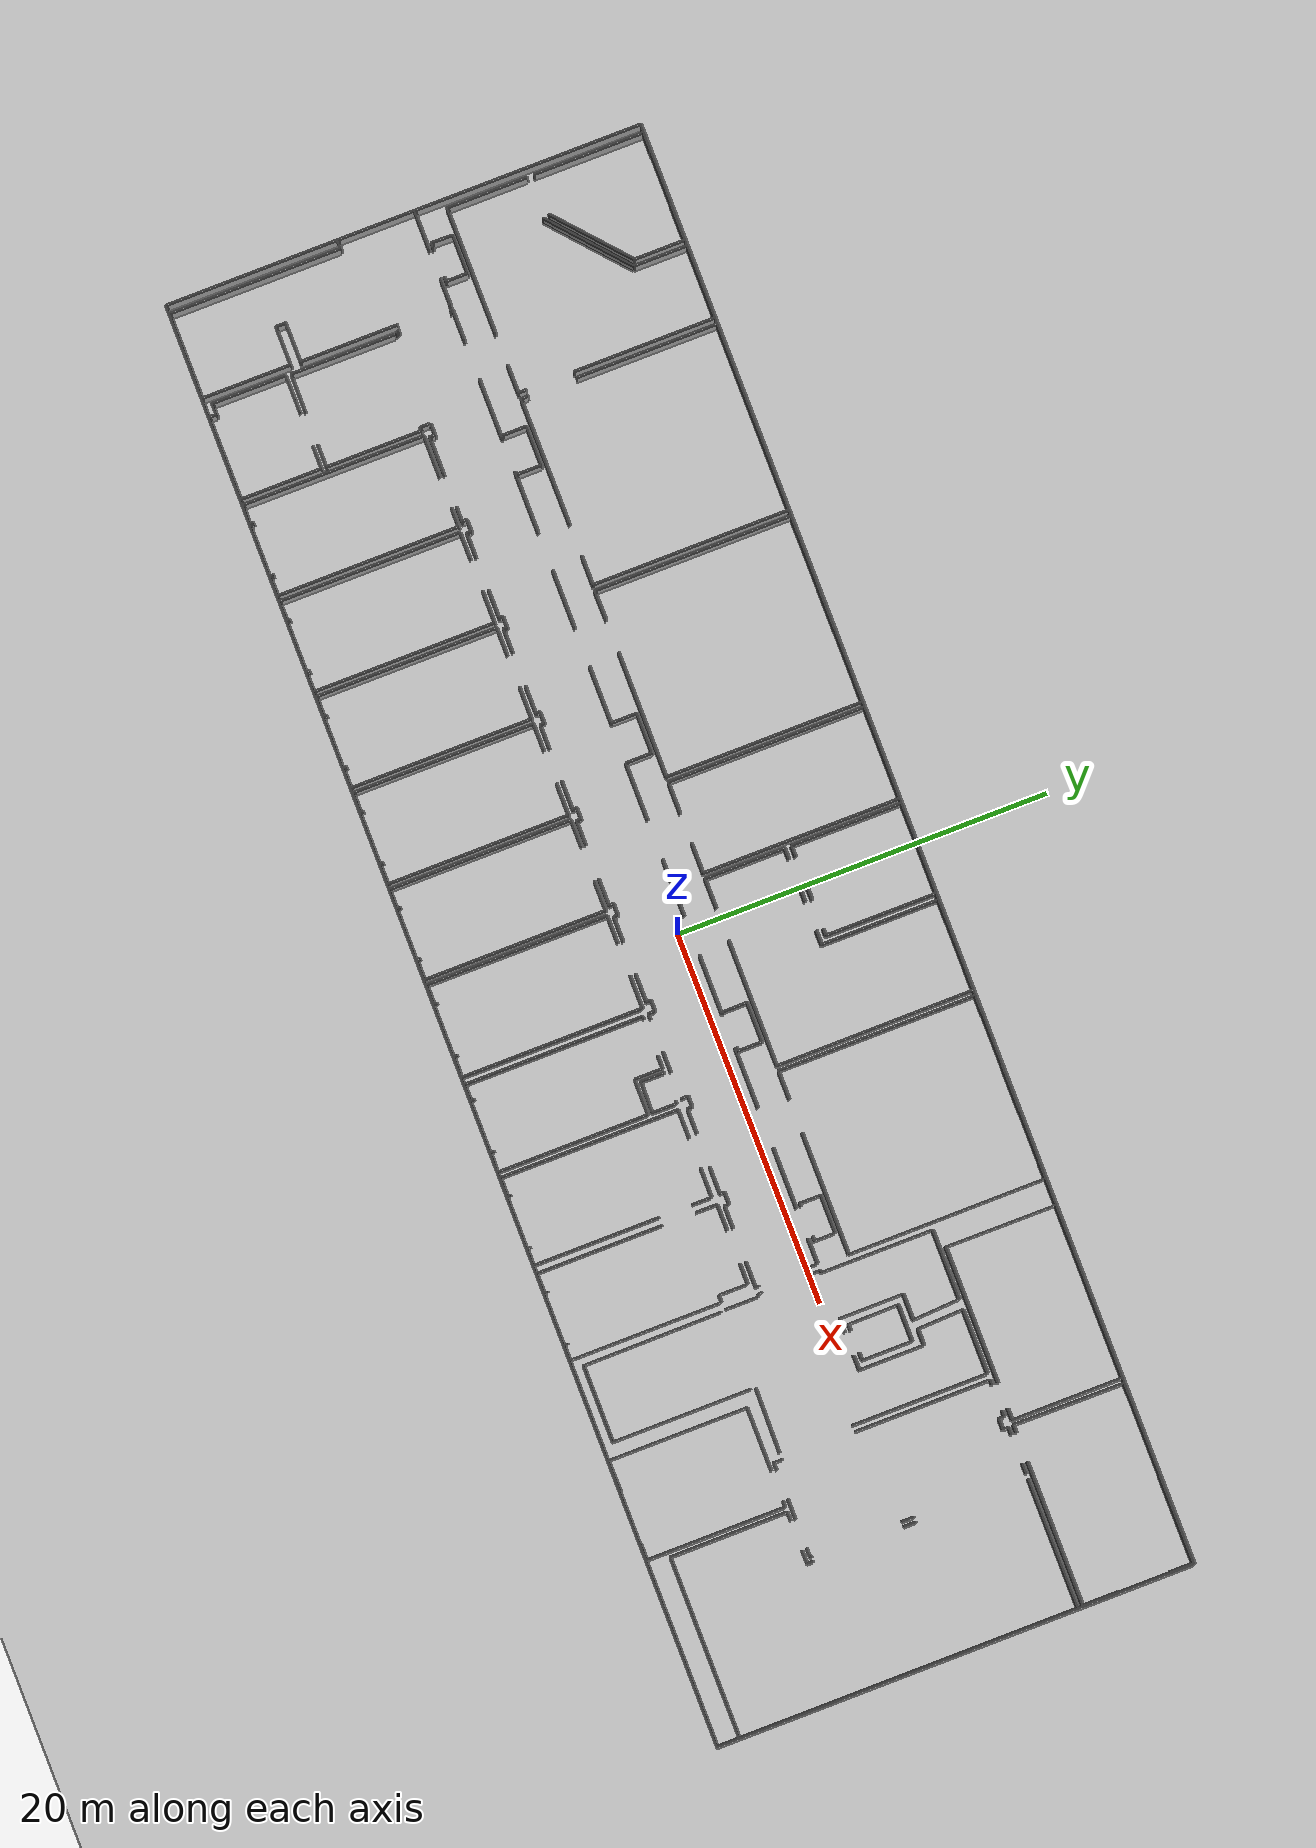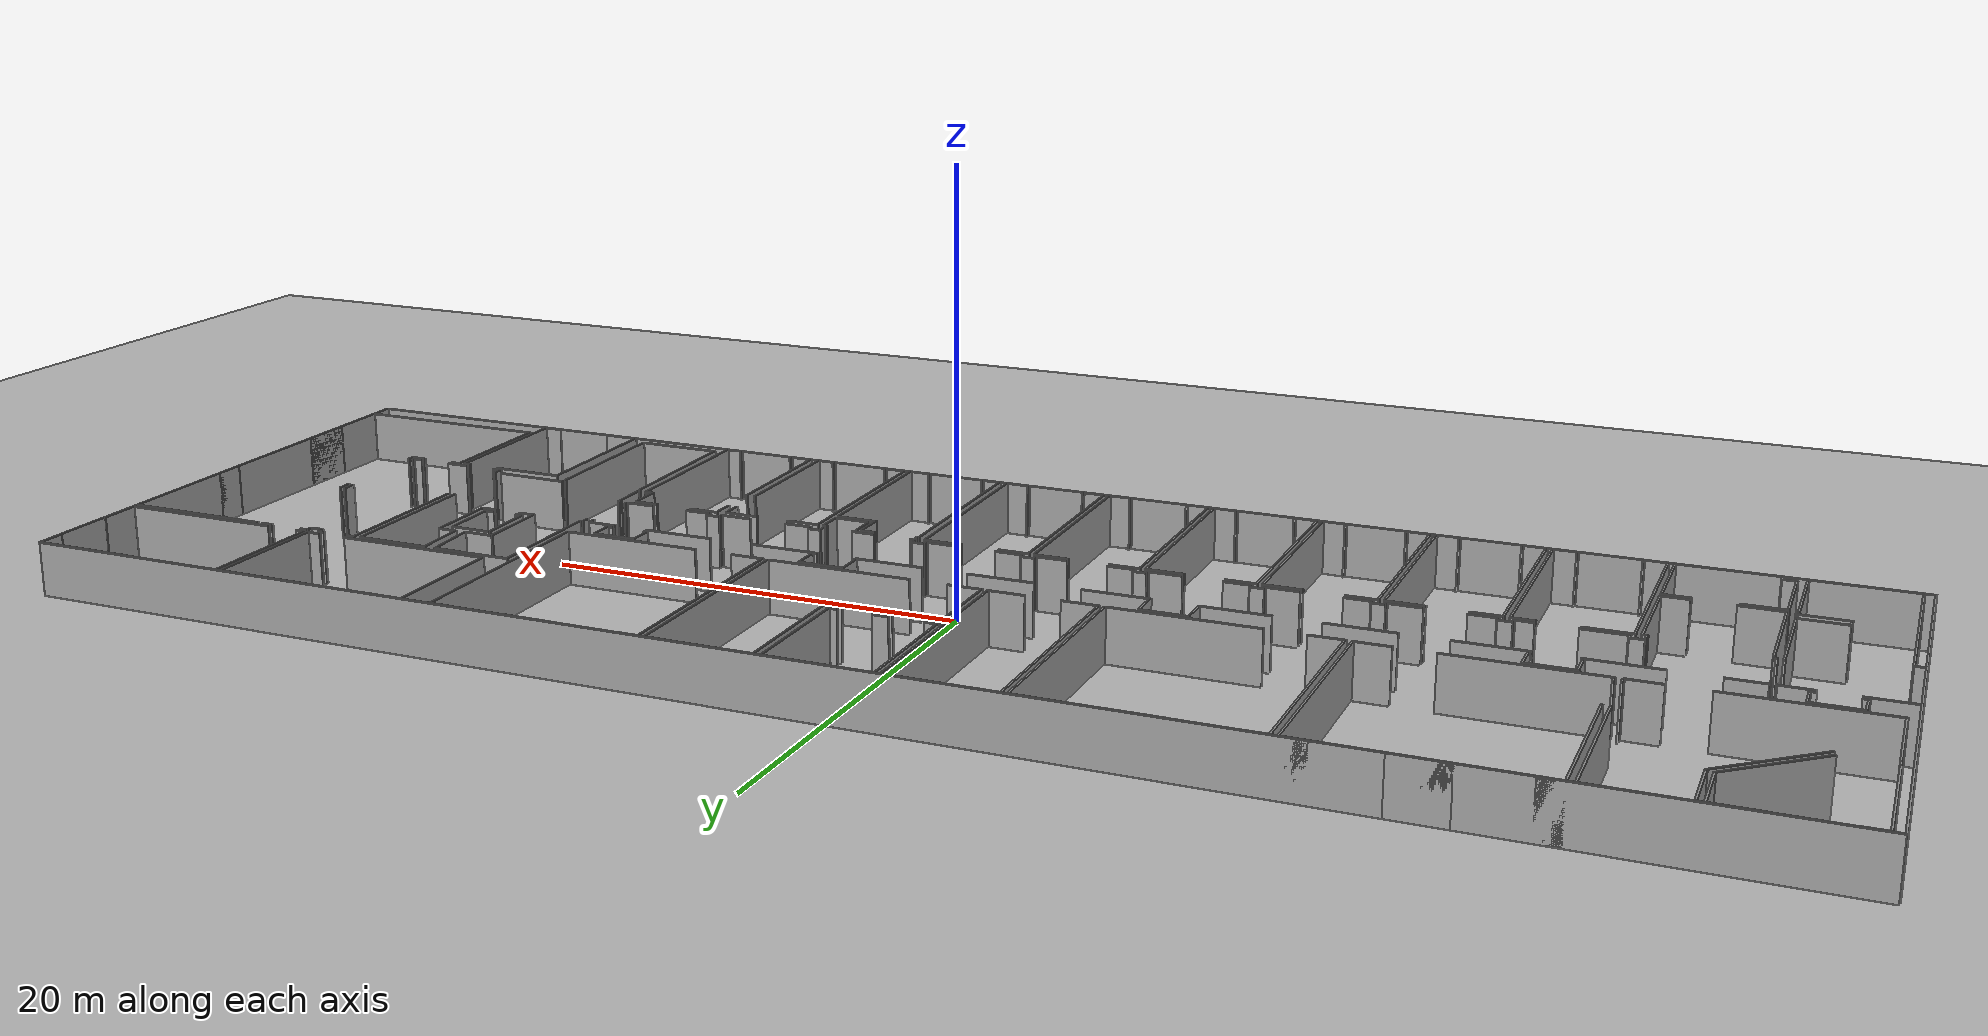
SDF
<sdf version="1.6">
  <world name="default">
    <light name="sun" type="directional">
      <cast_shadows>1</cast_shadows>
      <pose frame="">0 0 10 0 -0 0</pose>
      <diffuse>0.8 0.8 0.8 1</diffuse>
      <specular>0.1 0.1 0.1 1</specular>
      <attenuation>
        <range>1000</range>
        <constant>0.9</constant>
        <linear>0.01</linear>
        <quadratic>0.001</quadratic>
      </attenuation>
      <direction>-0.5 0.5 -1</direction>
    </light>
    <model name="ground_plane">
      <static>1</static>
      <link name="link">
        <collision name="collision">
          <geometry>
            <plane>
              <normal>0 0 1</normal>
              <size>100 100</size>
            </plane>
          </geometry>
          <surface>
            <friction>
              <ode>
                <mu>100</mu>
                <mu2>50</mu2>
              </ode>
              <torsional>
                <ode />
              </torsional>
            </friction>
            <contact>
              <ode />
            </contact>
            <bounce />
          </surface>
          <max_contacts>10</max_contacts>
        </collision>
        <visual name="visual">
          <cast_shadows>0</cast_shadows>
          <geometry>
            <plane>
              <normal>0 0 1</normal>
              <size>100 100</size>
            </plane>
          </geometry>
          <material>
            <script>
              <uri>file://media/materials/scripts/gazebo.material</uri>
              <name>Gazebo/Grey</name>
            </script>
          </material>
        </visual>
        <self_collide>0</self_collide>
        <kinematic>0</kinematic>
        <gravity>1</gravity>
      </link>
    </model>
    <gravity>0 0 -9.8</gravity>
    <magnetic_field>6e-06 2.3e-05 -4.2e-05</magnetic_field>
    <atmosphere type="adiabatic" />
    <physics default="0" name="default_physics" type="ode">
      <max_step_size>0.001</max_step_size>
      <real_time_factor>1</real_time_factor>
      <real_time_update_rate>1000</real_time_update_rate>
    </physics>
    <scene>
      <ambient>0.4 0.4 0.4 1</ambient>
      <background>0.7 0.7 0.7 1</background>
      <shadows>1</shadows>
    </scene>
    <spherical_coordinates>
      <surface_model>EARTH_WGS84</surface_model>
      <latitude_deg>0</latitude_deg>
      <longitude_deg>0</longitude_deg>
      <elevation>0</elevation>
      <heading_deg>0</heading_deg>
    </spherical_coordinates>
  <model name="0510030966_A-40">
		<static>1</static>
		<link name="Wall_0">
			<collision name="Wall_0_Collision">
				<geometry>
					<box>
						<size>5.95988975398 0.1 2.5</size>
					</box>
				</geometry>
				<pose frame="">2.97994487699 0 1.25 0 0 0</pose>
			</collision>
			<visual name="Wall_0_Visual">
				<pose frame="">2.97994487699 0 1.25 0 0 0</pose>
				<geometry>
					<box>
						<size>5.95988975398 0.1 2.5</size>
					</box>
				</geometry>
				<material>
					<script>
						<uri>file://media/materials/scripts/gazebo.material</uri>
						<name>Gazebo/Grey</name>
					</script>
					<ambient>1 1 1 1</ambient>
				</material>
			</visual>
			<pose frame="">0.443397304815 -5.98224378596 0 0 0 1.57079632679</pose>
		</link>
		<link name="Wall_1">
			<collision name="Wall_1_Collision">
				<geometry>
					<box>
						<size>1.03069869051 0.1 2.5</size>
					</box>
				</geometry>
				<pose frame="">0.515349345255 0 1.25 0 0 0</pose>
			</collision>
			<visual name="Wall_1_Visual">
				<pose frame="">0.515349345255 0 1.25 0 0 0</pose>
				<geometry>
					<box>
						<size>1.03069869051 0.1 2.5</size>
					</box>
				</geometry>
				<material>
					<script>
						<uri>file://media/materials/scripts/gazebo.material</uri>
						<name>Gazebo/Grey</name>
					</script>
					<ambient>1 1 1 1</ambient>
				</material>
			</visual>
			<pose frame="">0.443397304815 -0.0223540319815 0 0 0 0.0</pose>
		</link>
		<link name="Wall_2">
			<collision name="Wall_2_Collision">
				<geometry>
					<box>
						<size>2.0100847167 0.1 2.5</size>
					</box>
				</geometry>
				<pose frame="">1.00504235835 0 1.25 0 0 0</pose>
			</collision>
			<visual name="Wall_2_Visual">
				<pose frame="">1.00504235835 0 1.25 0 0 0</pose>
				<geometry>
					<box>
						<size>2.0100847167 0.1 2.5</size>
					</box>
				</geometry>
				<material>
					<script>
						<uri>file://media/materials/scripts/gazebo.material</uri>
						<name>Gazebo/Grey</name>
					</script>
					<ambient>1 1 1 1</ambient>
				</material>
			</visual>
			<pose frame="">4.28016206673 -0.0223540319815 0 0 0 0.0</pose>
		</link>
		<link name="Wall_3">
			<collision name="Wall_3_Collision">
				<geometry>
					<box>
						<size>2.73633673301 0.1 2.5</size>
					</box>
				</geometry>
				<pose frame="">1.3681683665 0 1.25 0 0 0</pose>
			</collision>
			<visual name="Wall_3_Visual">
				<pose frame="">1.3681683665 0 1.25 0 0 0</pose>
				<geometry>
					<box>
						<size>2.73633673301 0.1 2.5</size>
					</box>
				</geometry>
				<material>
					<script>
						<uri>file://media/materials/scripts/gazebo.material</uri>
						<name>Gazebo/Grey</name>
					</script>
					<ambient>1 1 1 1</ambient>
				</material>
			</visual>
			<pose frame="">6.29024678343 -0.0223540319815 0 0 0 -1.57079632679</pose>
		</link>
		<link name="Wall_4">
			<collision name="Wall_4_Collision">
				<geometry>
					<box>
						<size>4.91385763163 0.1 2.5</size>
					</box>
				</geometry>
				<pose frame="">2.45692881581 0 1.25 0 0 0</pose>
			</collision>
			<visual name="Wall_4_Visual">
				<pose frame="">2.45692881581 0 1.25 0 0 0</pose>
				<geometry>
					<box>
						<size>4.91385763163 0.1 2.5</size>
					</box>
				</geometry>
				<material>
					<script>
						<uri>file://media/materials/scripts/gazebo.material</uri>
						<name>Gazebo/Grey</name>
					</script>
					<ambient>1 1 1 1</ambient>
				</material>
			</visual>
			<pose frame="">6.29024678343 -2.75869076499 0 0 0 -2.42257056231</pose>
		</link>
		<link name="Wall_5">
			<collision name="Wall_5_Collision">
				<geometry>
					<box>
						<size>4.35547991312 0.1 2.5</size>
					</box>
				</geometry>
				<pose frame="">2.17773995656 0 1.25 0 0 0</pose>
			</collision>
			<visual name="Wall_5_Visual">
				<pose frame="">2.17773995656 0 1.25 0 0 0</pose>
				<geometry>
					<box>
						<size>4.35547991312 0.1 2.5</size>
					</box>
				</geometry>
				<material>
					<script>
						<uri>file://media/materials/scripts/gazebo.material</uri>
						<name>Gazebo/Grey</name>
					</script>
					<ambient>1 1 1 1</ambient>
				</material>
			</visual>
			<pose frame="">0.461051909619 -10.6772255598 0 0 0 1.57079632679</pose>
		</link>
		<link name="Wall_6">
			<collision name="Wall_6_Collision">
				<geometry>
					<box>
						<size>5.20379099327 0.1 2.5</size>
					</box>
				</geometry>
				<pose frame="">2.60189549664 0 1.25 0 0 0</pose>
			</collision>
			<visual name="Wall_6_Visual">
				<pose frame="">2.60189549664 0 1.25 0 0 0</pose>
				<geometry>
					<box>
						<size>5.20379099327 0.1 2.5</size>
					</box>
				</geometry>
				<material>
					<script>
						<uri>file://media/materials/scripts/gazebo.material</uri>
						<name>Gazebo/Grey</name>
					</script>
					<ambient>1 1 1 1</ambient>
				</material>
			</visual>
			<pose frame="">2.6696556717 -6.32174564668 0 0 0 0.716931152923</pose>
		</link>
		<link name="Wall_7">
			<collision name="Wall_7_Collision">
				<geometry>
					<box>
						<size>2.89726036097 0.1 2.5</size>
					</box>
				</geometry>
				<pose frame="">1.44863018048 0 1.25 0 0 0</pose>
			</collision>
			<visual name="Wall_7_Visual">
				<pose frame="">1.44863018048 0 1.25 0 0 0</pose>
				<geometry>
					<box>
						<size>2.89726036097 0.1 2.5</size>
					</box>
				</geometry>
				<material>
					<script>
						<uri>file://media/materials/scripts/gazebo.material</uri>
						<name>Gazebo/Grey</name>
					</script>
					<ambient>1 1 1 1</ambient>
				</material>
			</visual>
			<pose frame="">6.59240724982 -2.90246783433 0 0 0 1.57079632679</pose>
		</link>
		<link name="Wall_8">
			<collision name="Wall_8_Collision">
				<geometry>
					<box>
						<size>0.0797632504795 0.1 2.5</size>
					</box>
				</geometry>
				<pose frame="">0.0398816252397 0 1.25 0 0 0</pose>
			</collision>
			<visual name="Wall_8_Visual">
				<pose frame="">0.0398816252397 0 1.25 0 0 0</pose>
				<geometry>
					<box>
						<size>0.0797632504795 0.1 2.5</size>
					</box>
				</geometry>
				<material>
					<script>
						<uri>file://media/materials/scripts/gazebo.material</uri>
						<name>Gazebo/Grey</name>
					</script>
					<ambient>1 1 1 1</ambient>
				</material>
			</visual>
			<pose frame="">6.59240724982 -0.00520747335933 0 0 0 0.0</pose>
		</link>
		<link name="Wall_9">
			<collision name="Wall_9_Collision">
				<geometry>
					<box>
						<size>1.0609274383 0.1 2.5</size>
					</box>
				</geometry>
				<pose frame="">0.530463719152 0 1.25 0 0 0</pose>
			</collision>
			<visual name="Wall_9_Visual">
				<pose frame="">0.530463719152 0 1.25 0 0 0</pose>
				<geometry>
					<box>
						<size>1.0609274383 0.1 2.5</size>
					</box>
				</geometry>
				<material>
					<script>
						<uri>file://media/materials/scripts/gazebo.material</uri>
						<name>Gazebo/Grey</name>
					</script>
					<ambient>1 1 1 1</ambient>
				</material>
			</visual>
			<pose frame="">9.45702564363 -0.00520747335933 0 0 0 0.0</pose>
		</link>
		<link name="Wall_10">
			<collision name="Wall_10_Collision">
				<geometry>
					<box>
						<size>7.66108239239 0.1 2.5</size>
					</box>
				</geometry>
				<pose frame="">3.83054119619 0 1.25 0 0 0</pose>
			</collision>
			<visual name="Wall_10_Visual">
				<pose frame="">3.83054119619 0 1.25 0 0 0</pose>
				<geometry>
					<box>
						<size>7.66108239239 0.1 2.5</size>
					</box>
				</geometry>
				<material>
					<script>
						<uri>file://media/materials/scripts/gazebo.material</uri>
						<name>Gazebo/Grey</name>
					</script>
					<ambient>1 1 1 1</ambient>
				</material>
			</visual>
			<pose frame="">10.5179530819 -0.00520747335933 0 0 0 -1.57079632679</pose>
		</link>
		<link name="Wall_11">
			<collision name="Wall_11_Collision">
				<geometry>
					<box>
						<size>0.422567411378 0.1 2.5</size>
					</box>
				</geometry>
				<pose frame="">0.211283705689 0 1.25 0 0 0</pose>
			</collision>
			<visual name="Wall_11_Visual">
				<pose frame="">0.211283705689 0 1.25 0 0 0</pose>
				<geometry>
					<box>
						<size>0.422567411378 0.1 2.5</size>
					</box>
				</geometry>
				<material>
					<script>
						<uri>file://media/materials/scripts/gazebo.material</uri>
						<name>Gazebo/Grey</name>
					</script>
					<ambient>1 1 1 1</ambient>
				</material>
			</visual>
			<pose frame="">10.5179530819 -10.2400518207 0 0 0 -1.57079632679</pose>
		</link>
		<link name="Wall_12">
			<collision name="Wall_12_Collision">
				<geometry>
					<box>
						<size>1.52896498292 0.1 2.5</size>
					</box>
				</geometry>
				<pose frame="">0.764482491458 0 1.25 0 0 0</pose>
			</collision>
			<visual name="Wall_12_Visual">
				<pose frame="">0.764482491458 0 1.25 0 0 0</pose>
				<geometry>
					<box>
						<size>1.52896498292 0.1 2.5</size>
					</box>
				</geometry>
				<material>
					<script>
						<uri>file://media/materials/scripts/gazebo.material</uri>
						<name>Gazebo/Grey</name>
					</script>
					<ambient>1 1 1 1</ambient>
				</material>
			</visual>
			<pose frame="">10.5179530819 -10.6626192321 0 0 0 3.14159265359</pose>
		</link>
		<link name="Wall_13">
			<collision name="Wall_13_Collision">
				<geometry>
					<box>
						<size>6.77735179941 0.1 2.5</size>
					</box>
				</geometry>
				<pose frame="">3.3886758997 0 1.25 0 0 0</pose>
			</collision>
			<visual name="Wall_13_Visual">
				<pose frame="">3.3886758997 0 1.25 0 0 0</pose>
				<geometry>
					<box>
						<size>6.77735179941 0.1 2.5</size>
					</box>
				</geometry>
				<material>
					<script>
						<uri>file://media/materials/scripts/gazebo.material</uri>
						<name>Gazebo/Grey</name>
					</script>
					<ambient>1 1 1 1</ambient>
				</material>
			</visual>
			<pose frame="">7.23838796947 -10.6626192321 0 0 0 -3.13943748451</pose>
		</link>
		<link name="Wall_14">
			<collision name="Wall_14_Collision">
				<geometry>
					<box>
						<size>0.24906964043 0.1 2.5</size>
					</box>
				</geometry>
				<pose frame="">0.124534820215 0 1.25 0 0 0</pose>
			</collision>
			<visual name="Wall_14_Visual">
				<pose frame="">0.124534820215 0 1.25 0 0 0</pose>
				<geometry>
					<box>
						<size>0.24906964043 0.1 2.5</size>
					</box>
				</geometry>
				<material>
					<script>
						<uri>file://media/materials/scripts/gazebo.material</uri>
						<name>Gazebo/Grey</name>
					</script>
					<ambient>1 1 1 1</ambient>
				</material>
			</visual>
			<pose frame="">1.82896625303 -12.057206 0 0 0 0.0</pose>
		</link>
		<link name="Wall_15">
			<collision name="Wall_15_Collision">
				<geometry>
					<box>
						<size>0.258849529422 0.1 2.5</size>
					</box>
				</geometry>
				<pose frame="">0.129424764711 0 1.25 0 0 0</pose>
			</collision>
			<visual name="Wall_15_Visual">
				<pose frame="">0.129424764711 0 1.25 0 0 0</pose>
				<geometry>
					<box>
						<size>0.258849529422 0.1 2.5</size>
					</box>
				</geometry>
				<material>
					<script>
						<uri>file://media/materials/scripts/gazebo.material</uri>
						<name>Gazebo/Grey</name>
					</script>
					<ambient>1 1 1 1</ambient>
				</material>
			</visual>
			<pose frame="">3.67050664905 -12.057206 0 0 0 0.0</pose>
		</link>
		<link name="Wall_16">
			<collision name="Wall_16_Collision">
				<geometry>
					<box>
						<size>1.17828610621 0.1 2.5</size>
					</box>
				</geometry>
				<pose frame="">0.589143053104 0 1.25 0 0 0</pose>
			</collision>
			<visual name="Wall_16_Visual">
				<pose frame="">0.589143053104 0 1.25 0 0 0</pose>
				<geometry>
					<box>
						<size>1.17828610621 0.1 2.5</size>
					</box>
				</geometry>
				<material>
					<script>
						<uri>file://media/materials/scripts/gazebo.material</uri>
						<name>Gazebo/Grey</name>
					</script>
					<ambient>1 1 1 1</ambient>
				</material>
			</visual>
			<pose frame="">3.92935617848 -12.057206 0 0 0 1.57079632679</pose>
		</link>
		<link name="Wall_17">
			<collision name="Wall_17_Collision">
				<geometry>
					<box>
						<size>2.07105025847 0.1 2.5</size>
					</box>
				</geometry>
				<pose frame="">1.03552512923 0 1.25 0 0 0</pose>
			</collision>
			<visual name="Wall_17_Visual">
				<pose frame="">1.03552512923 0 1.25 0 0 0</pose>
				<geometry>
					<box>
						<size>2.07105025847 0.1 2.5</size>
					</box>
				</geometry>
				<material>
					<script>
						<uri>file://media/materials/scripts/gazebo.material</uri>
						<name>Gazebo/Grey</name>
					</script>
					<ambient>1 1 1 1</ambient>
				</material>
			</visual>
			<pose frame="">3.92935617848 -10.8789198938 0 0 0 3.14159265359</pose>
		</link>
		<link name="Wall_18">
			<collision name="Wall_18_Collision">
				<geometry>
					<box>
						<size>1.17865133273 0.1 2.5</size>
					</box>
				</geometry>
				<pose frame="">0.589325666363 0 1.25 0 0 0</pose>
			</collision>
			<visual name="Wall_18_Visual">
				<pose frame="">0.589325666363 0 1.25 0 0 0</pose>
				<geometry>
					<box>
						<size>1.17865133273 0.1 2.5</size>
					</box>
				</geometry>
				<material>
					<script>
						<uri>file://media/materials/scripts/gazebo.material</uri>
						<name>Gazebo/Grey</name>
					</script>
					<ambient>1 1 1 1</ambient>
				</material>
			</visual>
			<pose frame="">1.85830592001 -10.8789198938 0 0 0 -1.59569147349</pose>
		</link>
		<link name="Wall_19">
			<collision name="Wall_19_Collision">
				<geometry>
					<box>
						<size>4.5965478262 0.1 2.5</size>
					</box>
				</geometry>
				<pose frame="">2.2982739131 0 1.25 0 0 0</pose>
			</collision>
			<visual name="Wall_19_Visual">
				<pose frame="">2.2982739131 0 1.25 0 0 0</pose>
				<geometry>
					<box>
						<size>4.5965478262 0.1 2.5</size>
					</box>
				</geometry>
				<material>
					<script>
						<uri>file://media/materials/scripts/gazebo.material</uri>
						<name>Gazebo/Grey</name>
					</script>
					<ambient>1 1 1 1</ambient>
				</material>
			</visual>
			<pose frame="">5.05759973582 -25.7020563169 0 0 0 3.14159265359</pose>
		</link>
		<link name="Wall_20">
			<collision name="Wall_20_Collision">
				<geometry>
					<box>
						<size>9.26295200234 0.1 2.5</size>
					</box>
				</geometry>
				<pose frame="">4.63147600117 0 1.25 0 0 0</pose>
			</collision>
			<visual name="Wall_20_Visual">
				<pose frame="">4.63147600117 0 1.25 0 0 0</pose>
				<geometry>
					<box>
						<size>9.26295200234 0.1 2.5</size>
					</box>
				</geometry>
				<material>
					<script>
						<uri>file://media/materials/scripts/gazebo.material</uri>
						<name>Gazebo/Grey</name>
					</script>
					<ambient>1 1 1 1</ambient>
				</material>
			</visual>
			<pose frame="">0.461051909619 -25.7020563169 0 0 0 1.57079632679</pose>
		</link>
		<link name="Wall_21">
			<collision name="Wall_21_Collision">
				<geometry>
					<box>
						<size>0.461051909619 0.1 2.5</size>
					</box>
				</geometry>
				<pose frame="">0.230525954809 0 1.25 0 0 0</pose>
			</collision>
			<visual name="Wall_21_Visual">
				<pose frame="">0.230525954809 0 1.25 0 0 0</pose>
				<geometry>
					<box>
						<size>0.461051909619 0.1 2.5</size>
					</box>
				</geometry>
				<material>
					<script>
						<uri>file://media/materials/scripts/gazebo.material</uri>
						<name>Gazebo/Grey</name>
					</script>
					<ambient>1 1 1 1</ambient>
				</material>
			</visual>
			<pose frame="">0.461051909619 -16.4391043146 0 0 0 3.14159265359</pose>
		</link>
		<link name="Wall_22">
			<collision name="Wall_22_Collision">
				<geometry>
					<box>
						<size>2.06254048493 0.1 2.5</size>
					</box>
				</geometry>
				<pose frame="">1.03127024247 0 1.25 0 0 0</pose>
			</collision>
			<visual name="Wall_22_Visual">
				<pose frame="">1.03127024247 0 1.25 0 0 0</pose>
				<geometry>
					<box>
						<size>2.06254048493 0.1 2.5</size>
					</box>
				</geometry>
				<material>
					<script>
						<uri>file://media/materials/scripts/gazebo.material</uri>
						<name>Gazebo/Grey</name>
					</script>
					<ambient>1 1 1 1</ambient>
				</material>
			</visual>
			<pose frame="">0.0 -12.2684261999 0 0 0 0.0</pose>
		</link>
		<link name="Wall_23">
			<collision name="Wall_23_Collision">
				<geometry>
					<box>
						<size>1.42075114628 0.1 2.5</size>
					</box>
				</geometry>
				<pose frame="">0.71037557314 0 1.25 0 0 0</pose>
			</collision>
			<visual name="Wall_23_Visual">
				<pose frame="">0.71037557314 0 1.25 0 0 0</pose>
				<geometry>
					<box>
						<size>1.42075114628 0.1 2.5</size>
					</box>
				</geometry>
				<material>
					<script>
						<uri>file://media/materials/scripts/gazebo.material</uri>
						<name>Gazebo/Grey</name>
					</script>
					<ambient>1 1 1 1</ambient>
				</material>
			</visual>
			<pose frame="">3.68536699986 -12.2684261999 0 0 0 0.0</pose>
		</link>
		<link name="Wall_24">
			<collision name="Wall_24_Collision">
				<geometry>
					<box>
						<size>0.0947506128307 0.1 2.5</size>
					</box>
				</geometry>
				<pose frame="">0.0473753064154 0 1.25 0 0 0</pose>
			</collision>
			<visual name="Wall_24_Visual">
				<pose frame="">0.0473753064154 0 1.25 0 0 0</pose>
				<geometry>
					<box>
						<size>0.0947506128307 0.1 2.5</size>
					</box>
				</geometry>
				<material>
					<script>
						<uri>file://media/materials/scripts/gazebo.material</uri>
						<name>Gazebo/Grey</name>
					</script>
					<ambient>1 1 1 1</ambient>
				</material>
			</visual>
			<pose frame="">5.10611814614 -12.2684261999 0 0 0 -1.57079632679</pose>
		</link>
		<link name="Wall_25">
			<collision name="Wall_25_Collision">
				<geometry>
					<box>
						<size>5.26170728919 0.1 2.5</size>
					</box>
				</geometry>
				<pose frame="">2.6308536446 0 1.25 0 0 0</pose>
			</collision>
			<visual name="Wall_25_Visual">
				<pose frame="">2.6308536446 0 1.25 0 0 0</pose>
				<geometry>
					<box>
						<size>5.26170728919 0.1 2.5</size>
					</box>
				</geometry>
				<material>
					<script>
						<uri>file://media/materials/scripts/gazebo.material</uri>
						<name>Gazebo/Grey</name>
					</script>
					<ambient>1 1 1 1</ambient>
				</material>
			</visual>
			<pose frame="">5.10611814614 -15.1297422936 0 0 0 -1.57079632679</pose>
		</link>
		<link name="Wall_26">
			<collision name="Wall_26_Collision">
				<geometry>
					<box>
						<size>2.10991579135 0.1 2.5</size>
					</box>
				</geometry>
				<pose frame="">1.05495789567 0 1.25 0 0 0</pose>
			</collision>
			<visual name="Wall_26_Visual">
				<pose frame="">1.05495789567 0 1.25 0 0 0</pose>
				<geometry>
					<box>
						<size>2.10991579135 0.1 2.5</size>
					</box>
				</geometry>
				<material>
					<script>
						<uri>file://media/materials/scripts/gazebo.material</uri>
						<name>Gazebo/Grey</name>
					</script>
					<ambient>1 1 1 1</ambient>
				</material>
			</visual>
			<pose frame="">5.10611814614 -20.3914495828 0 0 0 3.14159265359</pose>
		</link>
		<link name="Wall_27">
			<collision name="Wall_27_Collision">
				<geometry>
					<box>
						<size>0.528114005563 0.1 2.5</size>
					</box>
				</geometry>
				<pose frame="">0.264057002782 0 1.25 0 0 0</pose>
			</collision>
			<visual name="Wall_27_Visual">
				<pose frame="">0.264057002782 0 1.25 0 0 0</pose>
				<geometry>
					<box>
						<size>0.528114005563 0.1 2.5</size>
					</box>
				</geometry>
				<material>
					<script>
						<uri>file://media/materials/scripts/gazebo.material</uri>
						<name>Gazebo/Grey</name>
					</script>
					<ambient>1 1 1 1</ambient>
				</material>
			</visual>
			<pose frame="">2.99620235479 -20.3914495828 0 0 0 -1.57079632679</pose>
		</link>
		<link name="Wall_28">
			<collision name="Wall_28_Collision">
				<geometry>
					<box>
						<size>2.07435255865 0.1 2.5</size>
					</box>
				</geometry>
				<pose frame="">1.03717627932 0 1.25 0 0 0</pose>
			</collision>
			<visual name="Wall_28_Visual">
				<pose frame="">1.03717627932 0 1.25 0 0 0</pose>
				<geometry>
					<box>
						<size>2.07435255865 0.1 2.5</size>
					</box>
				</geometry>
				<material>
					<script>
						<uri>file://media/materials/scripts/gazebo.material</uri>
						<name>Gazebo/Grey</name>
					</script>
					<ambient>1 1 1 1</ambient>
				</material>
			</visual>
			<pose frame="">2.99620235479 -20.9195635883 0 0 0 0.0</pose>
		</link>
		<link name="Wall_29">
			<collision name="Wall_29_Collision">
				<geometry>
					<box>
						<size>4.78251027554 0.1 2.5</size>
					</box>
				</geometry>
				<pose frame="">2.39125513777 0 1.25 0 0 0</pose>
			</collision>
			<visual name="Wall_29_Visual">
				<pose frame="">2.39125513777 0 1.25 0 0 0</pose>
				<geometry>
					<box>
						<size>4.78251027554 0.1 2.5</size>
					</box>
				</geometry>
				<material>
					<script>
						<uri>file://media/materials/scripts/gazebo.material</uri>
						<name>Gazebo/Grey</name>
					</script>
					<ambient>1 1 1 1</ambient>
				</material>
			</visual>
			<pose frame="">5.07055491344 -20.9195635883 0 0 0 -1.57350519572</pose>
		</link>
		<link name="Wall_30">
			<collision name="Wall_30_Collision">
				<geometry>
					<box>
						<size>0.0884000355632 0.1 2.5</size>
					</box>
				</geometry>
				<pose frame="">0.0442000177816 0 1.25 0 0 0</pose>
			</collision>
			<visual name="Wall_30_Visual">
				<pose frame="">0.0442000177816 0 1.25 0 0 0</pose>
				<geometry>
					<box>
						<size>0.0884000355632 0.1 2.5</size>
					</box>
				</geometry>
				<material>
					<script>
						<uri>file://media/materials/scripts/gazebo.material</uri>
						<name>Gazebo/Grey</name>
					</script>
					<ambient>1 1 1 1</ambient>
				</material>
			</visual>
			<pose frame="">5.39659355035 -15.2363049801 0 0 0 1.57079632679</pose>
		</link>
		<link name="Wall_31">
			<collision name="Wall_31_Collision">
				<geometry>
					<box>
						<size>0.15457305069 0.1 2.5</size>
					</box>
				</geometry>
				<pose frame="">0.0772865253452 0 1.25 0 0 0</pose>
			</collision>
			<visual name="Wall_31_Visual">
				<pose frame="">0.0772865253452 0 1.25 0 0 0</pose>
				<geometry>
					<box>
						<size>0.15457305069 0.1 2.5</size>
					</box>
				</geometry>
				<material>
					<script>
						<uri>file://media/materials/scripts/gazebo.material</uri>
						<name>Gazebo/Grey</name>
					</script>
					<ambient>1 1 1 1</ambient>
				</material>
			</visual>
			<pose frame="">5.39659355035 -12.410044073 0 0 0 1.57079632679</pose>
		</link>
		<link name="Wall_32">
			<collision name="Wall_32_Collision">
				<geometry>
					<box>
						<size>1.64035410819 0.1 2.5</size>
					</box>
				</geometry>
				<pose frame="">0.820177054094 0 1.25 0 0 0</pose>
			</collision>
			<visual name="Wall_32_Visual">
				<pose frame="">0.820177054094 0 1.25 0 0 0</pose>
				<geometry>
					<box>
						<size>1.64035410819 0.1 2.5</size>
					</box>
				</geometry>
				<material>
					<script>
						<uri>file://media/materials/scripts/gazebo.material</uri>
						<name>Gazebo/Grey</name>
					</script>
					<ambient>1 1 1 1</ambient>
				</material>
			</visual>
			<pose frame="">5.39659355035 -12.2554710223 0 0 0 0.0</pose>
		</link>
		<link name="Wall_33">
			<collision name="Wall_33_Collision">
				<geometry>
					<box>
						<size>3.19802370035 0.1 2.5</size>
					</box>
				</geometry>
				<pose frame="">1.59901185018 0 1.25 0 0 0</pose>
			</collision>
			<visual name="Wall_33_Visual">
				<pose frame="">1.59901185018 0 1.25 0 0 0</pose>
				<geometry>
					<box>
						<size>3.19802370035 0.1 2.5</size>
					</box>
				</geometry>
				<material>
					<script>
						<uri>file://media/materials/scripts/gazebo.material</uri>
						<name>Gazebo/Grey</name>
					</script>
					<ambient>1 1 1 1</ambient>
				</material>
			</visual>
			<pose frame="">9.12438240636 -12.2554710223 0 0 0 0.0</pose>
		</link>
		<link name="Wall_34">
			<collision name="Wall_34_Collision">
				<geometry>
					<box>
						<size>3.2471771684 0.1 2.5</size>
					</box>
				</geometry>
				<pose frame="">1.6235885842 0 1.25 0 0 0</pose>
			</collision>
			<visual name="Wall_34_Visual">
				<pose frame="">1.6235885842 0 1.25 0 0 0</pose>
				<geometry>
					<box>
						<size>3.2471771684 0.1 2.5</size>
					</box>
				</geometry>
				<material>
					<script>
						<uri>file://media/materials/scripts/gazebo.material</uri>
						<name>Gazebo/Grey</name>
					</script>
					<ambient>1 1 1 1</ambient>
				</material>
			</visual>
			<pose frame="">14.1852844424 -12.2554710223 0 0 0 0.0</pose>
		</link>
		<link name="Wall_35">
			<collision name="Wall_35_Collision">
				<geometry>
					<box>
						<size>3.09247710617 0.1 2.5</size>
					</box>
				</geometry>
				<pose frame="">1.54623855308 0 1.25 0 0 0</pose>
			</collision>
			<visual name="Wall_35_Visual">
				<pose frame="">1.54623855308 0 1.25 0 0 0</pose>
				<geometry>
					<box>
						<size>3.09247710617 0.1 2.5</size>
					</box>
				</geometry>
				<material>
					<script>
						<uri>file://media/materials/scripts/gazebo.material</uri>
						<name>Gazebo/Grey</name>
					</script>
					<ambient>1 1 1 1</ambient>
				</material>
			</visual>
			<pose frame="">19.5244687742 -12.2554710223 0 0 0 0.0</pose>
		</link>
		<link name="Wall_36">
			<collision name="Wall_36_Collision">
				<geometry>
					<box>
						<size>3.08638055199 0.1 2.5</size>
					</box>
				</geometry>
				<pose frame="">1.543190276 0 1.25 0 0 0</pose>
			</collision>
			<visual name="Wall_36_Visual">
				<pose frame="">1.543190276 0 1.25 0 0 0</pose>
				<geometry>
					<box>
						<size>3.08638055199 0.1 2.5</size>
					</box>
				</geometry>
				<material>
					<script>
						<uri>file://media/materials/scripts/gazebo.material</uri>
						<name>Gazebo/Grey</name>
					</script>
					<ambient>1 1 1 1</ambient>
				</material>
			</visual>
			<pose frame="">24.7291478795 -12.2554710223 0 0 0 0.0</pose>
		</link>
		<link name="Wall_37">
			<collision name="Wall_37_Collision">
				<geometry>
					<box>
						<size>1.39217354858 0.1 2.5</size>
					</box>
				</geometry>
				<pose frame="">0.696086774288 0 1.25 0 0 0</pose>
			</collision>
			<visual name="Wall_37_Visual">
				<pose frame="">0.696086774288 0 1.25 0 0 0</pose>
				<geometry>
					<box>
						<size>1.39217354858 0.1 2.5</size>
					</box>
				</geometry>
				<material>
					<script>
						<uri>file://media/materials/scripts/gazebo.material</uri>
						<name>Gazebo/Grey</name>
					</script>
					<ambient>1 1 1 1</ambient>
				</material>
			</visual>
			<pose frame="">27.8155284315 -12.2554710223 0 0 0 1.57079632679</pose>
		</link>
		<link name="Wall_38">
			<collision name="Wall_38_Collision">
				<geometry>
					<box>
						<size>2.14649511641 0.1 2.5</size>
					</box>
				</geometry>
				<pose frame="">1.0732475582 0 1.25 0 0 0</pose>
			</collision>
			<visual name="Wall_38_Visual">
				<pose frame="">1.0732475582 0 1.25 0 0 0</pose>
				<geometry>
					<box>
						<size>2.14649511641 0.1 2.5</size>
					</box>
				</geometry>
				<material>
					<script>
						<uri>file://media/materials/scripts/gazebo.material</uri>
						<name>Gazebo/Grey</name>
					</script>
					<ambient>1 1 1 1</ambient>
				</material>
			</visual>
			<pose frame="">27.8155284315 -10.8632974737 0 0 0 0.0</pose>
		</link>
		<link name="Wall_39">
			<collision name="Wall_39_Collision">
				<geometry>
					<box>
						<size>1.43523046245 0.1 2.5</size>
					</box>
				</geometry>
				<pose frame="">0.717615231225 0 1.25 0 0 0</pose>
			</collision>
			<visual name="Wall_39_Visual">
				<pose frame="">0.717615231225 0 1.25 0 0 0</pose>
				<geometry>
					<box>
						<size>1.43523046245 0.1 2.5</size>
					</box>
				</geometry>
				<material>
					<script>
						<uri>file://media/materials/scripts/gazebo.material</uri>
						<name>Gazebo/Grey</name>
					</script>
					<ambient>1 1 1 1</ambient>
				</material>
			</visual>
			<pose frame="">29.9620235479 -10.8632974737 0 0 0 -1.57079632679</pose>
		</link>
		<link name="Wall_40">
			<collision name="Wall_40_Collision">
				<geometry>
					<box>
						<size>3.04827708839 0.1 2.5</size>
					</box>
				</geometry>
				<pose frame="">1.52413854419 0 1.25 0 0 0</pose>
			</collision>
			<visual name="Wall_40_Visual">
				<pose frame="">1.52413854419 0 1.25 0 0 0</pose>
				<geometry>
					<box>
						<size>3.04827708839 0.1 2.5</size>
					</box>
				</geometry>
				<material>
					<script>
						<uri>file://media/materials/scripts/gazebo.material</uri>
						<name>Gazebo/Grey</name>
					</script>
					<ambient>1 1 1 1</ambient>
				</material>
			</visual>
			<pose frame="">29.9620235479 -12.2985279362 0 0 0 0.0</pose>
		</link>
		<link name="Wall_41">
			<collision name="Wall_41_Collision">
				<geometry>
					<box>
						<size>3.06491560083 0.1 2.5</size>
					</box>
				</geometry>
				<pose frame="">1.53245780041 0 1.25 0 0 0</pose>
			</collision>
			<visual name="Wall_41_Visual">
				<pose frame="">1.53245780041 0 1.25 0 0 0</pose>
				<geometry>
					<box>
						<size>3.06491560083 0.1 2.5</size>
					</box>
				</geometry>
				<material>
					<script>
						<uri>file://media/materials/scripts/gazebo.material</uri>
						<name>Gazebo/Grey</name>
					</script>
					<ambient>1 1 1 1</ambient>
				</material>
			</visual>
			<pose frame="">35.1628923069 -12.2985279362 0 0 0 0.0</pose>
		</link>
		<link name="Wall_42">
			<collision name="Wall_42_Collision">
				<geometry>
					<box>
						<size>3.18849783445 0.1 2.5</size>
					</box>
				</geometry>
				<pose frame="">1.59424891723 0 1.25 0 0 0</pose>
			</collision>
			<visual name="Wall_42_Visual">
				<pose frame="">1.59424891723 0 1.25 0 0 0</pose>
				<geometry>
					<box>
						<size>3.18849783445 0.1 2.5</size>
					</box>
				</geometry>
				<material>
					<script>
						<uri>file://media/materials/scripts/gazebo.material</uri>
						<name>Gazebo/Grey</name>
					</script>
					<ambient>1 1 1 1</ambient>
				</material>
			</visual>
			<pose frame="">40.336072549 -12.2985279362 0 0 0 0.0</pose>
		</link>
		<link name="Wall_43">
			<collision name="Wall_43_Collision">
				<geometry>
					<box>
						<size>3.23396796769 0.1 2.5</size>
					</box>
				</geometry>
				<pose frame="">1.61698398384 0 1.25 0 0 0</pose>
			</collision>
			<visual name="Wall_43_Visual">
				<pose frame="">1.61698398384 0 1.25 0 0 0</pose>
				<geometry>
					<box>
						<size>3.23396796769 0.1 2.5</size>
					</box>
				</geometry>
				<material>
					<script>
						<uri>file://media/materials/scripts/gazebo.material</uri>
						<name>Gazebo/Grey</name>
					</script>
					<ambient>1 1 1 1</ambient>
				</material>
			</visual>
			<pose frame="">45.3710642297 -12.2985279362 0 0 0 0.0</pose>
		</link>
		<link name="Wall_44">
			<collision name="Wall_44_Collision">
				<geometry>
					<box>
						<size>3.28197833183 0.1 2.5</size>
					</box>
				</geometry>
				<pose frame="">1.64098916592 0 1.25 0 0 0</pose>
			</collision>
			<visual name="Wall_44_Visual">
				<pose frame="">1.64098916592 0 1.25 0 0 0</pose>
				<geometry>
					<box>
						<size>3.28197833183 0.1 2.5</size>
					</box>
				</geometry>
				<material>
					<script>
						<uri>file://media/materials/scripts/gazebo.material</uri>
						<name>Gazebo/Grey</name>
					</script>
					<ambient>1 1 1 1</ambient>
				</material>
			</visual>
			<pose frame="">50.7630853645 -12.2985279362 0 0 0 0.0</pose>
		</link>
		<link name="Wall_45">
			<collision name="Wall_45_Collision">
				<geometry>
					<box>
						<size>1.38290170577 0.1 2.5</size>
					</box>
				</geometry>
				<pose frame="">0.691450852883 0 1.25 0 0 0</pose>
			</collision>
			<visual name="Wall_45_Visual">
				<pose frame="">0.691450852883 0 1.25 0 0 0</pose>
				<geometry>
					<box>
						<size>1.38290170577 0.1 2.5</size>
					</box>
				</geometry>
				<material>
					<script>
						<uri>file://media/materials/scripts/gazebo.material</uri>
						<name>Gazebo/Grey</name>
					</script>
					<ambient>1 1 1 1</ambient>
				</material>
			</visual>
			<pose frame="">55.64477411 -12.2985279362 0 0 0 0.0</pose>
		</link>
		<link name="Wall_46">
			<collision name="Wall_46_Collision">
				<geometry>
					<box>
						<size>0.361728881155 0.1 2.5</size>
					</box>
				</geometry>
				<pose frame="">0.180864440578 0 1.25 0 0 0</pose>
			</collision>
			<visual name="Wall_46_Visual">
				<pose frame="">0.180864440578 0 1.25 0 0 0</pose>
				<geometry>
					<box>
						<size>0.361728881155 0.1 2.5</size>
					</box>
				</geometry>
				<material>
					<script>
						<uri>file://media/materials/scripts/gazebo.material</uri>
						<name>Gazebo/Grey</name>
					</script>
					<ambient>1 1 1 1</ambient>
				</material>
			</visual>
			<pose frame="">57.0276758157 -12.2985279362 0 0 0 -1.57079632679</pose>
		</link>
		<link name="Wall_47">
			<collision name="Wall_47_Collision">
				<geometry>
					<box>
						<size>0.209950084463 0.1 2.5</size>
					</box>
				</geometry>
				<pose frame="">0.104975042231 0 1.25 0 0 0</pose>
			</collision>
			<visual name="Wall_47_Visual">
				<pose frame="">0.104975042231 0 1.25 0 0 0</pose>
				<geometry>
					<box>
						<size>0.209950084463 0.1 2.5</size>
					</box>
				</geometry>
				<material>
					<script>
						<uri>file://media/materials/scripts/gazebo.material</uri>
						<name>Gazebo/Grey</name>
					</script>
					<ambient>1 1 1 1</ambient>
				</material>
			</visual>
			<pose frame="">57.0276758157 -15.4362211525 0 0 0 -1.57079632679</pose>
		</link>
		<link name="Wall_48">
			<collision name="Wall_48_Collision">
				<geometry>
					<box>
						<size>1.40601780702 0.1 2.5</size>
					</box>
				</geometry>
				<pose frame="">0.703008903509 0 1.25 0 0 0</pose>
			</collision>
			<visual name="Wall_48_Visual">
				<pose frame="">0.703008903509 0 1.25 0 0 0</pose>
				<geometry>
					<box>
						<size>1.40601780702 0.1 2.5</size>
					</box>
				</geometry>
				<material>
					<script>
						<uri>file://media/materials/scripts/gazebo.material</uri>
						<name>Gazebo/Grey</name>
					</script>
					<ambient>1 1 1 1</ambient>
				</material>
			</visual>
			<pose frame="">57.0276758157 -15.646171237 0 0 0 3.14159265359</pose>
		</link>
		<link name="Wall_49">
			<collision name="Wall_49_Collision">
				<geometry>
					<box>
						<size>1.24153785579 0.1 2.5</size>
					</box>
				</geometry>
				<pose frame="">0.620768927896 0 1.25 0 0 0</pose>
			</collision>
			<visual name="Wall_49_Visual">
				<pose frame="">0.620768927896 0 1.25 0 0 0</pose>
				<geometry>
					<box>
						<size>1.24153785579 0.1 2.5</size>
					</box>
				</geometry>
				<material>
					<script>
						<uri>file://media/materials/scripts/gazebo.material</uri>
						<name>Gazebo/Grey</name>
					</script>
					<ambient>1 1 1 1</ambient>
				</material>
			</visual>
			<pose frame="">53.8617860364 -15.646171237 0 0 0 3.14159265359</pose>
		</link>
		<link name="Wall_50">
			<collision name="Wall_50_Collision">
				<geometry>
					<box>
						<size>0.251101825156 0.1 2.5</size>
					</box>
				</geometry>
				<pose frame="">0.125550912578 0 1.25 0 0 0</pose>
			</collision>
			<visual name="Wall_50_Visual">
				<pose frame="">0.125550912578 0 1.25 0 0 0</pose>
				<geometry>
					<box>
						<size>0.251101825156 0.1 2.5</size>
					</box>
				</geometry>
				<material>
					<script>
						<uri>file://media/materials/scripts/gazebo.material</uri>
						<name>Gazebo/Grey</name>
					</script>
					<ambient>1 1 1 1</ambient>
				</material>
			</visual>
			<pose frame="">52.6202481806 -15.646171237 0 0 0 1.57079632679</pose>
		</link>
		<link name="Wall_51">
			<collision name="Wall_51_Collision">
				<geometry>
					<box>
						<size>0.642678419468 0.1 2.5</size>
					</box>
				</geometry>
				<pose frame="">0.321339209734 0 1.25 0 0 0</pose>
			</collision>
			<visual name="Wall_51_Visual">
				<pose frame="">0.321339209734 0 1.25 0 0 0</pose>
				<geometry>
					<box>
						<size>0.642678419468 0.1 2.5</size>
					</box>
				</geometry>
				<material>
					<script>
						<uri>file://media/materials/scripts/gazebo.material</uri>
						<name>Gazebo/Grey</name>
					</script>
					<ambient>1 1 1 1</ambient>
				</material>
			</visual>
			<pose frame="">52.6202481806 -15.3950694118 0 0 0 3.14159265359</pose>
		</link>
		<link name="Wall_52">
			<collision name="Wall_52_Collision">
				<geometry>
					<box>
						<size>0.248307571158 0.1 2.5</size>
					</box>
				</geometry>
				<pose frame="">0.124153785579 0 1.25 0 0 0</pose>
			</collision>
			<visual name="Wall_52_Visual">
				<pose frame="">0.124153785579 0 1.25 0 0 0</pose>
				<geometry>
					<box>
						<size>0.248307571158 0.1 2.5</size>
					</box>
				</geometry>
				<material>
					<script>
						<uri>file://media/materials/scripts/gazebo.material</uri>
						<name>Gazebo/Grey</name>
					</script>
					<ambient>1 1 1 1</ambient>
				</material>
			</visual>
			<pose frame="">51.9775697611 -15.3950694118 0 0 0 -1.57079632679</pose>
		</link>
		<link name="Wall_53">
			<collision name="Wall_53_Collision">
				<geometry>
					<box>
						<size>1.47777933014 0.1 2.5</size>
					</box>
				</geometry>
				<pose frame="">0.738889665071 0 1.25 0 0 0</pose>
			</collision>
			<visual name="Wall_53_Visual">
				<pose frame="">0.738889665071 0 1.25 0 0 0</pose>
				<geometry>
					<box>
						<size>1.47777933014 0.1 2.5</size>
					</box>
				</geometry>
				<material>
					<script>
						<uri>file://media/materials/scripts/gazebo.material</uri>
						<name>Gazebo/Grey</name>
					</script>
					<ambient>1 1 1 1</ambient>
				</material>
			</visual>
			<pose frame="">51.9775697611 -15.643376983 0 0 0 3.14159265359</pose>
		</link>
		<link name="Wall_54">
			<collision name="Wall_54_Collision">
				<geometry>
					<box>
						<size>1.33362122617 0.1 2.5</size>
					</box>
				</geometry>
				<pose frame="">0.666810613085 0 1.25 0 0 0</pose>
			</collision>
			<visual name="Wall_54_Visual">
				<pose frame="">0.666810613085 0 1.25 0 0 0</pose>
				<geometry>
					<box>
						<size>1.33362122617 0.1 2.5</size>
					</box>
				</geometry>
				<material>
					<script>
						<uri>file://media/materials/scripts/gazebo.material</uri>
						<name>Gazebo/Grey</name>
					</script>
					<ambient>1 1 1 1</ambient>
				</material>
			</visual>
			<pose frame="">48.7089276415 -15.643376983 0 0 0 3.14159265359</pose>
		</link>
		<link name="Wall_55">
			<collision name="Wall_55_Collision">
				<geometry>
					<box>
						<size>0.271169649321 0.1 2.5</size>
					</box>
				</geometry>
				<pose frame="">0.135584824661 0 1.25 0 0 0</pose>
			</collision>
			<visual name="Wall_55_Visual">
				<pose frame="">0.135584824661 0 1.25 0 0 0</pose>
				<geometry>
					<box>
						<size>0.271169649321 0.1 2.5</size>
					</box>
				</geometry>
				<material>
					<script>
						<uri>file://media/materials/scripts/gazebo.material</uri>
						<name>Gazebo/Grey</name>
					</script>
					<ambient>1 1 1 1</ambient>
				</material>
			</visual>
			<pose frame="">47.3753064154 -15.643376983 0 0 0 1.57079632679</pose>
		</link>
		<link name="Wall_56">
			<collision name="Wall_56_Collision">
				<geometry>
					<box>
						<size>0.584253108608 0.1 2.5</size>
					</box>
				</geometry>
				<pose frame="">0.292126554304 0 1.25 0 0 0</pose>
			</collision>
			<visual name="Wall_56_Visual">
				<pose frame="">0.292126554304 0 1.25 0 0 0</pose>
				<geometry>
					<box>
						<size>0.584253108608 0.1 2.5</size>
					</box>
				</geometry>
				<material>
					<script>
						<uri>file://media/materials/scripts/gazebo.material</uri>
						<name>Gazebo/Grey</name>
					</script>
					<ambient>1 1 1 1</ambient>
				</material>
			</visual>
			<pose frame="">47.3753064154 -15.3722073336 0 0 0 3.14159265359</pose>
		</link>
		<link name="Wall_57">
			<collision name="Wall_57_Collision">
				<geometry>
					<box>
						<size>0.390052455768 0.1 2.5</size>
					</box>
				</geometry>
				<pose frame="">0.195026227884 0 1.25 0 0 0</pose>
			</collision>
			<visual name="Wall_57_Visual">
				<pose frame="">0.195026227884 0 1.25 0 0 0</pose>
				<geometry>
					<box>
						<size>0.390052455768 0.1 2.5</size>
					</box>
				</geometry>
				<material>
					<script>
						<uri>file://media/materials/scripts/gazebo.material</uri>
						<name>Gazebo/Grey</name>
					</script>
					<ambient>1 1 1 1</ambient>
				</material>
			</visual>
			<pose frame="">46.7910533067 -15.3722073336 0 0 0 -1.57079632679</pose>
		</link>
		<link name="Wall_58">
			<collision name="Wall_58_Collision">
				<geometry>
					<box>
						<size>1.11401826426 0.1 2.5</size>
					</box>
				</geometry>
				<pose frame="">0.55700913213 0 1.25 0 0 0</pose>
			</collision>
			<visual name="Wall_58_Visual">
				<pose frame="">0.55700913213 0 1.25 0 0 0</pose>
				<geometry>
					<box>
						<size>1.11401826426 0.1 2.5</size>
					</box>
				</geometry>
				<material>
					<script>
						<uri>file://media/materials/scripts/gazebo.material</uri>
						<name>Gazebo/Grey</name>
					</script>
					<ambient>1 1 1 1</ambient>
				</material>
			</visual>
			<pose frame="">45.3685239988 -15.7622597894 0 0 0 3.14159265359</pose>
		</link>
		<link name="Wall_59">
			<collision name="Wall_59_Collision">
				<geometry>
					<box>
						<size>0.298223108481 0.1 2.5</size>
					</box>
				</geometry>
				<pose frame="">0.14911155424 0 1.25 0 0 0</pose>
			</collision>
			<visual name="Wall_59_Visual">
				<pose frame="">0.14911155424 0 1.25 0 0 0</pose>
				<geometry>
					<box>
						<size>0.298223108481 0.1 2.5</size>
					</box>
				</geometry>
				<material>
					<script>
						<uri>file://media/materials/scripts/gazebo.material</uri>
						<name>Gazebo/Grey</name>
					</script>
					<ambient>1 1 1 1</ambient>
				</material>
			</visual>
			<pose frame="">42.4898073235 -15.7622597894 0 0 0 3.14159265359</pose>
		</link>
		<link name="Wall_60">
			<collision name="Wall_60_Collision">
				<geometry>
					<box>
						<size>0.370111643148 0.1 2.5</size>
					</box>
				</geometry>
				<pose frame="">0.185055821574 0 1.25 0 0 0</pose>
			</collision>
			<visual name="Wall_60_Visual">
				<pose frame="">0.185055821574 0 1.25 0 0 0</pose>
				<geometry>
					<box>
						<size>0.370111643148 0.1 2.5</size>
					</box>
				</geometry>
				<material>
					<script>
						<uri>file://media/materials/scripts/gazebo.material</uri>
						<name>Gazebo/Grey</name>
					</script>
					<ambient>1 1 1 1</ambient>
				</material>
			</visual>
			<pose frame="">42.191584215 -15.7622597894 0 0 0 1.57079632679</pose>
		</link>
		<link name="Wall_61">
			<collision name="Wall_61_Collision">
				<geometry>
					<box>
						<size>0.585396212516 0.1 2.5</size>
					</box>
				</geometry>
				<pose frame="">0.292698106258 0 1.25 0 0 0</pose>
			</collision>
			<visual name="Wall_61_Visual">
				<pose frame="">0.292698106258 0 1.25 0 0 0</pose>
				<geometry>
					<box>
						<size>0.585396212516 0.1 2.5</size>
					</box>
				</geometry>
				<material>
					<script>
						<uri>file://media/materials/scripts/gazebo.material</uri>
						<name>Gazebo/Grey</name>
					</script>
					<ambient>1 1 1 1</ambient>
				</material>
			</visual>
			<pose frame="">42.191584215 -15.3921481463 0 0 0 3.14159265359</pose>
		</link>
		<link name="Wall_62">
			<collision name="Wall_62_Collision">
				<geometry>
					<box>
						<size>0.254023090699 0.1 2.5</size>
					</box>
				</geometry>
				<pose frame="">0.127011545349 0 1.25 0 0 0</pose>
			</collision>
			<visual name="Wall_62_Visual">
				<pose frame="">0.127011545349 0 1.25 0 0 0</pose>
				<geometry>
					<box>
						<size>0.254023090699 0.1 2.5</size>
					</box>
				</geometry>
				<material>
					<script>
						<uri>file://media/materials/scripts/gazebo.material</uri>
						<name>Gazebo/Grey</name>
					</script>
					<ambient>1 1 1 1</ambient>
				</material>
			</visual>
			<pose frame="">41.6061880025 -15.3921481463 0 0 0 -1.57079632679</pose>
		</link>
		<link name="Wall_63">
			<collision name="Wall_63_Collision">
				<geometry>
					<box>
						<size>1.51308853975 0.1 2.5</size>
					</box>
				</geometry>
				<pose frame="">0.756544269874 0 1.25 0 0 0</pose>
			</collision>
			<visual name="Wall_63_Visual">
				<pose frame="">0.756544269874 0 1.25 0 0 0</pose>
				<geometry>
					<box>
						<size>1.51308853975 0.1 2.5</size>
					</box>
				</geometry>
				<material>
					<script>
						<uri>file://media/materials/scripts/gazebo.material</uri>
						<name>Gazebo/Grey</name>
					</script>
					<ambient>1 1 1 1</ambient>
				</material>
			</visual>
			<pose frame="">41.6061880025 -15.646171237 0 0 0 3.14159265359</pose>
		</link>
		<link name="Wall_64">
			<collision name="Wall_64_Collision">
				<geometry>
					<box>
						<size>1.32092007163 0.1 2.5</size>
					</box>
				</geometry>
				<pose frame="">0.660460035817 0 1.25 0 0 0</pose>
			</collision>
			<visual name="Wall_64_Visual">
				<pose frame="">0.660460035817 0 1.25 0 0 0</pose>
				<geometry>
					<box>
						<size>1.32092007163 0.1 2.5</size>
					</box>
				</geometry>
				<material>
					<script>
						<uri>file://media/materials/scripts/gazebo.material</uri>
						<name>Gazebo/Grey</name>
					</script>
					<ambient>1 1 1 1</ambient>
				</material>
			</visual>
			<pose frame="">38.3193832319 -15.646171237 0 0 0 3.14159265359</pose>
		</link>
		<link name="Wall_65">
			<collision name="Wall_65_Collision">
				<geometry>
					<box>
						<size>0.235860439714 0.1 2.5</size>
					</box>
				</geometry>
				<pose frame="">0.117930219857 0 1.25 0 0 0</pose>
			</collision>
			<visual name="Wall_65_Visual">
				<pose frame="">0.117930219857 0 1.25 0 0 0</pose>
				<geometry>
					<box>
						<size>0.235860439714 0.1 2.5</size>
					</box>
				</geometry>
				<material>
					<script>
						<uri>file://media/materials/scripts/gazebo.material</uri>
						<name>Gazebo/Grey</name>
					</script>
					<ambient>1 1 1 1</ambient>
				</material>
			</visual>
			<pose frame="">36.9984631603 -15.646171237 0 0 0 1.57079632679</pose>
		</link>
		<link name="Wall_66">
			<collision name="Wall_66_Collision">
				<geometry>
					<box>
						<size>0.622356572212 0.1 2.5</size>
					</box>
				</geometry>
				<pose frame="">0.311178286106 0 1.25 0 0 0</pose>
			</collision>
			<visual name="Wall_66_Visual">
				<pose frame="">0.311178286106 0 1.25 0 0 0</pose>
				<geometry>
					<box>
						<size>0.622356572212 0.1 2.5</size>
					</box>
				</geometry>
				<material>
					<script>
						<uri>file://media/materials/scripts/gazebo.material</uri>
						<name>Gazebo/Grey</name>
					</script>
					<ambient>1 1 1 1</ambient>
				</material>
			</visual>
			<pose frame="">36.9984631603 -15.4103107973 0 0 0 3.14159265359</pose>
		</link>
		<link name="Wall_67">
			<collision name="Wall_67_Collision">
				<geometry>
					<box>
						<size>0.254023090699 0.1 2.5</size>
					</box>
				</geometry>
				<pose frame="">0.127011545349 0 1.25 0 0 0</pose>
			</collision>
			<visual name="Wall_67_Visual">
				<pose frame="">0.127011545349 0 1.25 0 0 0</pose>
				<geometry>
					<box>
						<size>0.254023090699 0.1 2.5</size>
					</box>
				</geometry>
				<material>
					<script>
						<uri>file://media/materials/scripts/gazebo.material</uri>
						<name>Gazebo/Grey</name>
					</script>
					<ambient>1 1 1 1</ambient>
				</material>
			</visual>
			<pose frame="">36.3761065881 -15.4103107973 0 0 0 -1.57079632679</pose>
		</link>
		<link name="Wall_68">
			<collision name="Wall_68_Collision">
				<geometry>
					<box>
						<size>1.45809254061 0.1 2.5</size>
					</box>
				</geometry>
				<pose frame="">0.729046270306 0 1.25 0 0 0</pose>
			</collision>
			<visual name="Wall_68_Visual">
				<pose frame="">0.729046270306 0 1.25 0 0 0</pose>
				<geometry>
					<box>
						<size>1.45809254061 0.1 2.5</size>
					</box>
				</geometry>
				<material>
					<script>
						<uri>file://media/materials/scripts/gazebo.material</uri>
						<name>Gazebo/Grey</name>
					</script>
					<ambient>1 1 1 1</ambient>
				</material>
			</visual>
			<pose frame="">36.3761065881 -15.664333888 0 0 0 3.14159265359</pose>
		</link>
		<link name="Wall_69">
			<collision name="Wall_69_Collision">
				<geometry>
					<box>
						<size>1.25741429896 0.1 2.5</size>
					</box>
				</geometry>
				<pose frame="">0.62870714948 0 1.25 0 0 0</pose>
			</collision>
			<visual name="Wall_69_Visual">
				<pose frame="">0.62870714948 0 1.25 0 0 0</pose>
				<geometry>
					<box>
						<size>1.25741429896 0.1 2.5</size>
					</box>
				</geometry>
				<material>
					<script>
						<uri>file://media/materials/scripts/gazebo.material</uri>
						<name>Gazebo/Grey</name>
					</script>
					<ambient>1 1 1 1</ambient>
				</material>
			</visual>
			<pose frame="">33.0611052545 -15.664333888 0 0 0 3.14159265359</pose>
		</link>
		<link name="Wall_70">
			<collision name="Wall_70_Collision">
				<geometry>
					<box>
						<size>0.254023090699 0.1 2.5</size>
					</box>
				</geometry>
				<pose frame="">0.127011545349 0 1.25 0 0 0</pose>
			</collision>
			<visual name="Wall_70_Visual">
				<pose frame="">0.127011545349 0 1.25 0 0 0</pose>
				<geometry>
					<box>
						<size>0.254023090699 0.1 2.5</size>
					</box>
				</geometry>
				<material>
					<script>
						<uri>file://media/materials/scripts/gazebo.material</uri>
						<name>Gazebo/Grey</name>
					</script>
					<ambient>1 1 1 1</ambient>
				</material>
			</visual>
			<pose frame="">31.8036909555 -15.664333888 0 0 0 1.57079632679</pose>
		</link>
		<link name="Wall_71">
			<collision name="Wall_71_Collision">
				<geometry>
					<box>
						<size>0.609655417677 0.1 2.5</size>
					</box>
				</geometry>
				<pose frame="">0.304827708839 0 1.25 0 0 0</pose>
			</collision>
			<visual name="Wall_71_Visual">
				<pose frame="">0.304827708839 0 1.25 0 0 0</pose>
				<geometry>
					<box>
						<size>0.609655417677 0.1 2.5</size>
					</box>
				</geometry>
				<material>
					<script>
						<uri>file://media/materials/scripts/gazebo.material</uri>
						<name>Gazebo/Grey</name>
					</script>
					<ambient>1 1 1 1</ambient>
				</material>
			</visual>
			<pose frame="">31.8036909555 -15.4103107973 0 0 0 3.14159265359</pose>
		</link>
		<link name="Wall_72">
			<collision name="Wall_72_Collision">
				<geometry>
					<box>
						<size>0.228620781629 0.1 2.5</size>
					</box>
				</geometry>
				<pose frame="">0.114310390815 0 1.25 0 0 0</pose>
			</collision>
			<visual name="Wall_72_Visual">
				<pose frame="">0.114310390815 0 1.25 0 0 0</pose>
				<geometry>
					<box>
						<size>0.228620781629 0.1 2.5</size>
					</box>
				</geometry>
				<material>
					<script>
						<uri>file://media/materials/scripts/gazebo.material</uri>
						<name>Gazebo/Grey</name>
					</script>
					<ambient>1 1 1 1</ambient>
				</material>
			</visual>
			<pose frame="">31.1940355378 -15.4103107973 0 0 0 -1.57079632679</pose>
		</link>
		<link name="Wall_73">
			<collision name="Wall_73_Collision">
				<geometry>
					<box>
						<size>1.54001498736 0.1 2.5</size>
					</box>
				</geometry>
				<pose frame="">0.770007493681 0 1.25 0 0 0</pose>
			</collision>
			<visual name="Wall_73_Visual">
				<pose frame="">0.770007493681 0 1.25 0 0 0</pose>
				<geometry>
					<box>
						<size>1.54001498736 0.1 2.5</size>
					</box>
				</geometry>
				<material>
					<script>
						<uri>file://media/materials/scripts/gazebo.material</uri>
						<name>Gazebo/Grey</name>
					</script>
					<ambient>1 1 1 1</ambient>
				</material>
			</visual>
			<pose frame="">31.1940355378 -15.6389315789 0 0 0 3.14159265359</pose>
		</link>
		<link name="Wall_74">
			<collision name="Wall_74_Collision">
				<geometry>
					<box>
						<size>1.2480154446 0.1 2.5</size>
					</box>
				</geometry>
				<pose frame="">0.624007722302 0 1.25 0 0 0</pose>
			</collision>
			<visual name="Wall_74_Visual">
				<pose frame="">0.624007722302 0 1.25 0 0 0</pose>
				<geometry>
					<box>
						<size>1.2480154446 0.1 2.5</size>
					</box>
				</geometry>
				<material>
					<script>
						<uri>file://media/materials/scripts/gazebo.material</uri>
						<name>Gazebo/Grey</name>
					</script>
					<ambient>1 1 1 1</ambient>
				</material>
			</visual>
			<pose frame="">27.8557910914 -15.6389315789 0 0 0 3.14159265359</pose>
		</link>
		<link name="Wall_75">
			<collision name="Wall_75_Collision">
				<geometry>
					<box>
						<size>0.224810435269 0.1 2.5</size>
					</box>
				</geometry>
				<pose frame="">0.112405217634 0 1.25 0 0 0</pose>
			</collision>
			<visual name="Wall_75_Visual">
				<pose frame="">0.112405217634 0 1.25 0 0 0</pose>
				<geometry>
					<box>
						<size>0.224810435269 0.1 2.5</size>
					</box>
				</geometry>
				<material>
					<script>
						<uri>file://media/materials/scripts/gazebo.material</uri>
						<name>Gazebo/Grey</name>
					</script>
					<ambient>1 1 1 1</ambient>
				</material>
			</visual>
			<pose frame="">26.6077756468 -15.6389315789 0 0 0 1.57079632679</pose>
		</link>
		<link name="Wall_76">
			<collision name="Wall_76_Collision">
				<geometry>
					<box>
						<size>0.618419214307 0.1 2.5</size>
					</box>
				</geometry>
				<pose frame="">0.309209607153 0 1.25 0 0 0</pose>
			</collision>
			<visual name="Wall_76_Visual">
				<pose frame="">0.309209607153 0 1.25 0 0 0</pose>
				<geometry>
					<box>
						<size>0.618419214307 0.1 2.5</size>
					</box>
				</geometry>
				<material>
					<script>
						<uri>file://media/materials/scripts/gazebo.material</uri>
						<name>Gazebo/Grey</name>
					</script>
					<ambient>1 1 1 1</ambient>
				</material>
			</visual>
			<pose frame="">26.6077756468 -15.4141211436 0 0 0 3.14159265359</pose>
		</link>
		<link name="Wall_77">
			<collision name="Wall_77_Collision">
				<geometry>
					<box>
						<size>0.221000088908 0.1 2.5</size>
					</box>
				</geometry>
				<pose frame="">0.110500044454 0 1.25 0 0 0</pose>
			</collision>
			<visual name="Wall_77_Visual">
				<pose frame="">0.110500044454 0 1.25 0 0 0</pose>
				<geometry>
					<box>
						<size>0.221000088908 0.1 2.5</size>
					</box>
				</geometry>
				<material>
					<script>
						<uri>file://media/materials/scripts/gazebo.material</uri>
						<name>Gazebo/Grey</name>
					</script>
					<ambient>1 1 1 1</ambient>
				</material>
			</visual>
			<pose frame="">25.9893564325 -15.4141211436 0 0 0 -1.57079632679</pose>
		</link>
		<link name="Wall_78">
			<collision name="Wall_78_Collision">
				<geometry>
					<box>
						<size>1.49924428131 0.1 2.5</size>
					</box>
				</geometry>
				<pose frame="">0.749622140653 0 1.25 0 0 0</pose>
			</collision>
			<visual name="Wall_78_Visual">
				<pose frame="">0.749622140653 0 1.25 0 0 0</pose>
				<geometry>
					<box>
						<size>1.49924428131 0.1 2.5</size>
					</box>
				</geometry>
				<material>
					<script>
						<uri>file://media/materials/scripts/gazebo.material</uri>
						<name>Gazebo/Grey</name>
					</script>
					<ambient>1 1 1 1</ambient>
				</material>
			</visual>
			<pose frame="">25.9893564325 -15.6351212325 0 0 0 3.14159265359</pose>
		</link>
		<link name="Wall_79">
			<collision name="Wall_79_Collision">
				<geometry>
					<box>
						<size>1.24293498279 0.1 2.5</size>
					</box>
				</geometry>
				<pose frame="">0.621467491395 0 1.25 0 0 0</pose>
			</collision>
			<visual name="Wall_79_Visual">
				<pose frame="">0.621467491395 0 1.25 0 0 0</pose>
				<geometry>
					<box>
						<size>1.24293498279 0.1 2.5</size>
					</box>
				</geometry>
				<material>
					<script>
						<uri>file://media/materials/scripts/gazebo.material</uri>
						<name>Gazebo/Grey</name>
					</script>
					<ambient>1 1 1 1</ambient>
				</material>
			</visual>
			<pose frame="">22.6443803742 -15.6351212325 0 0 0 3.14159265359</pose>
		</link>
		<link name="Wall_80">
			<collision name="Wall_80_Collision">
				<geometry>
					<box>
						<size>0.196232837565 0.1 2.5</size>
					</box>
				</geometry>
				<pose frame="">0.0981164187825 0 1.25 0 0 0</pose>
			</collision>
			<visual name="Wall_80_Visual">
				<pose frame="">0.0981164187825 0 1.25 0 0 0</pose>
				<geometry>
					<box>
						<size>0.196232837565 0.1 2.5</size>
					</box>
				</geometry>
				<material>
					<script>
						<uri>file://media/materials/scripts/gazebo.material</uri>
						<name>Gazebo/Grey</name>
					</script>
					<ambient>1 1 1 1</ambient>
				</material>
			</visual>
			<pose frame="">21.4014453914 -15.6351212325 0 0 0 1.57079632679</pose>
		</link>
		<link name="Wall_81">
			<collision name="Wall_81_Collision">
				<geometry>
					<box>
						<size>0.587936443423 0.1 2.5</size>
					</box>
				</geometry>
				<pose frame="">0.293968221711 0 1.25 0 0 0</pose>
			</collision>
			<visual name="Wall_81_Visual">
				<pose frame="">0.293968221711 0 1.25 0 0 0</pose>
				<geometry>
					<box>
						<size>0.587936443423 0.1 2.5</size>
					</box>
				</geometry>
				<material>
					<script>
						<uri>file://media/materials/scripts/gazebo.material</uri>
						<name>Gazebo/Grey</name>
					</script>
					<ambient>1 1 1 1</ambient>
				</material>
			</visual>
			<pose frame="">21.4014453914 -15.438888395 0 0 0 3.14159265359</pose>
		</link>
		<link name="Wall_82">
			<collision name="Wall_82_Collision">
				<geometry>
					<box>
						<size>0.20156732247 0.1 2.5</size>
					</box>
				</geometry>
				<pose frame="">0.100783661235 0 1.25 0 0 0</pose>
			</collision>
			<visual name="Wall_82_Visual">
				<pose frame="">0.100783661235 0 1.25 0 0 0</pose>
				<geometry>
					<box>
						<size>0.20156732247 0.1 2.5</size>
					</box>
				</geometry>
				<material>
					<script>
						<uri>file://media/materials/scripts/gazebo.material</uri>
						<name>Gazebo/Grey</name>
					</script>
					<ambient>1 1 1 1</ambient>
				</material>
			</visual>
			<pose frame="">20.813508948 -15.438888395 0 0 0 -1.57079632679</pose>
		</link>
		<link name="Wall_83">
			<collision name="Wall_83_Collision">
				<geometry>
					<box>
						<size>1.52820291364 0.1 2.5</size>
					</box>
				</geometry>
				<pose frame="">0.764101456822 0 1.25 0 0 0</pose>
			</collision>
			<visual name="Wall_83_Visual">
				<pose frame="">0.764101456822 0 1.25 0 0 0</pose>
				<geometry>
					<box>
						<size>1.52820291364 0.1 2.5</size>
					</box>
				</geometry>
				<material>
					<script>
						<uri>file://media/materials/scripts/gazebo.material</uri>
						<name>Gazebo/Grey</name>
					</script>
					<ambient>1 1 1 1</ambient>
				</material>
			</visual>
			<pose frame="">20.813508948 -15.6404557174 0 0 0 3.14159265359</pose>
		</link>
		<link name="Wall_84">
			<collision name="Wall_84_Collision">
				<geometry>
					<box>
						<size>1.25804935669 0.1 2.5</size>
					</box>
				</geometry>
				<pose frame="">0.629024678343 0 1.25 0 0 0</pose>
			</collision>
			<visual name="Wall_84_Visual">
				<pose frame="">0.629024678343 0 1.25 0 0 0</pose>
				<geometry>
					<box>
						<size>1.25804935669 0.1 2.5</size>
					</box>
				</geometry>
				<material>
					<script>
						<uri>file://media/materials/scripts/gazebo.material</uri>
						<name>Gazebo/Grey</name>
					</script>
					<ambient>1 1 1 1</ambient>
				</material>
			</visual>
			<pose frame="">17.4691679474 -15.6404557174 0 0 0 3.14159265359</pose>
		</link>
		<link name="Wall_85">
			<collision name="Wall_85_Collision">
				<geometry>
					<box>
						<size>0.252752975245 0.1 2.5</size>
					</box>
				</geometry>
				<pose frame="">0.126376487623 0 1.25 0 0 0</pose>
			</collision>
			<visual name="Wall_85_Visual">
				<pose frame="">0.126376487623 0 1.25 0 0 0</pose>
				<geometry>
					<box>
						<size>0.252752975245 0.1 2.5</size>
					</box>
				</geometry>
				<material>
					<script>
						<uri>file://media/materials/scripts/gazebo.material</uri>
						<name>Gazebo/Grey</name>
					</script>
					<ambient>1 1 1 1</ambient>
				</material>
			</visual>
			<pose frame="">16.2111185907 -15.6404557174 0 0 0 1.57079632679</pose>
		</link>
		<link name="Wall_86">
			<collision name="Wall_86_Collision">
				<geometry>
					<box>
						<size>0.624261745393 0.1 2.5</size>
					</box>
				</geometry>
				<pose frame="">0.312130872696 0 1.25 0 0 0</pose>
			</collision>
			<visual name="Wall_86_Visual">
				<pose frame="">0.312130872696 0 1.25 0 0 0</pose>
				<geometry>
					<box>
						<size>0.624261745393 0.1 2.5</size>
					</box>
				</geometry>
				<material>
					<script>
						<uri>file://media/materials/scripts/gazebo.material</uri>
						<name>Gazebo/Grey</name>
					</script>
					<ambient>1 1 1 1</ambient>
				</material>
			</visual>
			<pose frame="">16.2111185907 -15.3877027422 0 0 0 3.14159265359</pose>
		</link>
		<link name="Wall_87">
			<collision name="Wall_87_Collision">
				<geometry>
					<box>
						<size>0.26901045305 0.1 2.5</size>
					</box>
				</geometry>
				<pose frame="">0.134505226525 0 1.25 0 0 0</pose>
			</collision>
			<visual name="Wall_87_Visual">
				<pose frame="">0.134505226525 0 1.25 0 0 0</pose>
				<geometry>
					<box>
						<size>0.26901045305 0.1 2.5</size>
					</box>
				</geometry>
				<material>
					<script>
						<uri>file://media/materials/scripts/gazebo.material</uri>
						<name>Gazebo/Grey</name>
					</script>
					<ambient>1 1 1 1</ambient>
				</material>
			</visual>
			<pose frame="">15.5868568453 -15.3877027422 0 0 0 -1.57079632679</pose>
		</link>
		<link name="Wall_88">
			<collision name="Wall_88_Collision">
				<geometry>
					<box>
						<size>0.825956079408 0.1 2.5</size>
					</box>
				</geometry>
				<pose frame="">0.412978039704 0 1.25 0 0 0</pose>
			</collision>
			<visual name="Wall_88_Visual">
				<pose frame="">0.412978039704 0 1.25 0 0 0</pose>
				<geometry>
					<box>
						<size>0.825956079408 0.1 2.5</size>
					</box>
				</geometry>
				<material>
					<script>
						<uri>file://media/materials/scripts/gazebo.material</uri>
						<name>Gazebo/Grey</name>
					</script>
					<ambient>1 1 1 1</ambient>
				</material>
			</visual>
			<pose frame="">15.5868568453 -15.6567131952 0 0 0 3.14159265359</pose>
		</link>
		<link name="Wall_89">
			<collision name="Wall_89_Collision">
				<geometry>
					<box>
						<size>1.99408126199 0.1 2.5</size>
					</box>
				</geometry>
				<pose frame="">0.997040630993 0 1.25 0 0 0</pose>
			</collision>
			<visual name="Wall_89_Visual">
				<pose frame="">0.997040630993 0 1.25 0 0 0</pose>
				<geometry>
					<box>
						<size>1.99408126199 0.1 2.5</size>
					</box>
				</geometry>
				<material>
					<script>
						<uri>file://media/materials/scripts/gazebo.material</uri>
						<name>Gazebo/Grey</name>
					</script>
					<ambient>1 1 1 1</ambient>
				</material>
			</visual>
			<pose frame="">12.9932810893 -15.6567131952 0 0 0 3.14159265359</pose>
		</link>
		<link name="Wall_90">
			<collision name="Wall_90_Collision">
				<geometry>
					<box>
						<size>0.297207016118 0.1 2.5</size>
					</box>
				</geometry>
				<pose frame="">0.148603508059 0 1.25 0 0 0</pose>
			</collision>
			<visual name="Wall_90_Visual">
				<pose frame="">0.148603508059 0 1.25 0 0 0</pose>
				<geometry>
					<box>
						<size>0.297207016118 0.1 2.5</size>
					</box>
				</geometry>
				<material>
					<script>
						<uri>file://media/materials/scripts/gazebo.material</uri>
						<name>Gazebo/Grey</name>
					</script>
					<ambient>1 1 1 1</ambient>
				</material>
			</visual>
			<pose frame="">10.9991998273 -15.6567131952 0 0 0 1.57079632679</pose>
		</link>
		<link name="Wall_91">
			<collision name="Wall_91_Collision">
				<geometry>
					<box>
						<size>0.609655417677 0.1 2.5</size>
					</box>
				</geometry>
				<pose frame="">0.304827708839 0 1.25 0 0 0</pose>
			</collision>
			<visual name="Wall_91_Visual">
				<pose frame="">0.304827708839 0 1.25 0 0 0</pose>
				<geometry>
					<box>
						<size>0.609655417677 0.1 2.5</size>
					</box>
				</geometry>
				<material>
					<script>
						<uri>file://media/materials/scripts/gazebo.material</uri>
						<name>Gazebo/Grey</name>
					</script>
					<ambient>1 1 1 1</ambient>
				</material>
			</visual>
			<pose frame="">10.9991998273 -15.3595061791 0 0 0 3.14159265359</pose>
		</link>
		<link name="Wall_92">
			<collision name="Wall_92_Collision">
				<geometry>
					<box>
						<size>0.169104031957 0.1 2.5</size>
					</box>
				</geometry>
				<pose frame="">0.0845520159785 0 1.25 0 0 0</pose>
			</collision>
			<visual name="Wall_92_Visual">
				<pose frame="">0.0845520159785 0 1.25 0 0 0</pose>
				<geometry>
					<box>
						<size>0.169104031957 0.1 2.5</size>
					</box>
				</geometry>
				<material>
					<script>
						<uri>file://media/materials/scripts/gazebo.material</uri>
						<name>Gazebo/Grey</name>
					</script>
					<ambient>1 1 1 1</ambient>
				</material>
			</visual>
			<pose frame="">5.51242807971 -15.3595061791 0 0 0 2.32538596293</pose>
		</link>
		<link name="Wall_93">
			<collision name="Wall_93_Collision">
				<geometry>
					<box>
						<size>5.62343617035 0.1 2.5</size>
					</box>
				</geometry>
				<pose frame="">2.81171808517 0 1.25 0 0 0</pose>
			</collision>
			<visual name="Wall_93_Visual">
				<pose frame="">2.81171808517 0 1.25 0 0 0</pose>
				<geometry>
					<box>
						<size>5.62343617035 0.1 2.5</size>
					</box>
				</geometry>
				<material>
					<script>
						<uri>file://media/materials/scripts/gazebo.material</uri>
						<name>Gazebo/Grey</name>
					</script>
					<ambient>1 1 1 1</ambient>
				</material>
			</visual>
			<pose frame="">5.51484129907 -21.0623245653 0 0 0 1.57079632679</pose>
		</link>
		<link name="Wall_94">
			<collision name="Wall_94_Collision">
				<geometry>
					<box>
						<size>0.4943289345 0.1 2.5</size>
					</box>
				</geometry>
				<pose frame="">0.24716446725 0 1.25 0 0 0</pose>
			</collision>
			<visual name="Wall_94_Visual">
				<pose frame="">0.24716446725 0 1.25 0 0 0</pose>
				<geometry>
					<box>
						<size>0.4943289345 0.1 2.5</size>
					</box>
				</geometry>
				<material>
					<script>
						<uri>file://media/materials/scripts/gazebo.material</uri>
						<name>Gazebo/Grey</name>
					</script>
					<ambient>1 1 1 1</ambient>
				</material>
			</visual>
			<pose frame="">10.372397851 -15.438888395 0 0 0 -1.57079632679</pose>
		</link>
		<link name="Wall_95">
			<collision name="Wall_95_Collision">
				<geometry>
					<box>
						<size>0.187723064027 0.1 2.5</size>
					</box>
				</geometry>
				<pose frame="">0.0938615320133 0 1.25 0 0 0</pose>
			</collision>
			<visual name="Wall_95_Visual">
				<pose frame="">0.0938615320133 0 1.25 0 0 0</pose>
				<geometry>
					<box>
						<size>0.187723064027 0.1 2.5</size>
					</box>
				</geometry>
				<material>
					<script>
						<uri>file://media/materials/scripts/gazebo.material</uri>
						<name>Gazebo/Grey</name>
					</script>
					<ambient>1 1 1 1</ambient>
				</material>
			</visual>
			<pose frame="">10.372397851 -15.9332173295 0 0 0 0.0</pose>
		</link>
		<link name="Wall_96">
			<collision name="Wall_96_Collision">
				<geometry>
					<box>
						<size>5.14180839038 0.1 2.5</size>
					</box>
				</geometry>
				<pose frame="">2.57090419519 0 1.25 0 0 0</pose>
			</collision>
			<visual name="Wall_96_Visual">
				<pose frame="">2.57090419519 0 1.25 0 0 0</pose>
				<geometry>
					<box>
						<size>5.14180839038 0.1 2.5</size>
					</box>
				</geometry>
				<material>
					<script>
						<uri>file://media/materials/scripts/gazebo.material</uri>
						<name>Gazebo/Grey</name>
					</script>
					<ambient>1 1 1 1</ambient>
				</material>
			</visual>
			<pose frame="">10.560120915 -15.9332173295 0 0 0 -1.57079632679</pose>
		</link>
		<link name="Wall_97">
			<collision name="Wall_97_Collision">
				<geometry>
					<box>
						<size>1.2247723318 0.1 2.5</size>
					</box>
				</geometry>
				<pose frame="">0.612386165902 0 1.25 0 0 0</pose>
			</collision>
			<visual name="Wall_97_Visual">
				<pose frame="">0.612386165902 0 1.25 0 0 0</pose>
				<geometry>
					<box>
						<size>1.2247723318 0.1 2.5</size>
					</box>
				</geometry>
				<material>
					<script>
						<uri>file://media/materials/scripts/gazebo.material</uri>
						<name>Gazebo/Grey</name>
					</script>
					<ambient>1 1 1 1</ambient>
				</material>
			</visual>
			<pose frame="">10.560120915 -21.0750257198 0 0 0 3.14159265359</pose>
		</link>
		<link name="Wall_98">
			<collision name="Wall_98_Collision">
				<geometry>
					<box>
						<size>1.96643376377 0.1 2.5</size>
					</box>
				</geometry>
				<pose frame="">0.983216881887 0 1.25 0 0 0</pose>
			</collision>
			<visual name="Wall_98_Visual">
				<pose frame="">0.983216881887 0 1.25 0 0 0</pose>
				<geometry>
					<box>
						<size>1.96643376377 0.1 2.5</size>
					</box>
				</geometry>
				<material>
					<script>
						<uri>file://media/materials/scripts/gazebo.material</uri>
						<name>Gazebo/Grey</name>
					</script>
					<ambient>1 1 1 1</ambient>
				</material>
			</visual>
			<pose frame="">7.48123404417 -21.0750257198 0 0 0 3.1351336296</pose>
		</link>
		<link name="Wall_99">
			<collision name="Wall_99_Collision">
				<geometry>
					<box>
						<size>0.393735790583 0.1 2.5</size>
					</box>
				</geometry>
				<pose frame="">0.196867895292 0 1.25 0 0 0</pose>
			</collision>
			<visual name="Wall_99_Visual">
				<pose frame="">0.196867895292 0 1.25 0 0 0</pose>
				<geometry>
					<box>
						<size>0.393735790583 0.1 2.5</size>
					</box>
				</geometry>
				<material>
					<script>
						<uri>file://media/materials/scripts/gazebo.material</uri>
						<name>Gazebo/Grey</name>
					</script>
					<ambient>1 1 1 1</ambient>
				</material>
			</visual>
			<pose frame="">6.08855244942 -25.7119632175 0 0 0 1.57079632679</pose>
		</link>
		<link name="Wall_100">
			<collision name="Wall_100_Collision">
				<geometry>
					<box>
						<size>0.6049559905 0.1 2.5</size>
					</box>
				</geometry>
				<pose frame="">0.30247799525 0 1.25 0 0 0</pose>
			</collision>
			<visual name="Wall_100_Visual">
				<pose frame="">0.30247799525 0 1.25 0 0 0</pose>
				<geometry>
					<box>
						<size>0.6049559905 0.1 2.5</size>
					</box>
				</geometry>
				<material>
					<script>
						<uri>file://media/materials/scripts/gazebo.material</uri>
						<name>Gazebo/Grey</name>
					</script>
					<ambient>1 1 1 1</ambient>
				</material>
			</visual>
			<pose frame="">6.08855244942 -25.3182274269 0 0 0 3.14159265359</pose>
		</link>
		<link name="Wall_101">
			<collision name="Wall_101_Collision">
				<geometry>
					<box>
						<size>3.98562229307 0.1 2.5</size>
					</box>
				</geometry>
				<pose frame="">1.99281114653 0 1.25 0 0 0</pose>
			</collision>
			<visual name="Wall_101_Visual">
				<pose frame="">1.99281114653 0 1.25 0 0 0</pose>
				<geometry>
					<box>
						<size>3.98562229307 0.1 2.5</size>
					</box>
				</geometry>
				<material>
					<script>
						<uri>file://media/materials/scripts/gazebo.material</uri>
						<name>Gazebo/Grey</name>
					</script>
					<ambient>1 1 1 1</ambient>
				</material>
			</visual>
			<pose frame="">5.48359645892 -25.3182274269 0 0 0 1.57079632679</pose>
		</link>
		<link name="Wall_102">
			<collision name="Wall_102_Collision">
				<geometry>
					<box>
						<size>1.90847548042 0.1 2.5</size>
					</box>
				</geometry>
				<pose frame="">0.954237740211 0 1.25 0 0 0</pose>
			</collision>
			<visual name="Wall_102_Visual">
				<pose frame="">0.954237740211 0 1.25 0 0 0</pose>
				<geometry>
					<box>
						<size>1.90847548042 0.1 2.5</size>
					</box>
				</geometry>
				<material>
					<script>
						<uri>file://media/materials/scripts/gazebo.material</uri>
						<name>Gazebo/Grey</name>
					</script>
					<ambient>1 1 1 1</ambient>
				</material>
			</visual>
			<pose frame="">5.48359645892 -21.3326051338 0 0 0 0.0</pose>
		</link>
		<link name="Wall_103">
			<collision name="Wall_103_Collision">
				<geometry>
					<box>
						<size>1.22159704317 0.1 2.5</size>
					</box>
				</geometry>
				<pose frame="">0.610798521586 0 1.25 0 0 0</pose>
			</collision>
			<visual name="Wall_103_Visual">
				<pose frame="">0.610798521586 0 1.25 0 0 0</pose>
				<geometry>
					<box>
						<size>1.22159704317 0.1 2.5</size>
					</box>
				</geometry>
				<material>
					<script>
						<uri>file://media/materials/scripts/gazebo.material</uri>
						<name>Gazebo/Grey</name>
					</script>
					<ambient>1 1 1 1</ambient>
				</material>
			</visual>
			<pose frame="">9.32315547483 -21.3326051338 0 0 0 0.0</pose>
		</link>
		<link name="Wall_104">
			<collision name="Wall_104_Collision">
				<geometry>
					<box>
						<size>4.36398968666 0.1 2.5</size>
					</box>
				</geometry>
				<pose frame="">2.18199484333 0 1.25 0 0 0</pose>
			</collision>
			<visual name="Wall_104_Visual">
				<pose frame="">2.18199484333 0 1.25 0 0 0</pose>
				<geometry>
					<box>
						<size>4.36398968666 0.1 2.5</size>
					</box>
				</geometry>
				<material>
					<script>
						<uri>file://media/materials/scripts/gazebo.material</uri>
						<name>Gazebo/Grey</name>
					</script>
					<ambient>1 1 1 1</ambient>
				</material>
			</visual>
			<pose frame="">10.544752518 -21.3326051338 0 0 0 -1.57079632679</pose>
		</link>
		<link name="Wall_105">
			<collision name="Wall_105_Collision">
				<geometry>
					<box>
						<size>4.45622656952 0.1 2.5</size>
					</box>
				</geometry>
				<pose frame="">2.22811328476 0 1.25 0 0 0</pose>
			</collision>
			<visual name="Wall_105_Visual">
				<pose frame="">2.22811328476 0 1.25 0 0 0</pose>
				<geometry>
					<box>
						<size>4.45622656952 0.1 2.5</size>
					</box>
				</geometry>
				<material>
					<script>
						<uri>file://media/materials/scripts/gazebo.material</uri>
						<name>Gazebo/Grey</name>
					</script>
					<ambient>1 1 1 1</ambient>
				</material>
			</visual>
			<pose frame="">10.544752518 -25.6965948205 0 0 0 -3.13814389998</pose>
		</link>
		<link name="Wall_106">
			<collision name="Wall_106_Collision">
				<geometry>
					<box>
						<size>0.10897590591 0.1 2.5</size>
					</box>
				</geometry>
				<pose frame="">0.0544879529549 0 1.25 0 0 0</pose>
			</collision>
			<visual name="Wall_106_Visual">
				<pose frame="">0.0544879529549 0 1.25 0 0 0</pose>
				<geometry>
					<box>
						<size>0.10897590591 0.1 2.5</size>
					</box>
				</geometry>
				<material>
					<script>
						<uri>file://media/materials/scripts/gazebo.material</uri>
						<name>Gazebo/Grey</name>
					</script>
					<ambient>1 1 1 1</ambient>
				</material>
			</visual>
			<pose frame="">12.2421348101 -12.219526755 0 0 0 0.0</pose>
		</link>
		<link name="Wall_107">
			<collision name="Wall_107_Collision">
				<geometry>
					<box>
						<size>0.144031092426 0.1 2.5</size>
					</box>
				</geometry>
				<pose frame="">0.0720155462131 0 1.25 0 0 0</pose>
			</collision>
			<visual name="Wall_107_Visual">
				<pose frame="">0.0720155462131 0 1.25 0 0 0</pose>
				<geometry>
					<box>
						<size>0.144031092426 0.1 2.5</size>
					</box>
				</geometry>
				<material>
					<script>
						<uri>file://media/materials/scripts/gazebo.material</uri>
						<name>Gazebo/Grey</name>
					</script>
					<ambient>1 1 1 1</ambient>
				</material>
			</visual>
			<pose frame="">14.2134810054 -12.219526755 0 0 0 0.0</pose>
		</link>
		<link name="Wall_108">
			<collision name="Wall_108_Collision">
				<geometry>
					<box>
						<size>1.34556031143 0.1 2.5</size>
					</box>
				</geometry>
				<pose frame="">0.672780155716 0 1.25 0 0 0</pose>
			</collision>
			<visual name="Wall_108_Visual">
				<pose frame="">0.672780155716 0 1.25 0 0 0</pose>
				<geometry>
					<box>
						<size>1.34556031143 0.1 2.5</size>
					</box>
				</geometry>
				<material>
					<script>
						<uri>file://media/materials/scripts/gazebo.material</uri>
						<name>Gazebo/Grey</name>
					</script>
					<ambient>1 1 1 1</ambient>
				</material>
			</visual>
			<pose frame="">14.3575120978 -12.219526755 0 0 0 1.57079632679</pose>
		</link>
		<link name="Wall_109">
			<collision name="Wall_109_Collision">
				<geometry>
					<box>
						<size>2.11283705689 0.1 2.5</size>
					</box>
				</geometry>
				<pose frame="">1.05641852844 0 1.25 0 0 0</pose>
			</collision>
			<visual name="Wall_109_Visual">
				<pose frame="">1.05641852844 0 1.25 0 0 0</pose>
				<geometry>
					<box>
						<size>2.11283705689 0.1 2.5</size>
					</box>
				</geometry>
				<material>
					<script>
						<uri>file://media/materials/scripts/gazebo.material</uri>
						<name>Gazebo/Grey</name>
					</script>
					<ambient>1 1 1 1</ambient>
				</material>
			</visual>
			<pose frame="">14.3575120978 -10.8739664435 0 0 0 3.14159265359</pose>
		</link>
		<link name="Wall_110">
			<collision name="Wall_110_Collision">
				<geometry>
					<box>
						<size>1.34556270923 0.1 2.5</size>
					</box>
				</geometry>
				<pose frame="">0.672781354616 0 1.25 0 0 0</pose>
			</collision>
			<visual name="Wall_110_Visual">
				<pose frame="">0.672781354616 0 1.25 0 0 0</pose>
				<geometry>
					<box>
						<size>1.34556270923 0.1 2.5</size>
					</box>
				</geometry>
				<material>
					<script>
						<uri>file://media/materials/scripts/gazebo.material</uri>
						<name>Gazebo/Grey</name>
					</script>
					<ambient>1 1 1 1</ambient>
				</material>
			</visual>
			<pose frame="">12.244675041 -10.8739664435 0 0 0 -1.57268418561</pose>
		</link>
		<link name="Wall_111">
			<collision name="Wall_111_Collision">
				<geometry>
					<box>
						<size>9.79627348126 0.1 2.5</size>
					</box>
				</geometry>
				<pose frame="">4.89813674063 0 1.25 0 0 0</pose>
			</collision>
			<visual name="Wall_111_Visual">
				<pose frame="">4.89813674063 0 1.25 0 0 0</pose>
				<geometry>
					<box>
						<size>9.79627348126 0.1 2.5</size>
					</box>
				</geometry>
				<material>
					<script>
						<uri>file://media/materials/scripts/gazebo.material</uri>
						<name>Gazebo/Grey</name>
					</script>
					<ambient>1 1 1 1</ambient>
				</material>
			</visual>
			<pose frame="">10.8405624071 -25.6976109128 0 0 0 1.57079632679</pose>
		</link>
		<link name="Wall_112">
			<collision name="Wall_112_Collision">
				<geometry>
					<box>
						<size>2.12045774961 0.1 2.5</size>
					</box>
				</geometry>
				<pose frame="">1.0602288748 0 1.25 0 0 0</pose>
			</collision>
			<visual name="Wall_112_Visual">
				<pose frame="">1.0602288748 0 1.25 0 0 0</pose>
				<geometry>
					<box>
						<size>2.12045774961 0.1 2.5</size>
					</box>
				</geometry>
				<material>
					<script>
						<uri>file://media/materials/scripts/gazebo.material</uri>
						<name>Gazebo/Grey</name>
					</script>
					<ambient>1 1 1 1</ambient>
				</material>
			</visual>
			<pose frame="">10.8405624071 -15.9013374316 0 0 0 0.0</pose>
		</link>
		<link name="Wall_113">
			<collision name="Wall_113_Collision">
				<geometry>
					<box>
						<size>1.02714236724 0.1 2.5</size>
					</box>
				</geometry>
				<pose frame="">0.513571183621 0 1.25 0 0 0</pose>
			</collision>
			<visual name="Wall_113_Visual">
				<pose frame="">0.513571183621 0 1.25 0 0 0</pose>
				<geometry>
					<box>
						<size>1.02714236724 0.1 2.5</size>
					</box>
				</geometry>
				<material>
					<script>
						<uri>file://media/materials/scripts/gazebo.material</uri>
						<name>Gazebo/Grey</name>
					</script>
					<ambient>1 1 1 1</ambient>
				</material>
			</visual>
			<pose frame="">14.7460404151 -15.9013374316 0 0 0 0.0</pose>
		</link>
		<link name="Wall_114">
			<collision name="Wall_114_Collision">
				<geometry>
					<box>
						<size>9.7952573889 0.1 2.5</size>
					</box>
				</geometry>
				<pose frame="">4.89762869445 0 1.25 0 0 0</pose>
			</collision>
			<visual name="Wall_114_Visual">
				<pose frame="">4.89762869445 0 1.25 0 0 0</pose>
				<geometry>
					<box>
						<size>9.7952573889 0.1 2.5</size>
					</box>
				</geometry>
				<material>
					<script>
						<uri>file://media/materials/scripts/gazebo.material</uri>
						<name>Gazebo/Grey</name>
					</script>
					<ambient>1 1 1 1</ambient>
				</material>
			</visual>
			<pose frame="">15.7731827823 -15.9013374316 0 0 0 -1.57079632679</pose>
		</link>
		<link name="Wall_115">
			<collision name="Wall_115_Collision">
				<geometry>
					<box>
						<size>1.07134238502 0.1 2.5</size>
					</box>
				</geometry>
				<pose frame="">0.535671192511 0 1.25 0 0 0</pose>
			</collision>
			<visual name="Wall_115_Visual">
				<pose frame="">0.535671192511 0 1.25 0 0 0</pose>
				<geometry>
					<box>
						<size>1.07134238502 0.1 2.5</size>
					</box>
				</geometry>
				<material>
					<script>
						<uri>file://media/materials/scripts/gazebo.material</uri>
						<name>Gazebo/Grey</name>
					</script>
					<ambient>1 1 1 1</ambient>
				</material>
			</visual>
			<pose frame="">15.7731827823 -25.6965948205 0 0 0 3.14159265359</pose>
		</link>
		<link name="Wall_116">
			<collision name="Wall_116_Collision">
				<geometry>
					<box>
						<size>0.187723064027 0.1 2.5</size>
					</box>
				</geometry>
				<pose frame="">0.0938615320133 0 1.25 0 0 0</pose>
			</collision>
			<visual name="Wall_116_Visual">
				<pose frame="">0.0938615320133 0 1.25 0 0 0</pose>
				<geometry>
					<box>
						<size>0.187723064027 0.1 2.5</size>
					</box>
				</geometry>
				<material>
					<script>
						<uri>file://media/materials/scripts/gazebo.material</uri>
						<name>Gazebo/Grey</name>
					</script>
					<ambient>1 1 1 1</ambient>
				</material>
			</visual>
			<pose frame="">14.7018403973 -25.6965948205 0 0 0 1.57079632679</pose>
		</link>
		<link name="Wall_117">
			<collision name="Wall_117_Collision">
				<geometry>
					<box>
						<size>0.218586869546 0.1 2.5</size>
					</box>
				</geometry>
				<pose frame="">0.109293434773 0 1.25 0 0 0</pose>
			</collision>
			<visual name="Wall_117_Visual">
				<pose frame="">0.109293434773 0 1.25 0 0 0</pose>
				<geometry>
					<box>
						<size>0.218586869546 0.1 2.5</size>
					</box>
				</geometry>
				<material>
					<script>
						<uri>file://media/materials/scripts/gazebo.material</uri>
						<name>Gazebo/Grey</name>
					</script>
					<ambient>1 1 1 1</ambient>
				</material>
			</visual>
			<pose frame="">11.8713881092 -25.5088717564 0 0 0 -1.57079632679</pose>
		</link>
		<link name="Wall_118">
			<collision name="Wall_118_Collision">
				<geometry>
					<box>
						<size>1.03125773403 0.1 2.5</size>
					</box>
				</geometry>
				<pose frame="">0.515628867016 0 1.25 0 0 0</pose>
			</collision>
			<visual name="Wall_118_Visual">
				<pose frame="">0.515628867016 0 1.25 0 0 0</pose>
				<geometry>
					<box>
						<size>1.03125773403 0.1 2.5</size>
					</box>
				</geometry>
				<material>
					<script>
						<uri>file://media/materials/scripts/gazebo.material</uri>
						<name>Gazebo/Grey</name>
					</script>
					<ambient>1 1 1 1</ambient>
				</material>
			</visual>
			<pose frame="">11.8713881092 -25.727458626 0 0 0 3.11264559121</pose>
		</link>
		<link name="Wall_119">
			<collision name="Wall_119_Collision">
				<geometry>
					<box>
						<size>9.77303036846 0.1 2.5</size>
					</box>
				</geometry>
				<pose frame="">4.88651518423 0 1.25 0 0 0</pose>
			</collision>
			<visual name="Wall_119_Visual">
				<pose frame="">4.88651518423 0 1.25 0 0 0</pose>
				<geometry>
					<box>
						<size>9.77303036846 0.1 2.5</size>
					</box>
				</geometry>
				<material>
					<script>
						<uri>file://media/materials/scripts/gazebo.material</uri>
						<name>Gazebo/Grey</name>
					</script>
					<ambient>1 1 1 1</ambient>
				</material>
			</visual>
			<pose frame="">16.0636581865 -25.710693102 0 0 0 1.57079632679</pose>
		</link>
		<link name="Wall_120">
			<collision name="Wall_120_Collision">
				<geometry>
					<box>
						<size>1.3997942413 0.1 2.5</size>
					</box>
				</geometry>
				<pose frame="">0.699897120648 0 1.25 0 0 0</pose>
			</collision>
			<visual name="Wall_120_Visual">
				<pose frame="">0.699897120648 0 1.25 0 0 0</pose>
				<geometry>
					<box>
						<size>1.3997942413 0.1 2.5</size>
					</box>
				</geometry>
				<material>
					<script>
						<uri>file://media/materials/scripts/gazebo.material</uri>
						<name>Gazebo/Grey</name>
					</script>
					<ambient>1 1 1 1</ambient>
				</material>
			</visual>
			<pose frame="">16.0636581865 -15.9376627335 0 0 0 0.0</pose>
		</link>
		<link name="Wall_121">
			<collision name="Wall_121_Collision">
				<geometry>
					<box>
						<size>1.72875414375 0.1 2.5</size>
					</box>
				</geometry>
				<pose frame="">0.864377071876 0 1.25 0 0 0</pose>
			</collision>
			<visual name="Wall_121_Visual">
				<pose frame="">0.864377071876 0 1.25 0 0 0</pose>
				<geometry>
					<box>
						<size>1.72875414375 0.1 2.5</size>
					</box>
				</geometry>
				<material>
					<script>
						<uri>file://media/materials/scripts/gazebo.material</uri>
						<name>Gazebo/Grey</name>
					</script>
					<ambient>1 1 1 1</ambient>
				</material>
			</visual>
			<pose frame="">19.2362795778 -15.9376627335 0 0 0 0.0</pose>
		</link>
		<link name="Wall_122">
			<collision name="Wall_122_Collision">
				<geometry>
					<box>
						<size>9.78395336136 0.1 2.5</size>
					</box>
				</geometry>
				<pose frame="">4.89197668068 0 1.25 0 0 0</pose>
			</collision>
			<visual name="Wall_122_Visual">
				<pose frame="">4.89197668068 0 1.25 0 0 0</pose>
				<geometry>
					<box>
						<size>9.78395336136 0.1 2.5</size>
					</box>
				</geometry>
				<material>
					<script>
						<uri>file://media/materials/scripts/gazebo.material</uri>
						<name>Gazebo/Grey</name>
					</script>
					<ambient>1 1 1 1</ambient>
				</material>
			</visual>
			<pose frame="">20.9650337216 -15.9376627335 0 0 0 -1.57079632679</pose>
		</link>
		<link name="Wall_123">
			<collision name="Wall_123_Collision">
				<geometry>
					<box>
						<size>1.0597843344 0.1 2.5</size>
					</box>
				</geometry>
				<pose frame="">0.529892167198 0 1.25 0 0 0</pose>
			</collision>
			<visual name="Wall_123_Visual">
				<pose frame="">0.529892167198 0 1.25 0 0 0</pose>
				<geometry>
					<box>
						<size>1.0597843344 0.1 2.5</size>
					</box>
				</geometry>
				<material>
					<script>
						<uri>file://media/materials/scripts/gazebo.material</uri>
						<name>Gazebo/Grey</name>
					</script>
					<ambient>1 1 1 1</ambient>
				</material>
			</visual>
			<pose frame="">20.9650337216 -25.7216160949 0 0 0 3.14159265359</pose>
		</link>
		<link name="Wall_124">
			<collision name="Wall_124_Collision">
				<geometry>
					<box>
						<size>0.194581687475 0.1 2.5</size>
					</box>
				</geometry>
				<pose frame="">0.0972908437377 0 1.25 0 0 0</pose>
			</collision>
			<visual name="Wall_124_Visual">
				<pose frame="">0.0972908437377 0 1.25 0 0 0</pose>
				<geometry>
					<box>
						<size>0.194581687475 0.1 2.5</size>
					</box>
				</geometry>
				<material>
					<script>
						<uri>file://media/materials/scripts/gazebo.material</uri>
						<name>Gazebo/Grey</name>
					</script>
					<ambient>1 1 1 1</ambient>
				</material>
			</visual>
			<pose frame="">19.9052493872 -25.7216160949 0 0 0 1.57079632679</pose>
		</link>
		<link name="Wall_125">
			<collision name="Wall_125_Collision">
				<geometry>
					<box>
						<size>0.175275932582 0.1 2.5</size>
					</box>
				</geometry>
				<pose frame="">0.0876379662911 0 1.25 0 0 0</pose>
			</collision>
			<visual name="Wall_125_Visual">
				<pose frame="">0.0876379662911 0 1.25 0 0 0</pose>
				<geometry>
					<box>
						<size>0.175275932582 0.1 2.5</size>
					</box>
				</geometry>
				<material>
					<script>
						<uri>file://media/materials/scripts/gazebo.material</uri>
						<name>Gazebo/Grey</name>
					</script>
					<ambient>1 1 1 1</ambient>
				</material>
			</visual>
			<pose frame="">17.1159488397 -25.5270344074 0 0 0 -1.57079632679</pose>
		</link>
		<link name="Wall_126">
			<collision name="Wall_126_Collision">
				<geometry>
					<box>
						<size>1.05232404209 0.1 2.5</size>
					</box>
				</geometry>
				<pose frame="">0.526162021043 0 1.25 0 0 0</pose>
			</collision>
			<visual name="Wall_126_Visual">
				<pose frame="">0.526162021043 0 1.25 0 0 0</pose>
				<geometry>
					<box>
						<size>1.05232404209 0.1 2.5</size>
					</box>
				</geometry>
				<material>
					<script>
						<uri>file://media/materials/scripts/gazebo.material</uri>
						<name>Gazebo/Grey</name>
					</script>
					<ambient>1 1 1 1</ambient>
				</material>
			</visual>
			<pose frame="">17.1159488397 -25.70231034 0 0 0 -3.13362661811</pose>
		</link>
		<link name="Wall_127">
			<collision name="Wall_127_Collision">
				<geometry>
					<box>
						<size>9.75029530184 0.1 2.5</size>
					</box>
				</geometry>
				<pose frame="">4.87514765092 0 1.25 0 0 0</pose>
			</collision>
			<visual name="Wall_127_Visual">
				<pose frame="">4.87514765092 0 1.25 0 0 0</pose>
				<geometry>
					<box>
						<size>9.75029530184 0.1 2.5</size>
					</box>
				</geometry>
				<material>
					<script>
						<uri>file://media/materials/scripts/gazebo.material</uri>
						<name>Gazebo/Grey</name>
					</script>
					<ambient>1 1 1 1</ambient>
				</material>
			</visual>
			<pose frame="">21.2363303824 -25.685544816 0 0 0 1.57079632679</pose>
		</link>
		<link name="Wall_128">
			<collision name="Wall_128_Collision">
				<geometry>
					<box>
						<size>1.41897298464 0.1 2.5</size>
					</box>
				</geometry>
				<pose frame="">0.709486492322 0 1.25 0 0 0</pose>
			</collision>
			<visual name="Wall_128_Visual">
				<pose frame="">0.709486492322 0 1.25 0 0 0</pose>
				<geometry>
					<box>
						<size>1.41897298464 0.1 2.5</size>
					</box>
				</geometry>
				<material>
					<script>
						<uri>file://media/materials/scripts/gazebo.material</uri>
						<name>Gazebo/Grey</name>
					</script>
					<ambient>1 1 1 1</ambient>
				</material>
			</visual>
			<pose frame="">21.2363303824 -15.9352495142 0 0 0 0.0</pose>
		</link>
		<link name="Wall_129">
			<collision name="Wall_129_Collision">
				<geometry>
					<box>
						<size>1.7384070212 0.1 2.5</size>
					</box>
				</geometry>
				<pose frame="">0.869203510599 0 1.25 0 0 0</pose>
			</collision>
			<visual name="Wall_129_Visual">
				<pose frame="">0.869203510599 0 1.25 0 0 0</pose>
				<geometry>
					<box>
						<size>1.7384070212 0.1 2.5</size>
					</box>
				</geometry>
				<material>
					<script>
						<uri>file://media/materials/scripts/gazebo.material</uri>
						<name>Gazebo/Grey</name>
					</script>
					<ambient>1 1 1 1</ambient>
				</material>
			</visual>
			<pose frame="">24.4415937409 -15.9352495142 0 0 0 0.0</pose>
		</link>
		<link name="Wall_130">
			<collision name="Wall_130_Collision">
				<geometry>
					<box>
						<size>9.76706082583 0.1 2.5</size>
					</box>
				</geometry>
				<pose frame="">4.88353041291 0 1.25 0 0 0</pose>
			</collision>
			<visual name="Wall_130_Visual">
				<pose frame="">4.88353041291 0 1.25 0 0 0</pose>
				<geometry>
					<box>
						<size>9.76706082583 0.1 2.5</size>
					</box>
				</geometry>
				<material>
					<script>
						<uri>file://media/materials/scripts/gazebo.material</uri>
						<name>Gazebo/Grey</name>
					</script>
					<ambient>1 1 1 1</ambient>
				</material>
			</visual>
			<pose frame="">26.1800007621 -15.9352495142 0 0 0 -1.57079632679</pose>
		</link>
		<link name="Wall_131">
			<collision name="Wall_131_Collision">
				<geometry>
					<box>
						<size>1.07197744275 0.1 2.5</size>
					</box>
				</geometry>
				<pose frame="">0.535988721375 0 1.25 0 0 0</pose>
			</collision>
			<visual name="Wall_131_Visual">
				<pose frame="">0.535988721375 0 1.25 0 0 0</pose>
				<geometry>
					<box>
						<size>1.07197744275 0.1 2.5</size>
					</box>
				</geometry>
				<material>
					<script>
						<uri>file://media/materials/scripts/gazebo.material</uri>
						<name>Gazebo/Grey</name>
					</script>
					<ambient>1 1 1 1</ambient>
				</material>
			</visual>
			<pose frame="">26.1800007621 -25.70231034 0 0 0 3.14159265359</pose>
		</link>
		<link name="Wall_132">
			<collision name="Wall_132_Collision">
				<geometry>
					<box>
						<size>0.183658694575 0.1 2.5</size>
					</box>
				</geometry>
				<pose frame="">0.0918293472877 0 1.25 0 0 0</pose>
			</collision>
			<visual name="Wall_132_Visual">
				<pose frame="">0.0918293472877 0 1.25 0 0 0</pose>
				<geometry>
					<box>
						<size>0.183658694575 0.1 2.5</size>
					</box>
				</geometry>
				<material>
					<script>
						<uri>file://media/materials/scripts/gazebo.material</uri>
						<name>Gazebo/Grey</name>
					</script>
					<ambient>1 1 1 1</ambient>
				</material>
			</visual>
			<pose frame="">25.1080233193 -25.70231034 0 0 0 1.57079632679</pose>
		</link>
		<link name="Wall_133">
			<collision name="Wall_133_Collision">
				<geometry>
					<box>
						<size>0.175402944128 0.1 2.5</size>
					</box>
				</geometry>
				<pose frame="">0.0877014720638 0 1.25 0 0 0</pose>
			</collision>
			<visual name="Wall_133_Visual">
				<pose frame="">0.0877014720638 0 1.25 0 0 0</pose>
				<geometry>
					<box>
						<size>0.175402944128 0.1 2.5</size>
					</box>
				</geometry>
				<material>
					<script>
						<uri>file://media/materials/scripts/gazebo.material</uri>
						<name>Gazebo/Grey</name>
					</script>
					<ambient>1 1 1 1</ambient>
				</material>
			</visual>
			<pose frame="">22.3020842595 -25.5186516454 0 0 0 -1.57079632679</pose>
		</link>
		<link name="Wall_134">
			<collision name="Wall_134_Collision">
				<geometry>
					<box>
						<size>1.06578785067 0.1 2.5</size>
					</box>
				</geometry>
				<pose frame="">0.532893925337 0 1.25 0 0 0</pose>
			</collision>
			<visual name="Wall_134_Visual">
				<pose frame="">0.532893925337 0 1.25 0 0 0</pose>
				<geometry>
					<box>
						<size>1.06578785067 0.1 2.5</size>
					</box>
				</geometry>
				<material>
					<script>
						<uri>file://media/materials/scripts/gazebo.material</uri>
						<name>Gazebo/Grey</name>
					</script>
					<ambient>1 1 1 1</ambient>
				</material>
			</visual>
			<pose frame="">22.3020842595 -25.6940545896 0 0 0 3.13360807771</pose>
		</link>
		<link name="Wall_135">
			<collision name="Wall_135_Collision">
				<geometry>
					<box>
						<size>9.76299645638 0.1 2.5</size>
					</box>
				</geometry>
				<pose frame="">4.88149822819 0 1.25 0 0 0</pose>
			</collision>
			<visual name="Wall_135_Visual">
				<pose frame="">4.88149822819 0 1.25 0 0 0</pose>
				<geometry>
					<box>
						<size>9.76299645638 0.1 2.5</size>
					</box>
				</geometry>
				<material>
					<script>
						<uri>file://media/materials/scripts/gazebo.material</uri>
						<name>Gazebo/Grey</name>
					</script>
					<ambient>1 1 1 1</ambient>
				</material>
			</visual>
			<pose frame="">31.3845528559 -25.6982459706 0 0 0 1.57079632679</pose>
		</link>
		<link name="Wall_136">
			<collision name="Wall_136_Collision">
				<geometry>
					<box>
						<size>1.71833919703 0.1 2.5</size>
					</box>
				</geometry>
				<pose frame="">0.859169598517 0 1.25 0 0 0</pose>
			</collision>
			<visual name="Wall_136_Visual">
				<pose frame="">0.859169598517 0 1.25 0 0 0</pose>
				<geometry>
					<box>
						<size>1.71833919703 0.1 2.5</size>
					</box>
				</geometry>
				<material>
					<script>
						<uri>file://media/materials/scripts/gazebo.material</uri>
						<name>Gazebo/Grey</name>
					</script>
					<ambient>1 1 1 1</ambient>
				</material>
			</visual>
			<pose frame="">31.3845528559 -15.9352495142 0 0 0 3.14159265359</pose>
		</link>
		<link name="Wall_137">
			<collision name="Wall_137_Collision">
				<geometry>
					<box>
						<size>1.41363849974 0.1 2.5</size>
					</box>
				</geometry>
				<pose frame="">0.70681924987 0 1.25 0 0 0</pose>
			</collision>
			<visual name="Wall_137_Visual">
				<pose frame="">0.70681924987 0 1.25 0 0 0</pose>
				<geometry>
					<box>
						<size>1.41363849974 0.1 2.5</size>
					</box>
				</geometry>
				<material>
					<script>
						<uri>file://media/materials/scripts/gazebo.material</uri>
						<name>Gazebo/Grey</name>
					</script>
					<ambient>1 1 1 1</ambient>
				</material>
			</visual>
			<pose frame="">27.8557910914 -15.9352495142 0 0 0 3.14159265359</pose>
		</link>
		<link name="Wall_138">
			<collision name="Wall_138_Collision">
				<geometry>
					<box>
						<size>9.74788208248 0.1 2.5</size>
					</box>
				</geometry>
				<pose frame="">4.87394104124 0 1.25 0 0 0</pose>
			</collision>
			<visual name="Wall_138_Visual">
				<pose frame="">4.87394104124 0 1.25 0 0 0</pose>
				<geometry>
					<box>
						<size>9.74788208248 0.1 2.5</size>
					</box>
				</geometry>
				<material>
					<script>
						<uri>file://media/materials/scripts/gazebo.material</uri>
						<name>Gazebo/Grey</name>
					</script>
					<ambient>1 1 1 1</ambient>
				</material>
			</visual>
			<pose frame="">26.4421525917 -15.9352495142 0 0 0 -1.57079632679</pose>
		</link>
		<link name="Wall_139">
			<collision name="Wall_139_Collision">
				<geometry>
					<box>
						<size>1.06308663458 0.1 2.5</size>
					</box>
				</geometry>
				<pose frame="">0.531543317288 0 1.25 0 0 0</pose>
			</collision>
			<visual name="Wall_139_Visual">
				<pose frame="">0.531543317288 0 1.25 0 0 0</pose>
				<geometry>
					<box>
						<size>1.06308663458 0.1 2.5</size>
					</box>
				</geometry>
				<material>
					<script>
						<uri>file://media/materials/scripts/gazebo.material</uri>
						<name>Gazebo/Grey</name>
					</script>
					<ambient>1 1 1 1</ambient>
				</material>
			</visual>
			<pose frame="">26.4421525917 -25.6831315967 0 0 0 0.0</pose>
		</link>
		<link name="Wall_140">
			<collision name="Wall_140_Collision">
				<geometry>
					<box>
						<size>0.153683969873 0.1 2.5</size>
					</box>
				</geometry>
				<pose frame="">0.0768419849364 0 1.25 0 0 0</pose>
			</collision>
			<visual name="Wall_140_Visual">
				<pose frame="">0.0768419849364 0 1.25 0 0 0</pose>
				<geometry>
					<box>
						<size>0.153683969873 0.1 2.5</size>
					</box>
				</geometry>
				<material>
					<script>
						<uri>file://media/materials/scripts/gazebo.material</uri>
						<name>Gazebo/Grey</name>
					</script>
					<ambient>1 1 1 1</ambient>
				</material>
			</visual>
			<pose frame="">27.5052392262 -25.6831315967 0 0 0 1.57079632679</pose>
		</link>
		<link name="Wall_141">
			<collision name="Wall_141_Collision">
				<geometry>
					<box>
						<size>0.182515590667 0.1 2.5</size>
					</box>
				</geometry>
				<pose frame="">0.0912577953336 0 1.25 0 0 0</pose>
			</collision>
			<visual name="Wall_141_Visual">
				<pose frame="">0.0912577953336 0 1.25 0 0 0</pose>
				<geometry>
					<box>
						<size>0.182515590667 0.1 2.5</size>
					</box>
				</geometry>
				<material>
					<script>
						<uri>file://media/materials/scripts/gazebo.material</uri>
						<name>Gazebo/Grey</name>
					</script>
					<ambient>1 1 1 1</ambient>
				</material>
			</visual>
			<pose frame="">30.2904754042 -25.5294476268 0 0 0 -1.57079632679</pose>
		</link>
		<link name="Wall_142">
			<collision name="Wall_142_Collision">
				<geometry>
					<box>
						<size>1.09416343983 0.1 2.5</size>
					</box>
				</geometry>
				<pose frame="">0.547081719913 0 1.25 0 0 0</pose>
			</collision>
			<visual name="Wall_142_Visual">
				<pose frame="">0.547081719913 0 1.25 0 0 0</pose>
				<geometry>
					<box>
						<size>1.09416343983 0.1 2.5</size>
					</box>
				</geometry>
				<material>
					<script>
						<uri>file://media/materials/scripts/gazebo.material</uri>
						<name>Gazebo/Grey</name>
					</script>
					<ambient>1 1 1 1</ambient>
				</material>
			</visual>
			<pose frame="">30.2904754042 -25.7119632175 0 0 0 0.0125370723852</pose>
		</link>
		<link name="Wall_143">
			<collision name="Wall_143_Collision">
				<geometry>
					<box>
						<size>9.81545222461 0.1 2.5</size>
					</box>
				</geometry>
				<pose frame="">4.9077261123 0 1.25 0 0 0</pose>
			</collision>
			<visual name="Wall_143_Visual">
				<pose frame="">4.9077261123 0 1.25 0 0 0</pose>
				<geometry>
					<box>
						<size>9.81545222461 0.1 2.5</size>
					</box>
				</geometry>
				<material>
					<script>
						<uri>file://media/materials/scripts/gazebo.material</uri>
						<name>Gazebo/Grey</name>
					</script>
					<ambient>1 1 1 1</ambient>
				</material>
			</visual>
			<pose frame="">31.6601679093 -25.7217431064 0 0 0 1.57079632679</pose>
		</link>
		<link name="Wall_144">
			<collision name="Wall_144_Collision">
				<geometry>
					<box>
						<size>1.43142011609 0.1 2.5</size>
					</box>
				</geometry>
				<pose frame="">0.715710058044 0 1.25 0 0 0</pose>
			</collision>
			<visual name="Wall_144_Visual">
				<pose frame="">0.715710058044 0 1.25 0 0 0</pose>
				<geometry>
					<box>
						<size>1.43142011609 0.1 2.5</size>
					</box>
				</geometry>
				<material>
					<script>
						<uri>file://media/materials/scripts/gazebo.material</uri>
						<name>Gazebo/Grey</name>
					</script>
					<ambient>1 1 1 1</ambient>
				</material>
			</visual>
			<pose frame="">31.6601679093 -15.9062908818 0 0 0 0.0</pose>
		</link>
		<link name="Wall_145">
			<collision name="Wall_145_Collision">
				<geometry>
					<box>
						<size>1.61253857976 0.1 2.5</size>
					</box>
				</geometry>
				<pose frame="">0.806269289878 0 1.25 0 0 0</pose>
			</collision>
			<visual name="Wall_145_Visual">
				<pose frame="">0.806269289878 0 1.25 0 0 0</pose>
				<geometry>
					<box>
						<size>1.61253857976 0.1 2.5</size>
					</box>
				</geometry>
				<material>
					<script>
						<uri>file://media/materials/scripts/gazebo.material</uri>
						<name>Gazebo/Grey</name>
					</script>
					<ambient>1 1 1 1</ambient>
				</material>
			</visual>
			<pose frame="">34.9463376221 -15.9062908818 0 0 0 0.0</pose>
		</link>
		<link name="Wall_146">
			<collision name="Wall_146_Collision">
				<geometry>
					<box>
						<size>9.79195508872 0.1 2.5</size>
					</box>
				</geometry>
				<pose frame="">4.89597754436 0 1.25 0 0 0</pose>
			</collision>
			<visual name="Wall_146_Visual">
				<pose frame="">4.89597754436 0 1.25 0 0 0</pose>
				<geometry>
					<box>
						<size>9.79195508872 0.1 2.5</size>
					</box>
				</geometry>
				<material>
					<script>
						<uri>file://media/materials/scripts/gazebo.material</uri>
						<name>Gazebo/Grey</name>
					</script>
					<ambient>1 1 1 1</ambient>
				</material>
			</visual>
			<pose frame="">36.5588762018 -15.9062908818 0 0 0 -1.57079632679</pose>
		</link>
		<link name="Wall_147">
			<collision name="Wall_147_Collision">
				<geometry>
					<box>
						<size>1.07019928111 0.1 2.5</size>
					</box>
				</geometry>
				<pose frame="">0.535099640557 0 1.25 0 0 0</pose>
			</collision>
			<visual name="Wall_147_Visual">
				<pose frame="">0.535099640557 0 1.25 0 0 0</pose>
				<geometry>
					<box>
						<size>1.07019928111 0.1 2.5</size>
					</box>
				</geometry>
				<material>
					<script>
						<uri>file://media/materials/scripts/gazebo.material</uri>
						<name>Gazebo/Grey</name>
					</script>
					<ambient>1 1 1 1</ambient>
				</material>
			</visual>
			<pose frame="">36.5588762018 -25.6982459706 0 0 0 3.14159265359</pose>
		</link>
		<link name="Wall_148">
			<collision name="Wall_148_Collision">
				<geometry>
					<box>
						<size>0.171211563131 0.1 2.5</size>
					</box>
				</geometry>
				<pose frame="">0.0856057815655 0 1.25 0 0 0</pose>
			</collision>
			<visual name="Wall_148_Visual">
				<pose frame="">0.0856057815655 0 1.25 0 0 0</pose>
				<geometry>
					<box>
						<size>0.171211563131 0.1 2.5</size>
					</box>
				</geometry>
				<material>
					<script>
						<uri>file://media/materials/scripts/gazebo.material</uri>
						<name>Gazebo/Grey</name>
					</script>
					<ambient>1 1 1 1</ambient>
				</material>
			</visual>
			<pose frame="">35.4886769207 -25.6982459706 0 0 0 1.57079632679</pose>
		</link>
		<link name="Wall_149">
			<collision name="Wall_149_Collision">
				<geometry>
					<box>
						<size>0.183658694575 0.1 2.5</size>
					</box>
				</geometry>
				<pose frame="">0.0918293472877 0 1.25 0 0 0</pose>
			</collision>
			<visual name="Wall_149_Visual">
				<pose frame="">0.0918293472877 0 1.25 0 0 0</pose>
				<geometry>
					<box>
						<size>0.183658694575 0.1 2.5</size>
					</box>
				</geometry>
				<material>
					<script>
						<uri>file://media/materials/scripts/gazebo.material</uri>
						<name>Gazebo/Grey</name>
					</script>
					<ambient>1 1 1 1</ambient>
				</material>
			</visual>
			<pose frame="">32.7076321238 -25.5270344074 0 0 0 -1.57079632679</pose>
		</link>
		<link name="Wall_150">
			<collision name="Wall_150_Collision">
				<geometry>
					<box>
						<size>1.04752249773 0.1 2.5</size>
					</box>
				</geometry>
				<pose frame="">0.523761248865 0 1.25 0 0 0</pose>
			</collision>
			<visual name="Wall_150_Visual">
				<pose frame="">0.523761248865 0 1.25 0 0 0</pose>
				<geometry>
					<box>
						<size>1.04752249773 0.1 2.5</size>
					</box>
				</geometry>
				<material>
					<script>
						<uri>file://media/materials/scripts/gazebo.material</uri>
						<name>Gazebo/Grey</name>
					</script>
					<ambient>1 1 1 1</ambient>
				</material>
			</visual>
			<pose frame="">32.7076321238 -25.710693102 0 0 0 -3.13104375425</pose>
		</link>
		<link name="Wall_151">
			<collision name="Wall_151_Collision">
				<geometry>
					<box>
						<size>9.77391944928 0.1 2.5</size>
					</box>
				</geometry>
				<pose frame="">4.88695972464 0 1.25 0 0 0</pose>
			</collision>
			<visual name="Wall_151_Visual">
				<pose frame="">4.88695972464 0 1.25 0 0 0</pose>
				<geometry>
					<box>
						<size>9.77391944928 0.1 2.5</size>
					</box>
				</geometry>
				<material>
					<script>
						<uri>file://media/materials/scripts/gazebo.material</uri>
						<name>Gazebo/Grey</name>
					</script>
					<ambient>1 1 1 1</ambient>
				</material>
			</visual>
			<pose frame="">41.826171999 -25.7071367787 0 0 0 1.57079632679</pose>
		</link>
		<link name="Wall_152">
			<collision name="Wall_152_Collision">
				<geometry>
					<box>
						<size>1.75517254518 0.1 2.5</size>
					</box>
				</geometry>
				<pose frame="">0.877586272592 0 1.25 0 0 0</pose>
			</collision>
			<visual name="Wall_152_Visual">
				<pose frame="">0.877586272592 0 1.25 0 0 0</pose>
				<geometry>
					<box>
						<size>1.75517254518 0.1 2.5</size>
					</box>
				</geometry>
				<material>
					<script>
						<uri>file://media/materials/scripts/gazebo.material</uri>
						<name>Gazebo/Grey</name>
					</script>
					<ambient>1 1 1 1</ambient>
				</material>
			</visual>
			<pose frame="">41.826171999 -15.9332173295 0 0 0 3.14159265359</pose>
		</link>
		<link name="Wall_153">
			<collision name="Wall_153_Collision">
				<geometry>
					<box>
						<size>1.44793161698 0.1 2.5</size>
					</box>
				</geometry>
				<pose frame="">0.723965808492 0 1.25 0 0 0</pose>
			</collision>
			<visual name="Wall_153_Visual">
				<pose frame="">0.723965808492 0 1.25 0 0 0</pose>
				<geometry>
					<box>
						<size>1.44793161698 0.1 2.5</size>
					</box>
				</geometry>
				<material>
					<script>
						<uri>file://media/materials/scripts/gazebo.material</uri>
						<name>Gazebo/Grey</name>
					</script>
					<ambient>1 1 1 1</ambient>
				</material>
			</visual>
			<pose frame="">38.2812797683 -15.9332173295 0 0 0 3.14159265359</pose>
		</link>
		<link name="Wall_154">
			<collision name="Wall_154_Collision">
				<geometry>
					<box>
						<size>9.74991426721 0.1 2.5</size>
					</box>
				</geometry>
				<pose frame="">4.8749571336 0 1.25 0 0 0</pose>
			</collision>
			<visual name="Wall_154_Visual">
				<pose frame="">4.8749571336 0 1.25 0 0 0</pose>
				<geometry>
					<box>
						<size>9.74991426721 0.1 2.5</size>
					</box>
				</geometry>
				<material>
					<script>
						<uri>file://media/materials/scripts/gazebo.material</uri>
						<name>Gazebo/Grey</name>
					</script>
					<ambient>1 1 1 1</ambient>
				</material>
			</visual>
			<pose frame="">36.8333481513 -15.9332173295 0 0 0 -1.57079632679</pose>
		</link>
		<link name="Wall_155">
			<collision name="Wall_155_Collision">
				<geometry>
					<box>
						<size>1.05381479176 0.1 2.5</size>
					</box>
				</geometry>
				<pose frame="">0.526907395882 0 1.25 0 0 0</pose>
			</collision>
			<visual name="Wall_155_Visual">
				<pose frame="">0.526907395882 0 1.25 0 0 0</pose>
				<geometry>
					<box>
						<size>1.05381479176 0.1 2.5</size>
					</box>
				</geometry>
				<material>
					<script>
						<uri>file://media/materials/scripts/gazebo.material</uri>
						<name>Gazebo/Grey</name>
					</script>
					<ambient>1 1 1 1</ambient>
				</material>
			</visual>
			<pose frame="">36.8333481513 -25.6831315967 0 0 0 0.0</pose>
		</link>
		<link name="Wall_156">
			<collision name="Wall_156_Collision">
				<geometry>
					<box>
						<size>0.172862713221 0.1 2.5</size>
					</box>
				</geometry>
				<pose frame="">0.0864313566103 0 1.25 0 0 0</pose>
			</collision>
			<visual name="Wall_156_Visual">
				<pose frame="">0.0864313566103 0 1.25 0 0 0</pose>
				<geometry>
					<box>
						<size>0.172862713221 0.1 2.5</size>
					</box>
				</geometry>
				<material>
					<script>
						<uri>file://media/materials/scripts/gazebo.material</uri>
						<name>Gazebo/Grey</name>
					</script>
					<ambient>1 1 1 1</ambient>
				</material>
			</visual>
			<pose frame="">37.8871629431 -25.6831315967 0 0 0 1.57079632679</pose>
		</link>
		<link name="Wall_157">
			<collision name="Wall_157_Collision">
				<geometry>
					<box>
						<size>0.180102371306 0.1 2.5</size>
					</box>
				</geometry>
				<pose frame="">0.0900511856528 0 1.25 0 0 0</pose>
			</collision>
			<visual name="Wall_157_Visual">
				<pose frame="">0.0900511856528 0 1.25 0 0 0</pose>
				<geometry>
					<box>
						<size>0.180102371306 0.1 2.5</size>
					</box>
				</geometry>
				<material>
					<script>
						<uri>file://media/materials/scripts/gazebo.material</uri>
						<name>Gazebo/Grey</name>
					</script>
					<ambient>1 1 1 1</ambient>
				</material>
			</visual>
			<pose frame="">40.7088514346 -25.5102688834 0 0 0 -1.57079632679</pose>
		</link>
		<link name="Wall_158">
			<collision name="Wall_158_Collision">
				<geometry>
					<box>
						<size>1.11744634167 0.1 2.5</size>
					</box>
				</geometry>
				<pose frame="">0.558723170835 0 1.25 0 0 0</pose>
			</collision>
			<visual name="Wall_158_Visual">
				<pose frame="">0.558723170835 0 1.25 0 0 0</pose>
				<geometry>
					<box>
						<size>1.11744634167 0.1 2.5</size>
					</box>
				</geometry>
				<material>
					<script>
						<uri>file://media/materials/scripts/gazebo.material</uri>
						<name>Gazebo/Grey</name>
					</script>
					<ambient>1 1 1 1</ambient>
				</material>
			</visual>
			<pose frame="">40.7088514346 -25.6903712547 0 0 0 -0.015003989381</pose>
		</link>
		<link name="Wall_159">
			<collision name="Wall_159_Collision">
				<geometry>
					<box>
						<size>8.13420039882 0.1 2.5</size>
					</box>
				</geometry>
				<pose frame="">4.06710019941 0 1.25 0 0 0</pose>
			</collision>
			<visual name="Wall_159_Visual">
				<pose frame="">4.06710019941 0 1.25 0 0 0</pose>
				<geometry>
					<box>
						<size>8.13420039882 0.1 2.5</size>
					</box>
				</geometry>
				<material>
					<script>
						<uri>file://media/materials/scripts/gazebo.material</uri>
						<name>Gazebo/Grey</name>
					</script>
					<ambient>1 1 1 1</ambient>
				</material>
			</visual>
			<pose frame="">46.9465154383 -25.727458626 0 0 0 1.57079632679</pose>
		</link>
		<link name="Wall_160">
			<collision name="Wall_160_Collision">
				<geometry>
					<box>
						<size>1.90949157278 0.1 2.5</size>
					</box>
				</geometry>
				<pose frame="">0.954745786392 0 1.25 0 0 0</pose>
			</collision>
			<visual name="Wall_160_Visual">
				<pose frame="">0.954745786392 0 1.25 0 0 0</pose>
				<geometry>
					<box>
						<size>1.90949157278 0.1 2.5</size>
					</box>
				</geometry>
				<material>
					<script>
						<uri>file://media/materials/scripts/gazebo.material</uri>
						<name>Gazebo/Grey</name>
					</script>
					<ambient>1 1 1 1</ambient>
				</material>
			</visual>
			<pose frame="">46.9465154383 -17.5932582272 0 0 0 3.14159265359</pose>
		</link>
		<link name="Wall_161">
			<collision name="Wall_161_Collision">
				<geometry>
					<box>
						<size>1.51766095538 0.1 2.5</size>
					</box>
				</geometry>
				<pose frame="">0.75883047769 0 1.25 0 0 0</pose>
			</collision>
			<visual name="Wall_161_Visual">
				<pose frame="">0.75883047769 0 1.25 0 0 0</pose>
				<geometry>
					<box>
						<size>1.51766095538 0.1 2.5</size>
					</box>
				</geometry>
				<material>
					<script>
						<uri>file://media/materials/scripts/gazebo.material</uri>
						<name>Gazebo/Grey</name>
					</script>
					<ambient>1 1 1 1</ambient>
				</material>
			</visual>
			<pose frame="">45.0370238655 -17.5932582272 0 0 0 1.57079632679</pose>
		</link>
		<link name="Wall_162">
			<collision name="Wall_162_Collision">
				<geometry>
					<box>
						<size>0.682687056253 0.1 2.5</size>
					</box>
				</geometry>
				<pose frame="">0.341343528127 0 1.25 0 0 0</pose>
			</collision>
			<visual name="Wall_162_Visual">
				<pose frame="">0.341343528127 0 1.25 0 0 0</pose>
				<geometry>
					<box>
						<size>0.682687056253 0.1 2.5</size>
					</box>
				</geometry>
				<material>
					<script>
						<uri>file://media/materials/scripts/gazebo.material</uri>
						<name>Gazebo/Grey</name>
					</script>
					<ambient>1 1 1 1</ambient>
				</material>
			</visual>
			<pose frame="">45.0370238655 -16.0755972718 0 0 0 3.14159265359</pose>
		</link>
		<link name="Wall_163">
			<collision name="Wall_163_Collision">
				<geometry>
					<box>
						<size>0.153683969873 0.1 2.5</size>
					</box>
				</geometry>
				<pose frame="">0.0768419849364 0 1.25 0 0 0</pose>
			</collision>
			<visual name="Wall_163_Visual">
				<pose frame="">0.0768419849364 0 1.25 0 0 0</pose>
				<geometry>
					<box>
						<size>0.153683969873 0.1 2.5</size>
					</box>
				</geometry>
				<material>
					<script>
						<uri>file://media/materials/scripts/gazebo.material</uri>
						<name>Gazebo/Grey</name>
					</script>
					<ambient>1 1 1 1</ambient>
				</material>
			</visual>
			<pose frame="">42.3721946325 -16.0755972718 0 0 0 3.14159265359</pose>
		</link>
		<link name="Wall_164">
			<collision name="Wall_164_Collision">
				<geometry>
					<box>
						<size>9.61845731777 0.1 2.5</size>
					</box>
				</geometry>
				<pose frame="">4.80922865889 0 1.25 0 0 0</pose>
			</collision>
			<visual name="Wall_164_Visual">
				<pose frame="">4.80922865889 0 1.25 0 0 0</pose>
				<geometry>
					<box>
						<size>9.61845731777 0.1 2.5</size>
					</box>
				</geometry>
				<material>
					<script>
						<uri>file://media/materials/scripts/gazebo.material</uri>
						<name>Gazebo/Grey</name>
					</script>
					<ambient>1 1 1 1</ambient>
				</material>
			</visual>
			<pose frame="">42.2185106626 -16.0755972718 0 0 0 -1.57079632679</pose>
		</link>
		<link name="Wall_165">
			<collision name="Wall_165_Collision">
				<geometry>
					<box>
						<size>0.878030813001 0.1 2.5</size>
					</box>
				</geometry>
				<pose frame="">0.4390154065 0 1.25 0 0 0</pose>
			</collision>
			<visual name="Wall_165_Visual">
				<pose frame="">0.4390154065 0 1.25 0 0 0</pose>
				<geometry>
					<box>
						<size>0.878030813001 0.1 2.5</size>
					</box>
				</geometry>
				<material>
					<script>
						<uri>file://media/materials/scripts/gazebo.material</uri>
						<name>Gazebo/Grey</name>
					</script>
					<ambient>1 1 1 1</ambient>
				</material>
			</visual>
			<pose frame="">42.2185106626 -25.6940545896 0 0 0 0.0</pose>
		</link>
		<link name="Wall_166">
			<collision name="Wall_166_Collision">
				<geometry>
					<box>
						<size>0.200424218561 0.1 2.5</size>
					</box>
				</geometry>
				<pose frame="">0.100212109281 0 1.25 0 0 0</pose>
			</collision>
			<visual name="Wall_166_Visual">
				<pose frame="">0.100212109281 0 1.25 0 0 0</pose>
				<geometry>
					<box>
						<size>0.200424218561 0.1 2.5</size>
					</box>
				</geometry>
				<material>
					<script>
						<uri>file://media/materials/scripts/gazebo.material</uri>
						<name>Gazebo/Grey</name>
					</script>
					<ambient>1 1 1 1</ambient>
				</material>
			</visual>
			<pose frame="">43.0965414756 -25.6940545896 0 0 0 1.57079632679</pose>
		</link>
		<link name="Wall_167">
			<collision name="Wall_167_Collision">
				<geometry>
					<box>
						<size>0.208679969009 0.1 2.5</size>
					</box>
				</geometry>
				<pose frame="">0.104339984505 0 1.25 0 0 0</pose>
			</collision>
			<visual name="Wall_167_Visual">
				<pose frame="">0.104339984505 0 1.25 0 0 0</pose>
				<geometry>
					<box>
						<size>0.208679969009 0.1 2.5</size>
					</box>
				</geometry>
				<material>
					<script>
						<uri>file://media/materials/scripts/gazebo.material</uri>
						<name>Gazebo/Grey</name>
					</script>
					<ambient>1 1 1 1</ambient>
				</material>
			</visual>
			<pose frame="">45.902607547 -25.493630371 0 0 0 -1.57079632679</pose>
		</link>
		<link name="Wall_168">
			<collision name="Wall_168_Collision">
				<geometry>
					<box>
						<size>1.04421076496 0.1 2.5</size>
					</box>
				</geometry>
				<pose frame="">0.522105382479 0 1.25 0 0 0</pose>
			</collision>
			<visual name="Wall_168_Visual">
				<pose frame="">0.522105382479 0 1.25 0 0 0</pose>
				<geometry>
					<box>
						<size>1.04421076496 0.1 2.5</size>
					</box>
				</geometry>
				<material>
					<script>
						<uri>file://media/materials/scripts/gazebo.material</uri>
						<name>Gazebo/Grey</name>
					</script>
					<ambient>1 1 1 1</ambient>
				</material>
			</visual>
			<pose frame="">45.902607547 -25.70231034 0 0 0 -0.0240858632459</pose>
		</link>
		<link name="Wall_169">
			<collision name="Wall_169_Collision">
				<geometry>
					<box>
						<size>6.78889411047 0.1 2.5</size>
					</box>
				</geometry>
				<pose frame="">3.39444705524 0 1.25 0 0 0</pose>
			</collision>
			<visual name="Wall_169_Visual">
				<pose frame="">3.39444705524 0 1.25 0 0 0</pose>
				<geometry>
					<box>
						<size>6.78889411047 0.1 2.5</size>
					</box>
				</geometry>
				<material>
					<script>
						<uri>file://media/materials/scripts/gazebo.material</uri>
						<name>Gazebo/Grey</name>
					</script>
					<ambient>1 1 1 1</ambient>
				</material>
			</visual>
			<pose frame="">51.9858255115 -25.7109471251 0 0 0 1.57079632679</pose>
		</link>
		<link name="Wall_170">
			<collision name="Wall_170_Collision">
				<geometry>
					<box>
						<size>1.05521191876 0.1 2.5</size>
					</box>
				</geometry>
				<pose frame="">0.527605959382 0 1.25 0 0 0</pose>
			</collision>
			<visual name="Wall_170_Visual">
				<pose frame="">0.527605959382 0 1.25 0 0 0</pose>
				<geometry>
					<box>
						<size>1.05521191876 0.1 2.5</size>
					</box>
				</geometry>
				<material>
					<script>
						<uri>file://media/materials/scripts/gazebo.material</uri>
						<name>Gazebo/Grey</name>
					</script>
					<ambient>1 1 1 1</ambient>
				</material>
			</visual>
			<pose frame="">51.9858255115 -17.1452885067 0 0 0 1.57079632679</pose>
		</link>
		<link name="Wall_171">
			<collision name="Wall_171_Collision">
				<geometry>
					<box>
						<size>1.59031155932 0.1 2.5</size>
					</box>
				</geometry>
				<pose frame="">0.79515577966 0 1.25 0 0 0</pose>
			</collision>
			<visual name="Wall_171_Visual">
				<pose frame="">0.79515577966 0 1.25 0 0 0</pose>
				<geometry>
					<box>
						<size>1.59031155932 0.1 2.5</size>
					</box>
				</geometry>
				<material>
					<script>
						<uri>file://media/materials/scripts/gazebo.material</uri>
						<name>Gazebo/Grey</name>
					</script>
					<ambient>1 1 1 1</ambient>
				</material>
			</visual>
			<pose frame="">51.9858255115 -16.090076588 0 0 0 3.14159265359</pose>
		</link>
		<link name="Wall_172">
			<collision name="Wall_172_Collision">
				<geometry>
					<box>
						<size>1.54623855308 0.1 2.5</size>
					</box>
				</geometry>
				<pose frame="">0.773119276542 0 1.25 0 0 0</pose>
			</collision>
			<visual name="Wall_172_Visual">
				<pose frame="">0.773119276542 0 1.25 0 0 0</pose>
				<geometry>
					<box>
						<size>1.54623855308 0.1 2.5</size>
					</box>
				</geometry>
				<material>
					<script>
						<uri>file://media/materials/scripts/gazebo.material</uri>
						<name>Gazebo/Grey</name>
					</script>
					<ambient>1 1 1 1</ambient>
				</material>
			</visual>
			<pose frame="">48.7961845732 -16.090076588 0 0 0 3.14159265359</pose>
		</link>
		<link name="Wall_173">
			<collision name="Wall_173_Collision">
				<geometry>
					<box>
						<size>9.59546822806 0.1 2.5</size>
					</box>
				</geometry>
				<pose frame="">4.79773411403 0 1.25 0 0 0</pose>
			</collision>
			<visual name="Wall_173_Visual">
				<pose frame="">4.79773411403 0 1.25 0 0 0</pose>
				<geometry>
					<box>
						<size>9.59546822806 0.1 2.5</size>
					</box>
				</geometry>
				<material>
					<script>
						<uri>file://media/materials/scripts/gazebo.material</uri>
						<name>Gazebo/Grey</name>
					</script>
					<ambient>1 1 1 1</ambient>
				</material>
			</visual>
			<pose frame="">47.2499460201 -16.090076588 0 0 0 -1.57079632679</pose>
		</link>
		<link name="Wall_174">
			<collision name="Wall_174_Collision">
				<geometry>
					<box>
						<size>1.02714236724 0.1 2.5</size>
					</box>
				</geometry>
				<pose frame="">0.513571183621 0 1.25 0 0 0</pose>
			</collision>
			<visual name="Wall_174_Visual">
				<pose frame="">0.513571183621 0 1.25 0 0 0</pose>
				<geometry>
					<box>
						<size>1.02714236724 0.1 2.5</size>
					</box>
				</geometry>
				<material>
					<script>
						<uri>file://media/materials/scripts/gazebo.material</uri>
						<name>Gazebo/Grey</name>
					</script>
					<ambient>1 1 1 1</ambient>
				</material>
			</visual>
			<pose frame="">47.2499460201 -25.685544816 0 0 0 0.0</pose>
		</link>
		<link name="Wall_175">
			<collision name="Wall_175_Collision">
				<geometry>
					<box>
						<size>0.165115008954 0.1 2.5</size>
					</box>
				</geometry>
				<pose frame="">0.0825575044772 0 1.25 0 0 0</pose>
			</collision>
			<visual name="Wall_175_Visual">
				<pose frame="">0.0825575044772 0 1.25 0 0 0</pose>
				<geometry>
					<box>
						<size>0.165115008954 0.1 2.5</size>
					</box>
				</geometry>
				<material>
					<script>
						<uri>file://media/materials/scripts/gazebo.material</uri>
						<name>Gazebo/Grey</name>
					</script>
					<ambient>1 1 1 1</ambient>
				</material>
			</visual>
			<pose frame="">48.2770883873 -25.685544816 0 0 0 1.57079632679</pose>
		</link>
		<link name="Wall_176">
			<collision name="Wall_176_Collision">
				<geometry>
					<box>
						<size>0.192041456568 0.1 2.5</size>
					</box>
				</geometry>
				<pose frame="">0.0960207282842 0 1.25 0 0 0</pose>
			</collision>
			<visual name="Wall_176_Visual">
				<pose frame="">0.0960207282842 0 1.25 0 0 0</pose>
				<geometry>
					<box>
						<size>0.192041456568 0.1 2.5</size>
					</box>
				</geometry>
				<material>
					<script>
						<uri>file://media/materials/scripts/gazebo.material</uri>
						<name>Gazebo/Grey</name>
					</script>
					<ambient>1 1 1 1</ambient>
				</material>
			</visual>
			<pose frame="">51.1025872252 -25.5204298071 0 0 0 -1.57079632679</pose>
		</link>
		<link name="Wall_177">
			<collision name="Wall_177_Collision">
				<geometry>
					<box>
						<size>0.883239601405 0.1 2.5</size>
					</box>
				</geometry>
				<pose frame="">0.441619800703 0 1.25 0 0 0</pose>
			</collision>
			<visual name="Wall_177_Visual">
				<pose frame="">0.441619800703 0 1.25 0 0 0</pose>
				<geometry>
					<box>
						<size>0.883239601405 0.1 2.5</size>
					</box>
				</geometry>
				<material>
					<script>
						<uri>file://media/materials/scripts/gazebo.material</uri>
						<name>Gazebo/Grey</name>
					</script>
					<ambient>1 1 1 1</ambient>
				</material>
			</visual>
			<pose frame="">51.1025872252 -25.7124712636 0 0 0 0.00172562382642</pose>
		</link>
		<link name="Wall_178">
			<collision name="Wall_178_Collision">
				<geometry>
					<box>
						<size>6.78965617975 0.1 2.5</size>
					</box>
				</geometry>
				<pose frame="">3.39482808987 0 1.25 0 0 0</pose>
			</collision>
			<visual name="Wall_178_Visual">
				<pose frame="">3.39482808987 0 1.25 0 0 0</pose>
				<geometry>
					<box>
						<size>6.78965617975 0.1 2.5</size>
					</box>
				</geometry>
				<material>
					<script>
						<uri>file://media/materials/scripts/gazebo.material</uri>
						<name>Gazebo/Grey</name>
					</script>
					<ambient>1 1 1 1</ambient>
				</material>
			</visual>
			<pose frame="">52.4177917773 -25.7119632175 0 0 0 1.57079632679</pose>
		</link>
		<link name="Wall_179">
			<collision name="Wall_179_Collision">
				<geometry>
					<box>
						<size>1.16190161686 0.1 2.5</size>
					</box>
				</geometry>
				<pose frame="">0.580950808428 0 1.25 0 0 0</pose>
			</collision>
			<visual name="Wall_179_Visual">
				<pose frame="">0.580950808428 0 1.25 0 0 0</pose>
				<geometry>
					<box>
						<size>1.16190161686 0.1 2.5</size>
					</box>
				</geometry>
				<material>
					<script>
						<uri>file://media/materials/scripts/gazebo.material</uri>
						<name>Gazebo/Grey</name>
					</script>
					<ambient>1 1 1 1</ambient>
				</material>
			</visual>
			<pose frame="">52.4177917773 -17.1212833247 0 0 0 1.57079632679</pose>
		</link>
		<link name="Wall_180">
			<collision name="Wall_180_Collision">
				<geometry>
					<box>
						<size>1.41338447665 0.1 2.5</size>
					</box>
				</geometry>
				<pose frame="">0.706692238324 0 1.25 0 0 0</pose>
			</collision>
			<visual name="Wall_180_Visual">
				<pose frame="">0.706692238324 0 1.25 0 0 0</pose>
				<geometry>
					<box>
						<size>1.41338447665 0.1 2.5</size>
					</box>
				</geometry>
				<material>
					<script>
						<uri>file://media/materials/scripts/gazebo.material</uri>
						<name>Gazebo/Grey</name>
					</script>
					<ambient>1 1 1 1</ambient>
				</material>
			</visual>
			<pose frame="">52.4177917773 -15.9593817078 0 0 0 0.0</pose>
		</link>
		<link name="Wall_181">
			<collision name="Wall_181_Collision">
				<geometry>
					<box>
						<size>1.12176596853 0.1 2.5</size>
					</box>
				</geometry>
				<pose frame="">0.560882984263 0 1.25 0 0 0</pose>
			</collision>
			<visual name="Wall_181_Visual">
				<pose frame="">0.560882984263 0 1.25 0 0 0</pose>
				<geometry>
					<box>
						<size>1.12176596853 0.1 2.5</size>
					</box>
				</geometry>
				<material>
					<script>
						<uri>file://media/materials/scripts/gazebo.material</uri>
						<name>Gazebo/Grey</name>
					</script>
					<ambient>1 1 1 1</ambient>
				</material>
			</visual>
			<pose frame="">55.6031143231 -15.9593817078 0 0 0 0.0</pose>
		</link>
		<link name="Wall_182">
			<collision name="Wall_182_Collision">
				<geometry>
					<box>
						<size>1.56402016943 0.1 2.5</size>
					</box>
				</geometry>
				<pose frame="">0.782010084717 0 1.25 0 0 0</pose>
			</collision>
			<visual name="Wall_182_Visual">
				<pose frame="">0.782010084717 0 1.25 0 0 0</pose>
				<geometry>
					<box>
						<size>1.56402016943 0.1 2.5</size>
					</box>
				</geometry>
				<material>
					<script>
						<uri>file://media/materials/scripts/gazebo.material</uri>
						<name>Gazebo/Grey</name>
					</script>
					<ambient>1 1 1 1</ambient>
				</material>
			</visual>
			<pose frame="">56.7248802916 -15.9593817078 0 0 0 -1.57079632679</pose>
		</link>
		<link name="Wall_183">
			<collision name="Wall_183_Collision">
				<geometry>
					<box>
						<size>0.389925444223 0.1 2.5</size>
					</box>
				</geometry>
				<pose frame="">0.194962722111 0 1.25 0 0 0</pose>
			</collision>
			<visual name="Wall_183_Visual">
				<pose frame="">0.194962722111 0 1.25 0 0 0</pose>
				<geometry>
					<box>
						<size>0.389925444223 0.1 2.5</size>
					</box>
				</geometry>
				<material>
					<script>
						<uri>file://media/materials/scripts/gazebo.material</uri>
						<name>Gazebo/Grey</name>
					</script>
					<ambient>1 1 1 1</ambient>
				</material>
			</visual>
			<pose frame="">56.7248802916 -17.5234018772 0 0 0 0.0</pose>
		</link>
		<link name="Wall_184">
			<collision name="Wall_184_Collision">
				<geometry>
					<box>
						<size>8.17890846278 0.1 2.5</size>
					</box>
				</geometry>
				<pose frame="">4.08945423139 0 1.25 0 0 0</pose>
			</collision>
			<visual name="Wall_184_Visual">
				<pose frame="">4.08945423139 0 1.25 0 0 0</pose>
				<geometry>
					<box>
						<size>8.17890846278 0.1 2.5</size>
					</box>
				</geometry>
				<material>
					<script>
						<uri>file://media/materials/scripts/gazebo.material</uri>
						<name>Gazebo/Grey</name>
					</script>
					<ambient>1 1 1 1</ambient>
				</material>
			</visual>
			<pose frame="">57.1148057358 -17.5234018772 0 0 0 -1.57079632679</pose>
		</link>
		<link name="Wall_185">
			<collision name="Wall_185_Collision">
				<geometry>
					<box>
						<size>0.814906074962 0.1 2.5</size>
					</box>
				</geometry>
				<pose frame="">0.407453037481 0 1.25 0 0 0</pose>
			</collision>
			<visual name="Wall_185_Visual">
				<pose frame="">0.407453037481 0 1.25 0 0 0</pose>
				<geometry>
					<box>
						<size>0.814906074962 0.1 2.5</size>
					</box>
				</geometry>
				<material>
					<script>
						<uri>file://media/materials/scripts/gazebo.material</uri>
						<name>Gazebo/Grey</name>
					</script>
					<ambient>1 1 1 1</ambient>
				</material>
			</visual>
			<pose frame="">57.1148057358 -25.70231034 0 0 0 3.14159265359</pose>
		</link>
		<link name="Wall_186">
			<collision name="Wall_186_Collision">
				<geometry>
					<box>
						<size>0.208679969009 0.1 2.5</size>
					</box>
				</geometry>
				<pose frame="">0.104339984505 0 1.25 0 0 0</pose>
			</collision>
			<visual name="Wall_186_Visual">
				<pose frame="">0.104339984505 0 1.25 0 0 0</pose>
				<geometry>
					<box>
						<size>0.208679969009 0.1 2.5</size>
					</box>
				</geometry>
				<material>
					<script>
						<uri>file://media/materials/scripts/gazebo.material</uri>
						<name>Gazebo/Grey</name>
					</script>
					<ambient>1 1 1 1</ambient>
				</material>
			</visual>
			<pose frame="">56.2998996609 -25.70231034 0 0 0 1.57079632679</pose>
		</link>
		<link name="Wall_187">
			<collision name="Wall_187_Collision">
				<geometry>
					<box>
						<size>0.208679969009 0.1 2.5</size>
					</box>
				</geometry>
				<pose frame="">0.104339984505 0 1.25 0 0 0</pose>
			</collision>
			<visual name="Wall_187_Visual">
				<pose frame="">0.104339984505 0 1.25 0 0 0</pose>
				<geometry>
					<box>
						<size>0.208679969009 0.1 2.5</size>
					</box>
				</geometry>
				<material>
					<script>
						<uri>file://media/materials/scripts/gazebo.material</uri>
						<name>Gazebo/Grey</name>
					</script>
					<ambient>1 1 1 1</ambient>
				</material>
			</visual>
			<pose frame="">53.4854508275 -25.493630371 0 0 0 -1.57079632679</pose>
		</link>
		<link name="Wall_188">
			<collision name="Wall_188_Collision">
				<geometry>
					<box>
						<size>1.06770268593 0.1 2.5</size>
					</box>
				</geometry>
				<pose frame="">0.533851342963 0 1.25 0 0 0</pose>
			</collision>
			<visual name="Wall_188_Visual">
				<pose frame="">0.533851342963 0 1.25 0 0 0</pose>
				<geometry>
					<box>
						<size>1.06770268593 0.1 2.5</size>
					</box>
				</geometry>
				<material>
					<script>
						<uri>file://media/materials/scripts/gazebo.material</uri>
						<name>Gazebo/Grey</name>
					</script>
					<ambient>1 1 1 1</ambient>
				</material>
			</visual>
			<pose frame="">53.4854508275 -25.70231034 0 0 0 -3.13255173885</pose>
		</link>
		<link name="Wall_189">
			<collision name="Wall_189_Collision">
				<geometry>
					<box>
						<size>1.30707581319 0.1 2.5</size>
					</box>
				</geometry>
				<pose frame="">0.653537906596 0 1.25 0 0 0</pose>
			</collision>
			<visual name="Wall_189_Visual">
				<pose frame="">0.653537906596 0 1.25 0 0 0</pose>
				<geometry>
					<box>
						<size>1.30707581319 0.1 2.5</size>
					</box>
				</geometry>
				<material>
					<script>
						<uri>file://media/materials/scripts/gazebo.material</uri>
						<name>Gazebo/Grey</name>
					</script>
					<ambient>1 1 1 1</ambient>
				</material>
			</visual>
			<pose frame="">46.9396568148 -17.3681937688 0 0 0 1.57079632679</pose>
		</link>
		<link name="Wall_190">
			<collision name="Wall_190_Collision">
				<geometry>
					<box>
						<size>0.15978052405 0.1 2.5</size>
					</box>
				</geometry>
				<pose frame="">0.0798902620248 0 1.25 0 0 0</pose>
			</collision>
			<visual name="Wall_190_Visual">
				<pose frame="">0.0798902620248 0 1.25 0 0 0</pose>
				<geometry>
					<box>
						<size>0.15978052405 0.1 2.5</size>
					</box>
				</geometry>
				<material>
					<script>
						<uri>file://media/materials/scripts/gazebo.material</uri>
						<name>Gazebo/Grey</name>
					</script>
					<ambient>1 1 1 1</ambient>
				</material>
			</visual>
			<pose frame="">46.9396568148 -16.0611179556 0 0 0 3.14159265359</pose>
		</link>
		<link name="Wall_191">
			<collision name="Wall_191_Collision">
				<geometry>
					<box>
						<size>1.27176660358 0.1 2.5</size>
					</box>
				</geometry>
				<pose frame="">0.635883301792 0 1.25 0 0 0</pose>
			</collision>
			<visual name="Wall_191_Visual">
				<pose frame="">0.635883301792 0 1.25 0 0 0</pose>
				<geometry>
					<box>
						<size>1.27176660358 0.1 2.5</size>
					</box>
				</geometry>
				<material>
					<script>
						<uri>file://media/materials/scripts/gazebo.material</uri>
						<name>Gazebo/Grey</name>
					</script>
					<ambient>1 1 1 1</ambient>
				</material>
			</visual>
			<pose frame="">45.2628503931 -16.0611179556 0 0 0 -1.57079632679</pose>
		</link>
		<link name="Wall_192">
			<collision name="Wall_192_Collision">
				<geometry>
					<box>
						<size>1.67717814085 0.1 2.5</size>
					</box>
				</geometry>
				<pose frame="">0.838589070426 0 1.25 0 0 0</pose>
			</collision>
			<visual name="Wall_192_Visual">
				<pose frame="">0.838589070426 0 1.25 0 0 0</pose>
				<geometry>
					<box>
						<size>1.67717814085 0.1 2.5</size>
					</box>
				</geometry>
				<material>
					<script>
						<uri>file://media/materials/scripts/gazebo.material</uri>
						<name>Gazebo/Grey</name>
					</script>
					<ambient>1 1 1 1</ambient>
				</material>
			</visual>
			<pose frame="">45.2628503931 -17.3328845592 0 0 0 -0.0210543039813</pose>
		</link>
		<link name="Wall_193">
			<collision name="Wall_193_Collision">
				<geometry>
					<box>
						<size>4.12787522386 0.1 2.5</size>
					</box>
				</geometry>
				<pose frame="">2.06393761193 0 1.25 0 0 0</pose>
			</collision>
			<visual name="Wall_193_Visual">
				<pose frame="">2.06393761193 0 1.25 0 0 0</pose>
				<geometry>
					<box>
						<size>4.12787522386 0.1 2.5</size>
					</box>
				</geometry>
				<material>
					<script>
						<uri>file://media/materials/scripts/gazebo.material</uri>
						<name>Gazebo/Grey</name>
					</script>
					<ambient>1 1 1 1</ambient>
				</material>
			</visual>
			<pose frame="">57.599735816 -25.1647974801 0 0 0 0.0</pose>
		</link>
		<link name="Wall_194">
			<collision name="Wall_194_Collision">
				<geometry>
					<box>
						<size>7.46243633546 0.1 2.5</size>
					</box>
				</geometry>
				<pose frame="">3.73121816773 0 1.25 0 0 0</pose>
			</collision>
			<visual name="Wall_194_Visual">
				<pose frame="">3.73121816773 0 1.25 0 0 0</pose>
				<geometry>
					<box>
						<size>7.46243633546 0.1 2.5</size>
					</box>
				</geometry>
				<material>
					<script>
						<uri>file://media/materials/scripts/gazebo.material</uri>
						<name>Gazebo/Grey</name>
					</script>
					<ambient>1 1 1 1</ambient>
				</material>
			</visual>
			<pose frame="">61.7276110398 -25.1647974801 0 0 0 1.57079632679</pose>
		</link>
		<link name="Wall_195">
			<collision name="Wall_195_Collision">
				<geometry>
					<box>
						<size>7.46253754366 0.1 2.5</size>
					</box>
				</geometry>
				<pose frame="">3.73126877183 0 1.25 0 0 0</pose>
			</collision>
			<visual name="Wall_195_Visual">
				<pose frame="">3.73126877183 0 1.25 0 0 0</pose>
				<geometry>
					<box>
						<size>7.46253754366 0.1 2.5</size>
					</box>
				</geometry>
				<material>
					<script>
						<uri>file://media/materials/scripts/gazebo.material</uri>
						<name>Gazebo/Grey</name>
					</script>
					<ambient>1 1 1 1</ambient>
				</material>
			</visual>
			<pose frame="">57.5608702831 -17.7023611446 0 0 0 -1.56558821784</pose>
		</link>
		<link name="Wall_196">
			<collision name="Wall_196_Collision">
				<geometry>
					<box>
						<size>7.4899978408 0.1 2.5</size>
					</box>
				</geometry>
				<pose frame="">3.7449989204 0 1.25 0 0 0</pose>
			</collision>
			<visual name="Wall_196_Visual">
				<pose frame="">3.7449989204 0 1.25 0 0 0</pose>
				<geometry>
					<box>
						<size>7.4899978408 0.1 2.5</size>
					</box>
				</geometry>
				<material>
					<script>
						<uri>file://media/materials/scripts/gazebo.material</uri>
						<name>Gazebo/Grey</name>
					</script>
					<ambient>1 1 1 1</ambient>
				</material>
			</visual>
			<pose frame="">62.5277837755 -25.7109471251 0 0 0 1.57079632679</pose>
		</link>
		<link name="Wall_197">
			<collision name="Wall_197_Collision">
				<geometry>
					<box>
						<size>3.44112379815 0.1 2.5</size>
					</box>
				</geometry>
				<pose frame="">1.72056189908 0 1.25 0 0 0</pose>
			</collision>
			<visual name="Wall_197_Visual">
				<pose frame="">1.72056189908 0 1.25 0 0 0</pose>
				<geometry>
					<box>
						<size>3.44112379815 0.1 2.5</size>
					</box>
				</geometry>
				<material>
					<script>
						<uri>file://media/materials/scripts/gazebo.material</uri>
						<name>Gazebo/Grey</name>
					</script>
					<ambient>1 1 1 1</ambient>
				</material>
			</visual>
			<pose frame="">62.5277837755 -18.2209492843 0 0 0 0.0</pose>
		</link>
		<link name="Wall_198">
			<collision name="Wall_198_Collision">
				<geometry>
					<box>
						<size>0.326419671548 0.1 2.5</size>
					</box>
				</geometry>
				<pose frame="">0.163209835774 0 1.25 0 0 0</pose>
			</collision>
			<visual name="Wall_198_Visual">
				<pose frame="">0.163209835774 0 1.25 0 0 0</pose>
				<geometry>
					<box>
						<size>0.326419671548 0.1 2.5</size>
					</box>
				</geometry>
				<material>
					<script>
						<uri>file://media/materials/scripts/gazebo.material</uri>
						<name>Gazebo/Grey</name>
					</script>
					<ambient>1 1 1 1</ambient>
				</material>
			</visual>
			<pose frame="">67.5728093684 -18.2209492843 0 0 0 0.0</pose>
		</link>
		<link name="Wall_199">
			<collision name="Wall_199_Collision">
				<geometry>
					<box>
						<size>7.46472254328 0.1 2.5</size>
					</box>
				</geometry>
				<pose frame="">3.73236127164 0 1.25 0 0 0</pose>
			</collision>
			<visual name="Wall_199_Visual">
				<pose frame="">3.73236127164 0 1.25 0 0 0</pose>
				<geometry>
					<box>
						<size>7.46472254328 0.1 2.5</size>
					</box>
				</geometry>
				<material>
					<script>
						<uri>file://media/materials/scripts/gazebo.material</uri>
						<name>Gazebo/Grey</name>
					</script>
					<ambient>1 1 1 1</ambient>
				</material>
			</visual>
			<pose frame="">67.8992290399 -18.2209492843 0 0 0 -1.57079632679</pose>
		</link>
		<link name="Wall_200">
			<collision name="Wall_200_Collision">
				<geometry>
					<box>
						<size>0.876379662911 0.1 2.5</size>
					</box>
				</geometry>
				<pose frame="">0.438189831456 0 1.25 0 0 0</pose>
			</collision>
			<visual name="Wall_200_Visual">
				<pose frame="">0.438189831456 0 1.25 0 0 0</pose>
				<geometry>
					<box>
						<size>0.876379662911 0.1 2.5</size>
					</box>
				</geometry>
				<material>
					<script>
						<uri>file://media/materials/scripts/gazebo.material</uri>
						<name>Gazebo/Grey</name>
					</script>
					<ambient>1 1 1 1</ambient>
				</material>
			</visual>
			<pose frame="">67.8992290399 -25.6856718276 0 0 0 3.14159265359</pose>
		</link>
		<link name="Wall_201">
			<collision name="Wall_201_Collision">
				<geometry>
					<box>
						<size>1.69261756613 0.1 2.5</size>
					</box>
				</geometry>
				<pose frame="">0.846308783063 0 1.25 0 0 0</pose>
			</collision>
			<visual name="Wall_201_Visual">
				<pose frame="">0.846308783063 0 1.25 0 0 0</pose>
				<geometry>
					<box>
						<size>1.69261756613 0.1 2.5</size>
					</box>
				</geometry>
				<material>
					<script>
						<uri>file://media/materials/scripts/gazebo.material</uri>
						<name>Gazebo/Grey</name>
					</script>
					<ambient>1 1 1 1</ambient>
				</material>
			</visual>
			<pose frame="">64.2202126173 -25.6856718276 0 0 0 -3.12665942977</pose>
		</link>
		<link name="Wall_202">
			<collision name="Wall_202_Collision">
				<geometry>
					<box>
						<size>1.80242084005 0.1 2.5</size>
					</box>
				</geometry>
				<pose frame="">0.901210420027 0 1.25 0 0 0</pose>
			</collision>
			<visual name="Wall_202_Visual">
				<pose frame="">0.901210420027 0 1.25 0 0 0</pose>
				<geometry>
					<box>
						<size>1.80242084005 0.1 2.5</size>
					</box>
				</geometry>
				<material>
					<script>
						<uri>file://media/materials/scripts/gazebo.material</uri>
						<name>Gazebo/Grey</name>
					</script>
					<ambient>1 1 1 1</ambient>
				</material>
			</visual>
			<pose frame="">57.5129869305 -17.4591340353 0 0 0 1.57079632679</pose>
		</link>
		<link name="Wall_203">
			<collision name="Wall_203_Collision">
				<geometry>
					<box>
						<size>0.129932810893 0.1 2.5</size>
					</box>
				</geometry>
				<pose frame="">0.0649664054463 0 1.25 0 0 0</pose>
			</collision>
			<visual name="Wall_203_Visual">
				<pose frame="">0.0649664054463 0 1.25 0 0 0</pose>
				<geometry>
					<box>
						<size>0.129932810893 0.1 2.5</size>
					</box>
				</geometry>
				<material>
					<script>
						<uri>file://media/materials/scripts/gazebo.material</uri>
						<name>Gazebo/Grey</name>
					</script>
					<ambient>1 1 1 1</ambient>
				</material>
			</visual>
			<pose frame="">57.5129869305 -15.6567131952 0 0 0 3.14159265359</pose>
		</link>
		<link name="Wall_204">
			<collision name="Wall_204_Collision">
				<geometry>
					<box>
						<size>0.230525954809 0.1 2.5</size>
					</box>
				</geometry>
				<pose frame="">0.115262977405 0 1.25 0 0 0</pose>
			</collision>
			<visual name="Wall_204_Visual">
				<pose frame="">0.115262977405 0 1.25 0 0 0</pose>
				<geometry>
					<box>
						<size>0.230525954809 0.1 2.5</size>
					</box>
				</geometry>
				<material>
					<script>
						<uri>file://media/materials/scripts/gazebo.material</uri>
						<name>Gazebo/Grey</name>
					</script>
					<ambient>1 1 1 1</ambient>
				</material>
			</visual>
			<pose frame="">57.3830541196 -15.6567131952 0 0 0 1.57079632679</pose>
		</link>
		<link name="Wall_205">
			<collision name="Wall_205_Collision">
				<geometry>
					<box>
						<size>0.408596141389 0.1 2.5</size>
					</box>
				</geometry>
				<pose frame="">0.204298070695 0 1.25 0 0 0</pose>
			</collision>
			<visual name="Wall_205_Visual">
				<pose frame="">0.204298070695 0 1.25 0 0 0</pose>
				<geometry>
					<box>
						<size>0.408596141389 0.1 2.5</size>
					</box>
				</geometry>
				<material>
					<script>
						<uri>file://media/materials/scripts/gazebo.material</uri>
						<name>Gazebo/Grey</name>
					</script>
					<ambient>1 1 1 1</ambient>
				</material>
			</visual>
			<pose frame="">57.3830541196 -12.6751171682 0 0 0 1.57079632679</pose>
		</link>
		<link name="Wall_206">
			<collision name="Wall_206_Collision">
				<geometry>
					<box>
						<size>0.124852349079 0.1 2.5</size>
					</box>
				</geometry>
				<pose frame="">0.0624261745393 0 1.25 0 0 0</pose>
			</collision>
			<visual name="Wall_206_Visual">
				<pose frame="">0.0624261745393 0 1.25 0 0 0</pose>
				<geometry>
					<box>
						<size>0.124852349079 0.1 2.5</size>
					</box>
				</geometry>
				<material>
					<script>
						<uri>file://media/materials/scripts/gazebo.material</uri>
						<name>Gazebo/Grey</name>
					</script>
					<ambient>1 1 1 1</ambient>
				</material>
			</visual>
			<pose frame="">57.3830541196 -12.2665210268 0 0 0 0.0</pose>
		</link>
		<link name="Wall_207">
			<collision name="Wall_207_Collision">
				<geometry>
					<box>
						<size>6.00104149467 0.1 2.5</size>
					</box>
				</geometry>
				<pose frame="">3.00052074734 0 1.25 0 0 0</pose>
			</collision>
			<visual name="Wall_207_Visual">
				<pose frame="">3.00052074734 0 1.25 0 0 0</pose>
				<geometry>
					<box>
						<size>6.00104149467 0.1 2.5</size>
					</box>
				</geometry>
				<material>
					<script>
						<uri>file://media/materials/scripts/gazebo.material</uri>
						<name>Gazebo/Grey</name>
					</script>
					<ambient>1 1 1 1</ambient>
				</material>
			</visual>
			<pose frame="">57.5079064687 -12.2665210268 0 0 0 1.57079632679</pose>
		</link>
		<link name="Wall_208">
			<collision name="Wall_208_Collision">
				<geometry>
					<box>
						<size>3.74976185335 0.1 2.5</size>
					</box>
				</geometry>
				<pose frame="">1.87488092668 0 1.25 0 0 0</pose>
			</collision>
			<visual name="Wall_208_Visual">
				<pose frame="">1.87488092668 0 1.25 0 0 0</pose>
				<geometry>
					<box>
						<size>3.74976185335 0.1 2.5</size>
					</box>
				</geometry>
				<material>
					<script>
						<uri>file://media/materials/scripts/gazebo.material</uri>
						<name>Gazebo/Grey</name>
					</script>
					<ambient>1 1 1 1</ambient>
				</material>
			</visual>
			<pose frame="">57.5079064687 -6.26547953209 0 0 0 0.0</pose>
		</link>
		<link name="Wall_209">
			<collision name="Wall_209_Collision">
				<geometry>
					<box>
						<size>2.5475012175 0.1 2.5</size>
					</box>
				</geometry>
				<pose frame="">1.27375060875 0 1.25 0 0 0</pose>
			</collision>
			<visual name="Wall_209_Visual">
				<pose frame="">1.27375060875 0 1.25 0 0 0</pose>
				<geometry>
					<box>
						<size>2.5475012175 0.1 2.5</size>
					</box>
				</geometry>
				<material>
					<script>
						<uri>file://media/materials/scripts/gazebo.material</uri>
						<name>Gazebo/Grey</name>
					</script>
					<ambient>1 1 1 1</ambient>
				</material>
			</visual>
			<pose frame="">61.2576683221 -6.26547953209 0 0 0 -1.51587582899</pose>
		</link>
		<link name="Wall_210">
			<collision name="Wall_210_Collision">
				<geometry>
					<box>
						<size>1.40220746066 0.1 2.5</size>
					</box>
				</geometry>
				<pose frame="">0.701103730329 0 1.25 0 0 0</pose>
			</collision>
			<visual name="Wall_210_Visual">
				<pose frame="">0.701103730329 0 1.25 0 0 0</pose>
				<geometry>
					<box>
						<size>1.40220746066 0.1 2.5</size>
					</box>
				</geometry>
				<material>
					<script>
						<uri>file://media/materials/scripts/gazebo.material</uri>
						<name>Gazebo/Grey</name>
					</script>
					<ambient>1 1 1 1</ambient>
				</material>
			</visual>
			<pose frame="">61.3975080335 -8.8091397508 0 0 0 3.14159265359</pose>
		</link>
		<link name="Wall_211">
			<collision name="Wall_211_Collision">
				<geometry>
					<box>
						<size>3.44772839851 0.1 2.5</size>
					</box>
				</geometry>
				<pose frame="">1.72386419926 0 1.25 0 0 0</pose>
			</collision>
			<visual name="Wall_211_Visual">
				<pose frame="">1.72386419926 0 1.25 0 0 0</pose>
				<geometry>
					<box>
						<size>3.44772839851 0.1 2.5</size>
					</box>
				</geometry>
				<material>
					<script>
						<uri>file://media/materials/scripts/gazebo.material</uri>
						<name>Gazebo/Grey</name>
					</script>
					<ambient>1 1 1 1</ambient>
				</material>
			</visual>
			<pose frame="">59.9953005728 -8.8091397508 0 0 0 -1.57079632679</pose>
		</link>
		<link name="Wall_212">
			<collision name="Wall_212_Collision">
				<geometry>
					<box>
						<size>0.797124458613 0.1 2.5</size>
					</box>
				</geometry>
				<pose frame="">0.398562229307 0 1.25 0 0 0</pose>
			</collision>
			<visual name="Wall_212_Visual">
				<pose frame="">0.398562229307 0 1.25 0 0 0</pose>
				<geometry>
					<box>
						<size>0.797124458613 0.1 2.5</size>
					</box>
				</geometry>
				<material>
					<script>
						<uri>file://media/materials/scripts/gazebo.material</uri>
						<name>Gazebo/Grey</name>
					</script>
					<ambient>1 1 1 1</ambient>
				</material>
			</visual>
			<pose frame="">59.9953005728 -12.2568681493 0 0 0 0.0</pose>
		</link>
		<link name="Wall_213">
			<collision name="Wall_213_Collision">
				<geometry>
					<box>
						<size>0.801696874246 0.1 2.5</size>
					</box>
				</geometry>
				<pose frame="">0.400848437123 0 1.25 0 0 0</pose>
			</collision>
			<visual name="Wall_213_Visual">
				<pose frame="">0.400848437123 0 1.25 0 0 0</pose>
				<geometry>
					<box>
						<size>0.801696874246 0.1 2.5</size>
					</box>
				</geometry>
				<material>
					<script>
						<uri>file://media/materials/scripts/gazebo.material</uri>
						<name>Gazebo/Grey</name>
					</script>
					<ambient>1 1 1 1</ambient>
				</material>
			</visual>
			<pose frame="">61.978712865 -12.2568681493 0 0 0 0.0</pose>
		</link>
		<link name="Wall_214">
			<collision name="Wall_214_Collision">
				<geometry>
					<box>
						<size>3.4972629012 0.1 2.5</size>
					</box>
				</geometry>
				<pose frame="">1.7486314506 0 1.25 0 0 0</pose>
			</collision>
			<visual name="Wall_214_Visual">
				<pose frame="">1.7486314506 0 1.25 0 0 0</pose>
				<geometry>
					<box>
						<size>3.4972629012 0.1 2.5</size>
					</box>
				</geometry>
				<material>
					<script>
						<uri>file://media/materials/scripts/gazebo.material</uri>
						<name>Gazebo/Grey</name>
					</script>
					<ambient>1 1 1 1</ambient>
				</material>
			</visual>
			<pose frame="">62.7804097392 -12.2568681493 0 0 0 1.57079632679</pose>
		</link>
		<link name="Wall_215">
			<collision name="Wall_215_Collision">
				<geometry>
					<box>
						<size>0.877395755274 0.1 2.5</size>
					</box>
				</geometry>
				<pose frame="">0.438697877637 0 1.25 0 0 0</pose>
			</collision>
			<visual name="Wall_215_Visual">
				<pose frame="">0.438697877637 0 1.25 0 0 0</pose>
				<geometry>
					<box>
						<size>0.877395755274 0.1 2.5</size>
					</box>
				</geometry>
				<material>
					<script>
						<uri>file://media/materials/scripts/gazebo.material</uri>
						<name>Gazebo/Grey</name>
					</script>
					<ambient>1 1 1 1</ambient>
				</material>
			</visual>
			<pose frame="">62.7804097392 -8.75960524812 0 0 0 3.14159265359</pose>
		</link>
		<link name="Wall_216">
			<collision name="Wall_216_Collision">
				<geometry>
					<box>
						<size>2.48368764992 0.1 2.5</size>
					</box>
				</geometry>
				<pose frame="">1.24184382496 0 1.25 0 0 0</pose>
			</collision>
			<visual name="Wall_216_Visual">
				<pose frame="">1.24184382496 0 1.25 0 0 0</pose>
				<geometry>
					<box>
						<size>2.48368764992 0.1 2.5</size>
					</box>
				</geometry>
				<material>
					<script>
						<uri>file://media/materials/scripts/gazebo.material</uri>
						<name>Gazebo/Grey</name>
					</script>
					<ambient>1 1 1 1</ambient>
				</material>
			</visual>
			<pose frame="">61.903013984 -8.75960524812 0 0 0 1.60839182749</pose>
		</link>
		<link name="Wall_217">
			<collision name="Wall_217_Collision">
				<geometry>
					<box>
						<size>3.45928644914 0.1 2.5</size>
					</box>
				</geometry>
				<pose frame="">1.72964322457 0 1.25 0 0 0</pose>
			</collision>
			<visual name="Wall_217_Visual">
				<pose frame="">1.72964322457 0 1.25 0 0 0</pose>
				<geometry>
					<box>
						<size>3.45928644914 0.1 2.5</size>
					</box>
				</geometry>
				<material>
					<script>
						<uri>file://media/materials/scripts/gazebo.material</uri>
						<name>Gazebo/Grey</name>
					</script>
					<ambient>1 1 1 1</ambient>
				</material>
			</visual>
			<pose frame="">61.8096604981 -6.27767264044 0 0 0 0.0</pose>
		</link>
		<link name="Wall_218">
			<collision name="Wall_218_Collision">
				<geometry>
					<box>
						<size>7.30367190378 0.1 2.5</size>
					</box>
				</geometry>
				<pose frame="">3.65183595189 0 1.25 0 0 0</pose>
			</collision>
			<visual name="Wall_218_Visual">
				<pose frame="">3.65183595189 0 1.25 0 0 0</pose>
				<geometry>
					<box>
						<size>7.30367190378 0.1 2.5</size>
					</box>
				</geometry>
				<material>
					<script>
						<uri>file://media/materials/scripts/gazebo.material</uri>
						<name>Gazebo/Grey</name>
					</script>
					<ambient>1 1 1 1</ambient>
				</material>
			</visual>
			<pose frame="">65.2689469473 -6.27767264044 0 0 0 -1.57079632679</pose>
		</link>
		<link name="Wall_219">
			<collision name="Wall_219_Collision">
				<geometry>
					<box>
						<size>3.52011426253 0.1 2.5</size>
					</box>
				</geometry>
				<pose frame="">1.76005713127 0 1.25 0 0 0</pose>
			</collision>
			<visual name="Wall_219_Visual">
				<pose frame="">1.76005713127 0 1.25 0 0 0</pose>
				<geometry>
					<box>
						<size>3.52011426253 0.1 2.5</size>
					</box>
				</geometry>
				<material>
					<script>
						<uri>file://media/materials/scripts/gazebo.material</uri>
						<name>Gazebo/Grey</name>
					</script>
					<ambient>1 1 1 1</ambient>
				</material>
			</visual>
			<pose frame="">65.2689469473 -17.5101926765 0 0 0 3.12708731997</pose>
		</link>
		<link name="Wall_220">
			<collision name="Wall_220_Collision">
				<geometry>
					<box>
						<size>9.76718783737 0.1 2.5</size>
					</box>
				</geometry>
				<pose frame="">4.88359391869 0 1.25 0 0 0</pose>
			</collision>
			<visual name="Wall_220_Visual">
				<pose frame="">4.88359391869 0 1.25 0 0 0</pose>
				<geometry>
					<box>
						<size>9.76718783737 0.1 2.5</size>
					</box>
				</geometry>
				<material>
					<script>
						<uri>file://media/materials/scripts/gazebo.material</uri>
						<name>Gazebo/Grey</name>
					</script>
					<ambient>1 1 1 1</ambient>
				</material>
			</visual>
			<pose frame="">68.1797975436 -24.5297397533 0 0 0 0.0</pose>
		</link>
		<link name="Wall_221">
			<collision name="Wall_221_Collision">
				<geometry>
					<box>
						<size>2.6150407072 0.1 2.5</size>
					</box>
				</geometry>
				<pose frame="">1.3075203536 0 1.25 0 0 0</pose>
			</collision>
			<visual name="Wall_221_Visual">
				<pose frame="">1.3075203536 0 1.25 0 0 0</pose>
				<geometry>
					<box>
						<size>2.6150407072 0.1 2.5</size>
					</box>
				</geometry>
				<material>
					<script>
						<uri>file://media/materials/scripts/gazebo.material</uri>
						<name>Gazebo/Grey</name>
					</script>
					<ambient>1 1 1 1</ambient>
				</material>
			</visual>
			<pose frame="">77.946985381 -21.6186351339 0 0 0 1.57079632679</pose>
		</link>
		<link name="Wall_222">
			<collision name="Wall_222_Collision">
				<geometry>
					<box>
						<size>1.43065804682 0.1 2.5</size>
					</box>
				</geometry>
				<pose frame="">0.715329023408 0 1.25 0 0 0</pose>
			</collision>
			<visual name="Wall_222_Visual">
				<pose frame="">0.715329023408 0 1.25 0 0 0</pose>
				<geometry>
					<box>
						<size>1.43065804682 0.1 2.5</size>
					</box>
				</geometry>
				<material>
					<script>
						<uri>file://media/materials/scripts/gazebo.material</uri>
						<name>Gazebo/Grey</name>
					</script>
					<ambient>1 1 1 1</ambient>
				</material>
			</visual>
			<pose frame="">77.946985381 -13.4177536738 0 0 0 1.57079632679</pose>
		</link>
		<link name="Wall_223">
			<collision name="Wall_223_Collision">
				<geometry>
					<box>
						<size>0.0750638233015 0.1 2.5</size>
					</box>
				</geometry>
				<pose frame="">0.0375319116508 0 1.25 0 0 0</pose>
			</collision>
			<visual name="Wall_223_Visual">
				<pose frame="">0.0375319116508 0 1.25 0 0 0</pose>
				<geometry>
					<box>
						<size>0.0750638233015 0.1 2.5</size>
					</box>
				</geometry>
				<material>
					<script>
						<uri>file://media/materials/scripts/gazebo.material</uri>
						<name>Gazebo/Grey</name>
					</script>
					<ambient>1 1 1 1</ambient>
				</material>
			</visual>
			<pose frame="">77.946985381 -6.33584392821 0 0 0 1.57079632679</pose>
		</link>
		<link name="Wall_224">
			<collision name="Wall_224_Collision">
				<geometry>
					<box>
						<size>6.98233269404 0.1 2.5</size>
					</box>
				</geometry>
				<pose frame="">3.49116634702 0 1.25 0 0 0</pose>
			</collision>
			<visual name="Wall_224_Visual">
				<pose frame="">3.49116634702 0 1.25 0 0 0</pose>
				<geometry>
					<box>
						<size>6.98233269404 0.1 2.5</size>
					</box>
				</geometry>
				<material>
					<script>
						<uri>file://media/materials/scripts/gazebo.material</uri>
						<name>Gazebo/Grey</name>
					</script>
					<ambient>1 1 1 1</ambient>
				</material>
			</visual>
			<pose frame="">77.946985381 -6.26078010491 0 0 0 3.14159265359</pose>
		</link>
		<link name="Wall_225">
			<collision name="Wall_225_Collision">
				<geometry>
					<box>
						<size>0.659824978091 0.1 2.5</size>
					</box>
				</geometry>
				<pose frame="">0.329912489045 0 1.25 0 0 0</pose>
			</collision>
			<visual name="Wall_225_Visual">
				<pose frame="">0.329912489045 0 1.25 0 0 0</pose>
				<geometry>
					<box>
						<size>0.659824978091 0.1 2.5</size>
					</box>
				</geometry>
				<material>
					<script>
						<uri>file://media/materials/scripts/gazebo.material</uri>
						<name>Gazebo/Grey</name>
					</script>
					<ambient>1 1 1 1</ambient>
				</material>
			</visual>
			<pose frame="">70.9646526869 -12.3236762222 0 0 0 -1.57079632679</pose>
		</link>
		<link name="Wall_226">
			<collision name="Wall_226_Collision">
				<geometry>
					<box>
						<size>0.341025999263 0.1 2.5</size>
					</box>
				</geometry>
				<pose frame="">0.170512999632 0 1.25 0 0 0</pose>
			</collision>
			<visual name="Wall_226_Visual">
				<pose frame="">0.170512999632 0 1.25 0 0 0</pose>
				<geometry>
					<box>
						<size>0.341025999263 0.1 2.5</size>
					</box>
				</geometry>
				<material>
					<script>
						<uri>file://media/materials/scripts/gazebo.material</uri>
						<name>Gazebo/Grey</name>
					</script>
					<ambient>1 1 1 1</ambient>
				</material>
			</visual>
			<pose frame="">70.9646526869 -17.8635387957 0 0 0 -1.57079632679</pose>
		</link>
		<link name="Wall_227">
			<collision name="Wall_227_Collision">
				<geometry>
					<box>
						<size>0.727268108671 0.1 2.5</size>
					</box>
				</geometry>
				<pose frame="">0.363634054336 0 1.25 0 0 0</pose>
			</collision>
			<visual name="Wall_227_Visual">
				<pose frame="">0.363634054336 0 1.25 0 0 0</pose>
				<geometry>
					<box>
						<size>0.727268108671 0.1 2.5</size>
					</box>
				</geometry>
				<material>
					<script>
						<uri>file://media/materials/scripts/gazebo.material</uri>
						<name>Gazebo/Grey</name>
					</script>
					<ambient>1 1 1 1</ambient>
				</material>
			</visual>
			<pose frame="">70.9646526869 -18.2045647949 0 0 0 3.14159265359</pose>
		</link>
		<link name="Wall_228">
			<collision name="Wall_228_Collision">
				<geometry>
					<box>
						<size>0.486200195598 0.1 2.5</size>
					</box>
				</geometry>
				<pose frame="">0.243100097799 0 1.25 0 0 0</pose>
			</collision>
			<visual name="Wall_228_Visual">
				<pose frame="">0.243100097799 0 1.25 0 0 0</pose>
				<geometry>
					<box>
						<size>0.486200195598 0.1 2.5</size>
					</box>
				</geometry>
				<material>
					<script>
						<uri>file://media/materials/scripts/gazebo.material</uri>
						<name>Gazebo/Grey</name>
					</script>
					<ambient>1 1 1 1</ambient>
				</material>
			</visual>
			<pose frame="">68.6511373884 -18.2045647949 0 0 0 3.14159265359</pose>
		</link>
		<link name="Wall_229">
			<collision name="Wall_229_Collision">
				<geometry>
					<box>
						<size>6.32519241482 0.1 2.5</size>
					</box>
				</geometry>
				<pose frame="">3.16259620741 0 1.25 0 0 0</pose>
			</collision>
			<visual name="Wall_229_Visual">
				<pose frame="">3.16259620741 0 1.25 0 0 0</pose>
				<geometry>
					<box>
						<size>6.32519241482 0.1 2.5</size>
					</box>
				</geometry>
				<material>
					<script>
						<uri>file://media/materials/scripts/gazebo.material</uri>
						<name>Gazebo/Grey</name>
					</script>
					<ambient>1 1 1 1</ambient>
				</material>
			</visual>
			<pose frame="">68.1649371928 -18.2045647949 0 0 0 -1.56844693353</pose>
		</link>
		<link name="Wall_230">
			<collision name="Wall_230_Collision">
				<geometry>
					<box>
						<size>0.493693876773 0.1 2.5</size>
					</box>
				</geometry>
				<pose frame="">0.246846938387 0 1.25 0 0 0</pose>
			</collision>
			<visual name="Wall_230_Visual">
				<pose frame="">0.246846938387 0 1.25 0 0 0</pose>
				<geometry>
					<box>
						<size>0.493693876773 0.1 2.5</size>
					</box>
				</geometry>
				<material>
					<script>
						<uri>file://media/materials/scripts/gazebo.material</uri>
						<name>Gazebo/Grey</name>
					</script>
					<ambient>1 1 1 1</ambient>
				</material>
			</visual>
			<pose frame="">65.6099729465 -17.9636238934 0 0 0 1.57079632679</pose>
		</link>
		<link name="Wall_231">
			<collision name="Wall_231_Collision">
				<geometry>
					<box>
						<size>7.29643224569 0.1 2.5</size>
					</box>
				</geometry>
				<pose frame="">3.64821612285 0 1.25 0 0 0</pose>
			</collision>
			<visual name="Wall_231_Visual">
				<pose frame="">3.64821612285 0 1.25 0 0 0</pose>
				<geometry>
					<box>
						<size>7.29643224569 0.1 2.5</size>
					</box>
				</geometry>
				<material>
					<script>
						<uri>file://media/materials/scripts/gazebo.material</uri>
						<name>Gazebo/Grey</name>
					</script>
					<ambient>1 1 1 1</ambient>
				</material>
			</visual>
			<pose frame="">65.6099729465 -13.55962557 0 0 0 1.57079632679</pose>
		</link>
		<link name="Wall_232">
			<collision name="Wall_232_Collision">
				<geometry>
					<box>
						<size>0.300636327842 0.1 2.5</size>
					</box>
				</geometry>
				<pose frame="">0.150318163921 0 1.25 0 0 0</pose>
			</collision>
			<visual name="Wall_232_Visual">
				<pose frame="">0.150318163921 0 1.25 0 0 0</pose>
				<geometry>
					<box>
						<size>0.300636327842 0.1 2.5</size>
					</box>
				</geometry>
				<material>
					<script>
						<uri>file://media/materials/scripts/gazebo.material</uri>
						<name>Gazebo/Grey</name>
					</script>
					<ambient>1 1 1 1</ambient>
				</material>
			</visual>
			<pose frame="">65.6099729465 -6.26319332427 0 0 0 0.0</pose>
		</link>
		<link name="Wall_233">
			<collision name="Wall_233_Collision">
				<geometry>
					<box>
						<size>0.317401851828 0.1 2.5</size>
					</box>
				</geometry>
				<pose frame="">0.158700925914 0 1.25 0 0 0</pose>
			</collision>
			<visual name="Wall_233_Visual">
				<pose frame="">0.158700925914 0 1.25 0 0 0</pose>
				<geometry>
					<box>
						<size>0.317401851828 0.1 2.5</size>
					</box>
				</geometry>
				<material>
					<script>
						<uri>file://media/materials/scripts/gazebo.material</uri>
						<name>Gazebo/Grey</name>
					</script>
					<ambient>1 1 1 1</ambient>
				</material>
			</visual>
			<pose frame="">67.2733161444 -6.26319332427 0 0 0 0.0</pose>
		</link>
		<link name="Wall_234">
			<collision name="Wall_234_Collision">
				<geometry>
					<box>
						<size>0.298223108481 0.1 2.5</size>
					</box>
				</geometry>
				<pose frame="">0.14911155424 0 1.25 0 0 0</pose>
			</collision>
			<visual name="Wall_234_Visual">
				<pose frame="">0.14911155424 0 1.25 0 0 0</pose>
				<geometry>
					<box>
						<size>0.298223108481 0.1 2.5</size>
					</box>
				</geometry>
				<material>
					<script>
						<uri>file://media/materials/scripts/gazebo.material</uri>
						<name>Gazebo/Grey</name>
					</script>
					<ambient>1 1 1 1</ambient>
				</material>
			</visual>
			<pose frame="">67.5907179963 -6.26319332427 0 0 0 -1.57079632679</pose>
		</link>
		<link name="Wall_235">
			<collision name="Wall_235_Collision">
				<geometry>
					<box>
						<size>0.592889893691 0.1 2.5</size>
					</box>
				</geometry>
				<pose frame="">0.296444946846 0 1.25 0 0 0</pose>
			</collision>
			<visual name="Wall_235_Visual">
				<pose frame="">0.296444946846 0 1.25 0 0 0</pose>
				<geometry>
					<box>
						<size>0.592889893691 0.1 2.5</size>
					</box>
				</geometry>
				<material>
					<script>
						<uri>file://media/materials/scripts/gazebo.material</uri>
						<name>Gazebo/Grey</name>
					</script>
					<ambient>1 1 1 1</ambient>
				</material>
			</visual>
			<pose frame="">67.5907179963 -6.56141643275 0 0 0 0.0</pose>
		</link>
		<link name="Wall_236">
			<collision name="Wall_236_Collision">
				<geometry>
					<box>
						<size>0.300636327842 0.1 2.5</size>
					</box>
				</geometry>
				<pose frame="">0.150318163921 0 1.25 0 0 0</pose>
			</collision>
			<visual name="Wall_236_Visual">
				<pose frame="">0.150318163921 0 1.25 0 0 0</pose>
				<geometry>
					<box>
						<size>0.300636327842 0.1 2.5</size>
					</box>
				</geometry>
				<material>
					<script>
						<uri>file://media/materials/scripts/gazebo.material</uri>
						<name>Gazebo/Grey</name>
					</script>
					<ambient>1 1 1 1</ambient>
				</material>
			</visual>
			<pose frame="">68.18360789 -6.56141643275 0 0 0 1.57079632679</pose>
		</link>
		<link name="Wall_237">
			<collision name="Wall_237_Collision">
				<geometry>
					<box>
						<size>0.400848437123 0.1 2.5</size>
					</box>
				</geometry>
				<pose frame="">0.200424218561 0 1.25 0 0 0</pose>
			</collision>
			<visual name="Wall_237_Visual">
				<pose frame="">0.200424218561 0 1.25 0 0 0</pose>
				<geometry>
					<box>
						<size>0.400848437123 0.1 2.5</size>
					</box>
				</geometry>
				<material>
					<script>
						<uri>file://media/materials/scripts/gazebo.material</uri>
						<name>Gazebo/Grey</name>
					</script>
					<ambient>1 1 1 1</ambient>
				</material>
			</visual>
			<pose frame="">68.18360789 -6.26078010491 0 0 0 0.0</pose>
		</link>
		<link name="Wall_238">
			<collision name="Wall_238_Collision">
				<geometry>
					<box>
						<size>0.55224619918 0.1 2.5</size>
					</box>
				</geometry>
				<pose frame="">0.27612309959 0 1.25 0 0 0</pose>
			</collision>
			<visual name="Wall_238_Visual">
				<pose frame="">0.27612309959 0 1.25 0 0 0</pose>
				<geometry>
					<box>
						<size>0.55224619918 0.1 2.5</size>
					</box>
				</geometry>
				<material>
					<script>
						<uri>file://media/materials/scripts/gazebo.material</uri>
						<name>Gazebo/Grey</name>
					</script>
					<ambient>1 1 1 1</ambient>
				</material>
			</visual>
			<pose frame="">70.1451741963 -6.26078010491 0 0 0 0.0</pose>
		</link>
		<link name="Wall_239">
			<collision name="Wall_239_Collision">
				<geometry>
					<box>
						<size>0.676463490531 0.1 2.5</size>
					</box>
				</geometry>
				<pose frame="">0.338231745266 0 1.25 0 0 0</pose>
			</collision>
			<visual name="Wall_239_Visual">
				<pose frame="">0.338231745266 0 1.25 0 0 0</pose>
				<geometry>
					<box>
						<size>0.676463490531 0.1 2.5</size>
					</box>
				</geometry>
				<material>
					<script>
						<uri>file://media/materials/scripts/gazebo.material</uri>
						<name>Gazebo/Grey</name>
					</script>
					<ambient>1 1 1 1</ambient>
				</material>
			</visual>
			<pose frame="">70.6974203955 -12.3070377097 0 0 0 -1.57079632679</pose>
		</link>
		<link name="Wall_240">
			<collision name="Wall_240_Collision">
				<geometry>
					<box>
						<size>0.120025910355 0.1 2.5</size>
					</box>
				</geometry>
				<pose frame="">0.0600129551776 0 1.25 0 0 0</pose>
			</collision>
			<visual name="Wall_240_Visual">
				<pose frame="">0.0600129551776 0 1.25 0 0 0</pose>
				<geometry>
					<box>
						<size>0.120025910355 0.1 2.5</size>
					</box>
				</geometry>
				<material>
					<script>
						<uri>file://media/materials/scripts/gazebo.material</uri>
						<name>Gazebo/Grey</name>
					</script>
					<ambient>1 1 1 1</ambient>
				</material>
			</visual>
			<pose frame="">70.6974203955 -17.8316588978 0 0 0 -1.57079632679</pose>
		</link>
		<link name="Wall_241">
			<collision name="Wall_241_Collision">
				<geometry>
					<box>
						<size>0.467529498431 0.1 2.5</size>
					</box>
				</geometry>
				<pose frame="">0.233764749216 0 1.25 0 0 0</pose>
			</collision>
			<visual name="Wall_241_Visual">
				<pose frame="">0.233764749216 0 1.25 0 0 0</pose>
				<geometry>
					<box>
						<size>0.467529498431 0.1 2.5</size>
					</box>
				</geometry>
				<material>
					<script>
						<uri>file://media/materials/scripts/gazebo.material</uri>
						<name>Gazebo/Grey</name>
					</script>
					<ambient>1 1 1 1</ambient>
				</material>
			</visual>
			<pose frame="">70.6974203955 -17.9516848081 0 0 0 3.14159265359</pose>
		</link>
		<link name="Wall_242">
			<collision name="Wall_242_Collision">
				<geometry>
					<box>
						<size>1.08569468965 0.1 2.5</size>
					</box>
				</geometry>
				<pose frame="">0.542847344824 0 1.25 0 0 0</pose>
			</collision>
			<visual name="Wall_242_Visual">
				<pose frame="">0.542847344824 0 1.25 0 0 0</pose>
				<geometry>
					<box>
						<size>1.08569468965 0.1 2.5</size>
					</box>
				</geometry>
				<material>
					<script>
						<uri>file://media/materials/scripts/gazebo.material</uri>
						<name>Gazebo/Grey</name>
					</script>
					<ambient>1 1 1 1</ambient>
				</material>
			</visual>
			<pose frame="">68.6596471619 -17.9516848081 0 0 0 3.14159265359</pose>
		</link>
		<link name="Wall_243">
			<collision name="Wall_243_Collision">
				<geometry>
					<box>
						<size>0.416768911989 0.1 2.5</size>
					</box>
				</geometry>
				<pose frame="">0.208384455995 0 1.25 0 0 0</pose>
			</collision>
			<visual name="Wall_243_Visual">
				<pose frame="">0.208384455995 0 1.25 0 0 0</pose>
				<geometry>
					<box>
						<size>0.416768911989 0.1 2.5</size>
					</box>
				</geometry>
				<material>
					<script>
						<uri>file://media/materials/scripts/gazebo.material</uri>
						<name>Gazebo/Grey</name>
					</script>
					<ambient>1 1 1 1</ambient>
				</material>
			</visual>
			<pose frame="">66.0265708153 -17.9516848081 0 0 0 -3.112941959</pose>
		</link>
		<link name="Wall_244">
			<collision name="Wall_244_Collision">
				<geometry>
					<box>
						<size>0.358299569431 0.1 2.5</size>
					</box>
				</geometry>
				<pose frame="">0.179149784715 0 1.25 0 0 0</pose>
			</collision>
			<visual name="Wall_244_Visual">
				<pose frame="">0.179149784715 0 1.25 0 0 0</pose>
				<geometry>
					<box>
						<size>0.358299569431 0.1 2.5</size>
					</box>
				</geometry>
				<material>
					<script>
						<uri>file://media/materials/scripts/gazebo.material</uri>
						<name>Gazebo/Grey</name>
					</script>
					<ambient>1 1 1 1</ambient>
				</material>
			</visual>
			<pose frame="">60.4370467275 -11.9496272211 0 0 0 0.0</pose>
		</link>
		<link name="Wall_245">
			<collision name="Wall_245_Collision">
				<geometry>
					<box>
						<size>0.425869711557 0.1 2.5</size>
					</box>
				</geometry>
				<pose frame="">0.212934855778 0 1.25 0 0 0</pose>
			</collision>
			<visual name="Wall_245_Visual">
				<pose frame="">0.212934855778 0 1.25 0 0 0</pose>
				<geometry>
					<box>
						<size>0.425869711557 0.1 2.5</size>
					</box>
				</geometry>
				<material>
					<script>
						<uri>file://media/materials/scripts/gazebo.material</uri>
						<name>Gazebo/Grey</name>
					</script>
					<ambient>1 1 1 1</ambient>
				</material>
			</visual>
			<pose frame="">61.9536915906 -11.9496272211 0 0 0 0.0</pose>
		</link>
		<link name="Wall_246">
			<collision name="Wall_246_Collision">
				<geometry>
					<box>
						<size>2.70750511221 0.1 2.5</size>
					</box>
				</geometry>
				<pose frame="">1.35375255611 0 1.25 0 0 0</pose>
			</collision>
			<visual name="Wall_246_Visual">
				<pose frame="">1.35375255611 0 1.25 0 0 0</pose>
				<geometry>
					<box>
						<size>2.70750511221 0.1 2.5</size>
					</box>
				</geometry>
				<material>
					<script>
						<uri>file://media/materials/scripts/gazebo.material</uri>
						<name>Gazebo/Grey</name>
					</script>
					<ambient>1 1 1 1</ambient>
				</material>
			</visual>
			<pose frame="">62.3795613021 -11.9496272211 0 0 0 1.57079632679</pose>
		</link>
		<link name="Wall_247">
			<collision name="Wall_247_Collision">
				<geometry>
					<box>
						<size>1.97083814919 0.1 2.5</size>
					</box>
				</geometry>
				<pose frame="">0.985419074594 0 1.25 0 0 0</pose>
			</collision>
			<visual name="Wall_247_Visual">
				<pose frame="">0.985419074594 0 1.25 0 0 0</pose>
				<geometry>
					<box>
						<size>1.97083814919 0.1 2.5</size>
					</box>
				</geometry>
				<material>
					<script>
						<uri>file://media/materials/scripts/gazebo.material</uri>
						<name>Gazebo/Grey</name>
					</script>
					<ambient>1 1 1 1</ambient>
				</material>
			</visual>
			<pose frame="">62.3795613021 -9.2421221089 0 0 0 3.14159265359</pose>
		</link>
		<link name="Wall_248">
			<collision name="Wall_248_Collision">
				<geometry>
					<box>
						<size>2.70765325652 0.1 2.5</size>
					</box>
				</geometry>
				<pose frame="">1.35382662826 0 1.25 0 0 0</pose>
			</collision>
			<visual name="Wall_248_Visual">
				<pose frame="">1.35382662826 0 1.25 0 0 0</pose>
				<geometry>
					<box>
						<size>2.70765325652 0.1 2.5</size>
					</box>
				</geometry>
				<material>
					<script>
						<uri>file://media/materials/scripts/gazebo.material</uri>
						<name>Gazebo/Grey</name>
					</script>
					<ambient>1 1 1 1</ambient>
				</material>
			</visual>
			<pose frame="">60.4087231529 -9.2421221089 0 0 0 -1.56033557407</pose>
		</link>
		<link name="Wall_249">
			<collision name="Wall_249_Collision">
				<geometry>
					<box>
						<size>7.36666963027 0.1 2.5</size>
					</box>
				</geometry>
				<pose frame="">3.68333481513 0 1.25 0 0 0</pose>
			</collision>
			<visual name="Wall_249_Visual">
				<pose frame="">3.68333481513 0 1.25 0 0 0</pose>
				<geometry>
					<box>
						<size>7.36666963027 0.1 2.5</size>
					</box>
				</geometry>
				<material>
					<script>
						<uri>file://media/materials/scripts/gazebo.material</uri>
						<name>Gazebo/Grey</name>
					</script>
					<ambient>1 1 1 1</ambient>
				</material>
			</visual>
			<pose frame="">58.5523224061 -5.96065182325 0 0 0 0.0</pose>
		</link>
		<link name="Wall_250">
			<collision name="Wall_250_Collision">
				<geometry>
					<box>
						<size>0.633787611294 0.1 2.5</size>
					</box>
				</geometry>
				<pose frame="">0.316893805647 0 1.25 0 0 0</pose>
			</collision>
			<visual name="Wall_250_Visual">
				<pose frame="">0.316893805647 0 1.25 0 0 0</pose>
				<geometry>
					<box>
						<size>0.633787611294 0.1 2.5</size>
					</box>
				</geometry>
				<material>
					<script>
						<uri>file://media/materials/scripts/gazebo.material</uri>
						<name>Gazebo/Grey</name>
					</script>
					<ambient>1 1 1 1</ambient>
				</material>
			</visual>
			<pose frame="">67.2750943061 -5.96065182325 0 0 0 0.0</pose>
		</link>
		<link name="Wall_251">
			<collision name="Wall_251_Collision">
				<geometry>
					<box>
						<size>5.95353917671 0.1 2.5</size>
					</box>
				</geometry>
				<pose frame="">2.97676958836 0 1.25 0 0 0</pose>
			</collision>
			<visual name="Wall_251_Visual">
				<pose frame="">2.97676958836 0 1.25 0 0 0</pose>
				<geometry>
					<box>
						<size>5.95353917671 0.1 2.5</size>
					</box>
				</geometry>
				<material>
					<script>
						<uri>file://media/materials/scripts/gazebo.material</uri>
						<name>Gazebo/Grey</name>
					</script>
					<ambient>1 1 1 1</ambient>
				</material>
			</visual>
			<pose frame="">67.9088819174 -5.96065182325 0 0 0 1.57079632679</pose>
		</link>
		<link name="Wall_252">
			<collision name="Wall_252_Collision">
				<geometry>
					<box>
						<size>4.79697204476 0.1 2.5</size>
					</box>
				</geometry>
				<pose frame="">2.39848602238 0 1.25 0 0 0</pose>
			</collision>
			<visual name="Wall_252_Visual">
				<pose frame="">2.39848602238 0 1.25 0 0 0</pose>
				<geometry>
					<box>
						<size>4.79697204476 0.1 2.5</size>
					</box>
				</geometry>
				<material>
					<script>
						<uri>file://media/materials/scripts/gazebo.material</uri>
						<name>Gazebo/Grey</name>
					</script>
					<ambient>1 1 1 1</ambient>
				</material>
			</visual>
			<pose frame="">67.9088819174 -0.00711264653957 0 0 0 3.14159265359</pose>
		</link>
		<link name="Wall_253">
			<collision name="Wall_253_Collision">
				<geometry>
					<box>
						<size>1.72824609757 0.1 2.5</size>
					</box>
				</geometry>
				<pose frame="">0.864123048785 0 1.25 0 0 0</pose>
			</collision>
			<visual name="Wall_253_Visual">
				<pose frame="">0.864123048785 0 1.25 0 0 0</pose>
				<geometry>
					<box>
						<size>1.72824609757 0.1 2.5</size>
					</box>
				</geometry>
				<material>
					<script>
						<uri>file://media/materials/scripts/gazebo.material</uri>
						<name>Gazebo/Grey</name>
					</script>
					<ambient>1 1 1 1</ambient>
				</material>
			</visual>
			<pose frame="">60.3015254087 -0.00711264653957 0 0 0 3.14159265359</pose>
		</link>
		<link name="Wall_254">
			<collision name="Wall_254_Collision">
				<geometry>
					<box>
						<size>5.95357606154 0.1 2.5</size>
					</box>
				</geometry>
				<pose frame="">2.97678803077 0 1.25 0 0 0</pose>
			</collision>
			<visual name="Wall_254_Visual">
				<pose frame="">2.97678803077 0 1.25 0 0 0</pose>
				<geometry>
					<box>
						<size>5.95357606154 0.1 2.5</size>
					</box>
				</geometry>
				<material>
					<script>
						<uri>file://media/materials/scripts/gazebo.material</uri>
						<name>Gazebo/Grey</name>
					</script>
					<ambient>1 1 1 1</ambient>
				</material>
			</visual>
			<pose frame="">58.5732793111 -0.00711264653957 0 0 0 -1.57431638735</pose>
		</link>
		<link name="Wall_255">
			<collision name="Wall_255_Collision">
				<geometry>
					<box>
						<size>0.445683512631 0.1 2.5</size>
					</box>
				</geometry>
				<pose frame="">0.222841756316 0 1.25 0 0 0</pose>
			</collision>
			<visual name="Wall_255_Visual">
				<pose frame="">0.222841756316 0 1.25 0 0 0</pose>
				<geometry>
					<box>
						<size>0.445683512631 0.1 2.5</size>
					</box>
				</geometry>
				<material>
					<script>
						<uri>file://media/materials/scripts/gazebo.material</uri>
						<name>Gazebo/Grey</name>
					</script>
					<ambient>1 1 1 1</ambient>
				</material>
			</visual>
			<pose frame="">68.1489337381 -5.99519896359 0 0 0 0.0</pose>
		</link>
		<link name="Wall_256">
			<collision name="Wall_256_Collision">
				<geometry>
					<box>
						<size>7.76294565176 0.1 2.5</size>
					</box>
				</geometry>
				<pose frame="">3.88147282588 0 1.25 0 0 0</pose>
			</collision>
			<visual name="Wall_256_Visual">
				<pose frame="">3.88147282588 0 1.25 0 0 0</pose>
				<geometry>
					<box>
						<size>7.76294565176 0.1 2.5</size>
					</box>
				</geometry>
				<material>
					<script>
						<uri>file://media/materials/scripts/gazebo.material</uri>
						<name>Gazebo/Grey</name>
					</script>
					<ambient>1 1 1 1</ambient>
				</material>
			</visual>
			<pose frame="">70.1487305196 -5.99519896359 0 0 0 0.0</pose>
		</link>
		<link name="Wall_257">
			<collision name="Wall_257_Collision">
				<geometry>
					<box>
						<size>1.94530882857 0.1 2.5</size>
					</box>
				</geometry>
				<pose frame="">0.972654414286 0 1.25 0 0 0</pose>
			</collision>
			<visual name="Wall_257_Visual">
				<pose frame="">0.972654414286 0 1.25 0 0 0</pose>
				<geometry>
					<box>
						<size>1.94530882857 0.1 2.5</size>
					</box>
				</geometry>
				<material>
					<script>
						<uri>file://media/materials/scripts/gazebo.material</uri>
						<name>Gazebo/Grey</name>
					</script>
					<ambient>1 1 1 1</ambient>
				</material>
			</visual>
			<pose frame="">77.9116761714 -5.99519896359 0 0 0 1.57079632679</pose>
		</link>
		<link name="Wall_258">
			<collision name="Wall_258_Collision">
				<geometry>
					<box>
						<size>1.2345522208 0.1 2.5</size>
					</box>
				</geometry>
				<pose frame="">0.617276110398 0 1.25 0 0 0</pose>
			</collision>
			<visual name="Wall_258_Visual">
				<pose frame="">0.617276110398 0 1.25 0 0 0</pose>
				<geometry>
					<box>
						<size>1.2345522208 0.1 2.5</size>
					</box>
				</geometry>
				<material>
					<script>
						<uri>file://media/materials/scripts/gazebo.material</uri>
						<name>Gazebo/Grey</name>
					</script>
					<ambient>1 1 1 1</ambient>
				</material>
			</visual>
			<pose frame="">77.9116761714 -1.25398498724 0 0 0 1.57079632679</pose>
		</link>
		<link name="Wall_259">
			<collision name="Wall_259_Collision">
				<geometry>
					<box>
						<size>4.71289040174 0.1 2.5</size>
					</box>
				</geometry>
				<pose frame="">2.35644520087 0 1.25 0 0 0</pose>
			</collision>
			<visual name="Wall_259_Visual">
				<pose frame="">2.35644520087 0 1.25 0 0 0</pose>
				<geometry>
					<box>
						<size>4.71289040174 0.1 2.5</size>
					</box>
				</geometry>
				<material>
					<script>
						<uri>file://media/materials/scripts/gazebo.material</uri>
						<name>Gazebo/Grey</name>
					</script>
					<ambient>1 1 1 1</ambient>
				</material>
			</visual>
			<pose frame="">77.9116761714 -0.0194327664385 0 0 0 3.14159265359</pose>
		</link>
		<link name="Wall_260">
			<collision name="Wall_260_Collision">
				<geometry>
					<box>
						<size>0.595430124598 0.1 2.5</size>
					</box>
				</geometry>
				<pose frame="">0.297715062299 0 1.25 0 0 0</pose>
			</collision>
			<visual name="Wall_260_Visual">
				<pose frame="">0.297715062299 0 1.25 0 0 0</pose>
				<geometry>
					<box>
						<size>0.595430124598 0.1 2.5</size>
					</box>
				</geometry>
				<material>
					<script>
						<uri>file://media/materials/scripts/gazebo.material</uri>
						<name>Gazebo/Grey</name>
					</script>
					<ambient>1 1 1 1</ambient>
				</material>
			</visual>
			<pose frame="">68.7834834186 -0.0194327664385 0 0 0 3.14159265359</pose>
		</link>
		<link name="Wall_261">
			<collision name="Wall_261_Collision">
				<geometry>
					<box>
						<size>5.97589424125 0.1 2.5</size>
					</box>
				</geometry>
				<pose frame="">2.98794712063 0 1.25 0 0 0</pose>
			</collision>
			<visual name="Wall_261_Visual">
				<pose frame="">2.98794712063 0 1.25 0 0 0</pose>
				<geometry>
					<box>
						<size>5.97589424125 0.1 2.5</size>
					</box>
				</geometry>
				<material>
					<script>
						<uri>file://media/materials/scripts/gazebo.material</uri>
						<name>Gazebo/Grey</name>
					</script>
					<ambient>1 1 1 1</ambient>
				</material>
			</visual>
			<pose frame="">68.188053294 -0.0194327664385 0 0 0 -1.57734259984</pose>
		</link>
		<link name="Wall_262">
			<collision name="Wall_262_Collision">
				<geometry>
					<box>
						<size>0.197756976109 0.1 2.5</size>
					</box>
				</geometry>
				<pose frame="">0.0988784880546 0 1.25 0 0 0</pose>
			</collision>
			<visual name="Wall_262_Visual">
				<pose frame="">0.0988784880546 0 1.25 0 0 0</pose>
				<geometry>
					<box>
						<size>0.197756976109 0.1 2.5</size>
					</box>
				</geometry>
				<material>
					<script>
						<uri>file://media/materials/scripts/gazebo.material</uri>
						<name>Gazebo/Grey</name>
					</script>
					<ambient>1 1 1 1</ambient>
				</material>
			</visual>
			<pose frame="">53.8530222397 -12.0433617416 0 0 0 0.0</pose>
		</link>
		<link name="Wall_263">
			<collision name="Wall_263_Collision">
				<geometry>
					<box>
						<size>0.261389760329 0.1 2.5</size>
					</box>
				</geometry>
				<pose frame="">0.130694880165 0 1.25 0 0 0</pose>
			</collision>
			<visual name="Wall_263_Visual">
				<pose frame="">0.130694880165 0 1.25 0 0 0</pose>
				<geometry>
					<box>
						<size>0.261389760329 0.1 2.5</size>
					</box>
				</geometry>
				<material>
					<script>
						<uri>file://media/materials/scripts/gazebo.material</uri>
						<name>Gazebo/Grey</name>
					</script>
					<ambient>1 1 1 1</ambient>
				</material>
			</visual>
			<pose frame="">55.6394396251 -12.0433617416 0 0 0 0.0</pose>
		</link>
		<link name="Wall_264">
			<collision name="Wall_264_Collision">
				<geometry>
					<box>
						<size>1.14551712751 0.1 2.5</size>
					</box>
				</geometry>
				<pose frame="">0.572758563753 0 1.25 0 0 0</pose>
			</collision>
			<visual name="Wall_264_Visual">
				<pose frame="">0.572758563753 0 1.25 0 0 0</pose>
				<geometry>
					<box>
						<size>1.14551712751 0.1 2.5</size>
					</box>
				</geometry>
				<material>
					<script>
						<uri>file://media/materials/scripts/gazebo.material</uri>
						<name>Gazebo/Grey</name>
					</script>
					<ambient>1 1 1 1</ambient>
				</material>
			</visual>
			<pose frame="">55.9008293854 -12.0433617416 0 0 0 1.57079632679</pose>
		</link>
		<link name="Wall_265">
			<collision name="Wall_265_Collision">
				<geometry>
					<box>
						<size>2.04056748758 0.1 2.5</size>
					</box>
				</geometry>
				<pose frame="">1.02028374379 0 1.25 0 0 0</pose>
			</collision>
			<visual name="Wall_265_Visual">
				<pose frame="">1.02028374379 0 1.25 0 0 0</pose>
				<geometry>
					<box>
						<size>2.04056748758 0.1 2.5</size>
					</box>
				</geometry>
				<material>
					<script>
						<uri>file://media/materials/scripts/gazebo.material</uri>
						<name>Gazebo/Grey</name>
					</script>
					<ambient>1 1 1 1</ambient>
				</material>
			</visual>
			<pose frame="">55.9008293854 -10.8978446141 0 0 0 3.14159265359</pose>
		</link>
		<link name="Wall_266">
			<collision name="Wall_266_Collision">
				<geometry>
					<box>
						<size>1.14554000457 0.1 2.5</size>
					</box>
				</geometry>
				<pose frame="">0.572770002283 0 1.25 0 0 0</pose>
			</collision>
			<visual name="Wall_266_Visual">
				<pose frame="">0.572770002283 0 1.25 0 0 0</pose>
				<geometry>
					<box>
						<size>1.14554000457 0.1 2.5</size>
					</box>
				</geometry>
				<material>
					<script>
						<uri>file://media/materials/scripts/gazebo.material</uri>
						<name>Gazebo/Grey</name>
					</script>
					<ambient>1 1 1 1</ambient>
				</material>
			</visual>
			<pose frame="">53.8602618978 -10.8978446141 0 0 0 -1.57711623378</pose>
		</link>
		<link name="Wall_267">
			<collision name="Wall_267_Collision">
				<geometry>
					<box>
						<size>6.55824114412 0.1 2.5</size>
					</box>
				</geometry>
				<pose frame="">3.27912057206 0 1.25 0 0 0</pose>
			</collision>
			<visual name="Wall_267_Visual">
				<pose frame="">3.27912057206 0 1.25 0 0 0</pose>
				<geometry>
					<box>
						<size>6.55824114412 0.1 2.5</size>
					</box>
				</geometry>
				<material>
					<script>
						<uri>file://media/materials/scripts/gazebo.material</uri>
						<name>Gazebo/Grey</name>
					</script>
					<ambient>1 1 1 1</ambient>
				</material>
			</visual>
			<pose frame="">57.1482097723 -10.6626192321 0 0 0 3.14159265359</pose>
		</link>
		<link name="Wall_268">
			<collision name="Wall_268_Collision">
				<geometry>
					<box>
						<size>1.54954085326 0.1 2.5</size>
					</box>
				</geometry>
				<pose frame="">0.774770426632 0 1.25 0 0 0</pose>
			</collision>
			<visual name="Wall_268_Visual">
				<pose frame="">0.774770426632 0 1.25 0 0 0</pose>
				<geometry>
					<box>
						<size>1.54954085326 0.1 2.5</size>
					</box>
				</geometry>
				<material>
					<script>
						<uri>file://media/materials/scripts/gazebo.material</uri>
						<name>Gazebo/Grey</name>
					</script>
					<ambient>1 1 1 1</ambient>
				</material>
			</visual>
			<pose frame="">48.7851345687 -10.6626192321 0 0 0 3.14159265359</pose>
		</link>
		<link name="Wall_269">
			<collision name="Wall_269_Collision">
				<geometry>
					<box>
						<size>10.6444565811 0.1 2.5</size>
					</box>
				</geometry>
				<pose frame="">5.32222829055 0 1.25 0 0 0</pose>
			</collision>
			<visual name="Wall_269_Visual">
				<pose frame="">5.32222829055 0 1.25 0 0 0</pose>
				<geometry>
					<box>
						<size>10.6444565811 0.1 2.5</size>
					</box>
				</geometry>
				<material>
					<script>
						<uri>file://media/materials/scripts/gazebo.material</uri>
						<name>Gazebo/Grey</name>
					</script>
					<ambient>1 1 1 1</ambient>
				</material>
			</visual>
			<pose frame="">47.2355937155 -10.6626192321 0 0 0 1.57079632679</pose>
		</link>
		<link name="Wall_270">
			<collision name="Wall_270_Collision">
				<geometry>
					<box>
						<size>1.02574524024 0.1 2.5</size>
					</box>
				</geometry>
				<pose frame="">0.512872620121 0 1.25 0 0 0</pose>
			</collision>
			<visual name="Wall_270_Visual">
				<pose frame="">0.512872620121 0 1.25 0 0 0</pose>
				<geometry>
					<box>
						<size>1.02574524024 0.1 2.5</size>
					</box>
				</geometry>
				<material>
					<script>
						<uri>file://media/materials/scripts/gazebo.material</uri>
						<name>Gazebo/Grey</name>
					</script>
					<ambient>1 1 1 1</ambient>
				</material>
			</visual>
			<pose frame="">47.2355937155 -0.018162650985 0 0 0 0.0</pose>
		</link>
		<link name="Wall_271">
			<collision name="Wall_271_Collision">
				<geometry>
					<box>
						<size>2.39962912629 0.1 2.5</size>
					</box>
				</geometry>
				<pose frame="">1.19981456314 0 1.25 0 0 0</pose>
			</collision>
			<visual name="Wall_271_Visual">
				<pose frame="">1.19981456314 0 1.25 0 0 0</pose>
				<geometry>
					<box>
						<size>2.39962912629 0.1 2.5</size>
					</box>
				</geometry>
				<material>
					<script>
						<uri>file://media/materials/scripts/gazebo.material</uri>
						<name>Gazebo/Grey</name>
					</script>
					<ambient>1 1 1 1</ambient>
				</material>
			</visual>
			<pose frame="">51.096490671 -0.018162650985 0 0 0 0.0</pose>
		</link>
		<link name="Wall_272">
			<collision name="Wall_272_Collision">
				<geometry>
					<box>
						<size>0.851104365387 0.1 2.5</size>
					</box>
				</geometry>
				<pose frame="">0.425552182693 0 1.25 0 0 0</pose>
			</collision>
			<visual name="Wall_272_Visual">
				<pose frame="">0.425552182693 0 1.25 0 0 0</pose>
				<geometry>
					<box>
						<size>0.851104365387 0.1 2.5</size>
					</box>
				</geometry>
				<material>
					<script>
						<uri>file://media/materials/scripts/gazebo.material</uri>
						<name>Gazebo/Grey</name>
					</script>
					<ambient>1 1 1 1</ambient>
				</material>
			</visual>
			<pose frame="">56.2800858598 -0.018162650985 0 0 0 0.0</pose>
		</link>
		<link name="Wall_273">
			<collision name="Wall_273_Collision">
				<geometry>
					<box>
						<size>10.6444701875 0.1 2.5</size>
					</box>
				</geometry>
				<pose frame="">5.32223509374 0 1.25 0 0 0</pose>
			</collision>
			<visual name="Wall_273_Visual">
				<pose frame="">5.32223509374 0 1.25 0 0 0</pose>
				<geometry>
					<box>
						<size>10.6444701875 0.1 2.5</size>
					</box>
				</geometry>
				<material>
					<script>
						<uri>file://media/materials/scripts/gazebo.material</uri>
						<name>Gazebo/Grey</name>
					</script>
					<ambient>1 1 1 1</ambient>
				</material>
			</visual>
			<pose frame="">57.1311902252 -0.018162650985 0 0 0 -1.56919741637</pose>
		</link>
		<link name="Wall_274">
			<collision name="Wall_274_Collision">
				<geometry>
					<box>
						<size>0.10732475582 0.1 2.5</size>
					</box>
				</geometry>
				<pose frame="">0.0536623779102 0 1.25 0 0 0</pose>
			</collision>
			<visual name="Wall_274_Visual">
				<pose frame="">0.0536623779102 0 1.25 0 0 0</pose>
				<geometry>
					<box>
						<size>0.10732475582 0.1 2.5</size>
					</box>
				</geometry>
				<material>
					<script>
						<uri>file://media/materials/scripts/gazebo.material</uri>
						<name>Gazebo/Grey</name>
					</script>
					<ambient>1 1 1 1</ambient>
				</material>
			</visual>
			<pose frame="">43.4554761028 -12.2053014619 0 0 0 0.0</pose>
		</link>
		<link name="Wall_275">
			<collision name="Wall_275_Collision">
				<geometry>
					<box>
						<size>0.201694334015 0.1 2.5</size>
					</box>
				</geometry>
				<pose frame="">0.100847167007 0 1.25 0 0 0</pose>
			</collision>
			<visual name="Wall_275_Visual">
				<pose frame="">0.100847167007 0 1.25 0 0 0</pose>
				<geometry>
					<box>
						<size>0.201694334015 0.1 2.5</size>
					</box>
				</geometry>
				<material>
					<script>
						<uri>file://media/materials/scripts/gazebo.material</uri>
						<name>Gazebo/Grey</name>
					</script>
					<ambient>1 1 1 1</ambient>
				</material>
			</visual>
			<pose frame="">45.3685239988 -12.2053014619 0 0 0 0.0</pose>
		</link>
		<link name="Wall_276">
			<collision name="Wall_276_Collision">
				<geometry>
					<box>
						<size>1.31215627501 0.1 2.5</size>
					</box>
				</geometry>
				<pose frame="">0.656078137503 0 1.25 0 0 0</pose>
			</collision>
			<visual name="Wall_276_Visual">
				<pose frame="">0.656078137503 0 1.25 0 0 0</pose>
				<geometry>
					<box>
						<size>1.31215627501 0.1 2.5</size>
					</box>
				</geometry>
				<material>
					<script>
						<uri>file://media/materials/scripts/gazebo.material</uri>
						<name>Gazebo/Grey</name>
					</script>
					<ambient>1 1 1 1</ambient>
				</material>
			</visual>
			<pose frame="">45.5702183328 -12.2053014619 0 0 0 1.57079632679</pose>
		</link>
		<link name="Wall_277">
			<collision name="Wall_277_Collision">
				<geometry>
					<box>
						<size>2.12248993434 0.1 2.5</size>
					</box>
				</geometry>
				<pose frame="">1.06124496717 0 1.25 0 0 0</pose>
			</collision>
			<visual name="Wall_277_Visual">
				<pose frame="">1.06124496717 0 1.25 0 0 0</pose>
				<geometry>
					<box>
						<size>2.12248993434 0.1 2.5</size>
					</box>
				</geometry>
				<material>
					<script>
						<uri>file://media/materials/scripts/gazebo.material</uri>
						<name>Gazebo/Grey</name>
					</script>
					<ambient>1 1 1 1</ambient>
				</material>
			</visual>
			<pose frame="">45.5702183328 -10.8931451869 0 0 0 3.14159265359</pose>
		</link>
		<link name="Wall_278">
			<collision name="Wall_278_Collision">
				<geometry>
					<box>
						<size>1.31217914819 0.1 2.5</size>
					</box>
				</geometry>
				<pose frame="">0.656089574097 0 1.25 0 0 0</pose>
			</collision>
			<visual name="Wall_278_Visual">
				<pose frame="">0.656089574097 0 1.25 0 0 0</pose>
				<geometry>
					<box>
						<size>1.31217914819 0.1 2.5</size>
					</box>
				</geometry>
				<material>
					<script>
						<uri>file://media/materials/scripts/gazebo.material</uri>
						<name>Gazebo/Grey</name>
					</script>
					<ambient>1 1 1 1</ambient>
				</material>
			</visual>
			<pose frame="">43.4477283985 -10.8931451869 0 0 0 -1.56489183632</pose>
		</link>
		<link name="Wall_279">
			<collision name="Wall_279_Collision">
				<geometry>
					<box>
						<size>6.78241652166 0.1 2.5</size>
					</box>
				</geometry>
				<pose frame="">3.39120826083 0 1.25 0 0 0</pose>
			</collision>
			<visual name="Wall_279_Visual">
				<pose frame="">3.39120826083 0 1.25 0 0 0</pose>
				<geometry>
					<box>
						<size>6.78241652166 0.1 2.5</size>
					</box>
				</geometry>
				<material>
					<script>
						<uri>file://media/materials/scripts/gazebo.material</uri>
						<name>Gazebo/Grey</name>
					</script>
					<ambient>1 1 1 1</ambient>
				</material>
			</visual>
			<pose frame="">46.9688694702 -10.6473778466 0 0 0 3.14159265359</pose>
		</link>
		<link name="Wall_280">
			<collision name="Wall_280_Collision">
				<geometry>
					<box>
						<size>1.59208972096 0.1 2.5</size>
					</box>
				</geometry>
				<pose frame="">0.796044860478 0 1.25 0 0 0</pose>
			</collision>
			<visual name="Wall_280_Visual">
				<pose frame="">0.796044860478 0 1.25 0 0 0</pose>
				<geometry>
					<box>
						<size>1.59208972096 0.1 2.5</size>
					</box>
				</geometry>
				<material>
					<script>
						<uri>file://media/materials/scripts/gazebo.material</uri>
						<name>Gazebo/Grey</name>
					</script>
					<ambient>1 1 1 1</ambient>
				</material>
			</visual>
			<pose frame="">38.4375039691 -10.6473778466 0 0 0 3.14159265359</pose>
		</link>
		<link name="Wall_281">
			<collision name="Wall_281_Collision">
				<geometry>
					<box>
						<size>4.31000977989 0.1 2.5</size>
					</box>
				</geometry>
				<pose frame="">2.15500488994 0 1.25 0 0 0</pose>
			</collision>
			<visual name="Wall_281_Visual">
				<pose frame="">2.15500488994 0 1.25 0 0 0</pose>
				<geometry>
					<box>
						<size>4.31000977989 0.1 2.5</size>
					</box>
				</geometry>
				<material>
					<script>
						<uri>file://media/materials/scripts/gazebo.material</uri>
						<name>Gazebo/Grey</name>
					</script>
					<ambient>1 1 1 1</ambient>
				</material>
			</visual>
			<pose frame="">36.8454142482 -10.6473778466 0 0 0 1.57079632679</pose>
		</link>
		<link name="Wall_282">
			<collision name="Wall_282_Collision">
				<geometry>
					<box>
						<size>0.573838161889 0.1 2.5</size>
					</box>
				</geometry>
				<pose frame="">0.286919080944 0 1.25 0 0 0</pose>
			</collision>
			<visual name="Wall_282_Visual">
				<pose frame="">0.286919080944 0 1.25 0 0 0</pose>
				<geometry>
					<box>
						<size>0.573838161889 0.1 2.5</size>
					</box>
				</geometry>
				<material>
					<script>
						<uri>file://media/materials/scripts/gazebo.material</uri>
						<name>Gazebo/Grey</name>
					</script>
					<ambient>1 1 1 1</ambient>
				</material>
			</visual>
			<pose frame="">36.8454142482 -6.33736806676 0 0 0 0.0</pose>
		</link>
		<link name="Wall_283">
			<collision name="Wall_283_Collision">
				<geometry>
					<box>
						<size>0.740731332478 0.1 2.5</size>
					</box>
				</geometry>
				<pose frame="">0.370365666239 0 1.25 0 0 0</pose>
			</collision>
			<visual name="Wall_283_Visual">
				<pose frame="">0.370365666239 0 1.25 0 0 0</pose>
				<geometry>
					<box>
						<size>0.740731332478 0.1 2.5</size>
					</box>
				</geometry>
				<material>
					<script>
						<uri>file://media/materials/scripts/gazebo.material</uri>
						<name>Gazebo/Grey</name>
					</script>
					<ambient>1 1 1 1</ambient>
				</material>
			</visual>
			<pose frame="">38.9950846532 -6.33736806676 0 0 0 0.0</pose>
		</link>
		<link name="Wall_284">
			<collision name="Wall_284_Collision">
				<geometry>
					<box>
						<size>0.764101456822 0.1 2.5</size>
					</box>
				</geometry>
				<pose frame="">0.382050728411 0 1.25 0 0 0</pose>
			</collision>
			<visual name="Wall_284_Visual">
				<pose frame="">0.382050728411 0 1.25 0 0 0</pose>
				<geometry>
					<box>
						<size>0.764101456822 0.1 2.5</size>
					</box>
				</geometry>
				<material>
					<script>
						<uri>file://media/materials/scripts/gazebo.material</uri>
						<name>Gazebo/Grey</name>
					</script>
					<ambient>1 1 1 1</ambient>
				</material>
			</visual>
			<pose frame="">41.2957717857 -6.33736806676 0 0 0 0.0</pose>
		</link>
		<link name="Wall_285">
			<collision name="Wall_285_Collision">
				<geometry>
					<box>
						<size>6.3251749584 0.1 2.5</size>
					</box>
				</geometry>
				<pose frame="">3.1625874792 0 1.25 0 0 0</pose>
			</collision>
			<visual name="Wall_285_Visual">
				<pose frame="">3.1625874792 0 1.25 0 0 0</pose>
				<geometry>
					<box>
						<size>6.3251749584 0.1 2.5</size>
					</box>
				</geometry>
				<material>
					<script>
						<uri>file://media/materials/scripts/gazebo.material</uri>
						<name>Gazebo/Grey</name>
					</script>
					<ambient>1 1 1 1</ambient>
				</material>
			</visual>
			<pose frame="">42.0598732425 -6.33736806676 0 0 0 1.57079632679</pose>
		</link>
		<link name="Wall_286">
			<collision name="Wall_286_Collision">
				<geometry>
					<box>
						<size>1.04543202977 0.1 2.5</size>
					</box>
				</geometry>
				<pose frame="">0.522716014886 0 1.25 0 0 0</pose>
			</collision>
			<visual name="Wall_286_Visual">
				<pose frame="">0.522716014886 0 1.25 0 0 0</pose>
				<geometry>
					<box>
						<size>1.04543202977 0.1 2.5</size>
					</box>
				</geometry>
				<material>
					<script>
						<uri>file://media/materials/scripts/gazebo.material</uri>
						<name>Gazebo/Grey</name>
					</script>
					<ambient>1 1 1 1</ambient>
				</material>
			</visual>
			<pose frame="">42.0598732425 -0.0121931083536 0 0 0 0.0</pose>
		</link>
		<link name="Wall_287">
			<collision name="Wall_287_Collision">
				<geometry>
					<box>
						<size>1.06029238058 0.1 2.5</size>
					</box>
				</geometry>
				<pose frame="">0.530146190289 0 1.25 0 0 0</pose>
			</collision>
			<visual name="Wall_287_Visual">
				<pose frame="">0.530146190289 0 1.25 0 0 0</pose>
				<geometry>
					<box>
						<size>1.06029238058 0.1 2.5</size>
					</box>
				</geometry>
				<material>
					<script>
						<uri>file://media/materials/scripts/gazebo.material</uri>
						<name>Gazebo/Grey</name>
					</script>
					<ambient>1 1 1 1</ambient>
				</material>
			</visual>
			<pose frame="">45.8866040923 -0.0121931083536 0 0 0 0.0</pose>
		</link>
		<link name="Wall_288">
			<collision name="Wall_288_Collision">
				<geometry>
					<box>
						<size>10.6352074371 0.1 2.5</size>
					</box>
				</geometry>
				<pose frame="">5.31760371855 0 1.25 0 0 0</pose>
			</collision>
			<visual name="Wall_288_Visual">
				<pose frame="">5.31760371855 0 1.25 0 0 0</pose>
				<geometry>
					<box>
						<size>10.6352074371 0.1 2.5</size>
					</box>
				</geometry>
				<material>
					<script>
						<uri>file://media/materials/scripts/gazebo.material</uri>
						<name>Gazebo/Grey</name>
					</script>
					<ambient>1 1 1 1</ambient>
				</material>
			</visual>
			<pose frame="">46.9468964729 -0.0121931083536 0 0 0 -1.56873026338</pose>
		</link>
		<link name="Wall_289">
			<collision name="Wall_289_Collision">
				<geometry>
					<box>
						<size>0.368206469968 0.1 2.5</size>
					</box>
				</geometry>
				<pose frame="">0.184103234984 0 1.25 0 0 0</pose>
			</collision>
			<visual name="Wall_289_Visual">
				<pose frame="">0.184103234984 0 1.25 0 0 0</pose>
				<geometry>
					<box>
						<size>0.368206469968 0.1 2.5</size>
					</box>
				</geometry>
				<material>
					<script>
						<uri>file://media/materials/scripts/gazebo.material</uri>
						<name>Gazebo/Grey</name>
					</script>
					<ambient>1 1 1 1</ambient>
				</material>
			</visual>
			<pose frame="">41.7093213773 -5.97398803551 0 0 0 3.14159265359</pose>
		</link>
		<link name="Wall_290">
			<collision name="Wall_290_Collision">
				<geometry>
					<box>
						<size>0.747970990563 0.1 2.5</size>
					</box>
				</geometry>
				<pose frame="">0.373985495282 0 1.25 0 0 0</pose>
			</collision>
			<visual name="Wall_290_Visual">
				<pose frame="">0.373985495282 0 1.25 0 0 0</pose>
				<geometry>
					<box>
						<size>0.747970990563 0.1 2.5</size>
					</box>
				</geometry>
				<material>
					<script>
						<uri>file://media/materials/scripts/gazebo.material</uri>
						<name>Gazebo/Grey</name>
					</script>
					<ambient>1 1 1 1</ambient>
				</material>
			</visual>
			<pose frame="">39.7575349599 -5.97398803551 0 0 0 3.14159265359</pose>
		</link>
		<link name="Wall_291">
			<collision name="Wall_291_Collision">
				<geometry>
					<box>
						<size>0.588190466513 0.1 2.5</size>
					</box>
				</geometry>
				<pose frame="">0.294095233257 0 1.25 0 0 0</pose>
			</collision>
			<visual name="Wall_291_Visual">
				<pose frame="">0.294095233257 0 1.25 0 0 0</pose>
				<geometry>
					<box>
						<size>0.588190466513 0.1 2.5</size>
					</box>
				</geometry>
				<material>
					<script>
						<uri>file://media/materials/scripts/gazebo.material</uri>
						<name>Gazebo/Grey</name>
					</script>
					<ambient>1 1 1 1</ambient>
				</material>
			</visual>
			<pose frame="">37.4264920681 -5.97398803551 0 0 0 3.14159265359</pose>
		</link>
		<link name="Wall_292">
			<collision name="Wall_292_Collision">
				<geometry>
					<box>
						<size>5.96878056215 0.1 2.5</size>
					</box>
				</geometry>
				<pose frame="">2.98439028108 0 1.25 0 0 0</pose>
			</collision>
			<visual name="Wall_292_Visual">
				<pose frame="">2.98439028108 0 1.25 0 0 0</pose>
				<geometry>
					<box>
						<size>5.96878056215 0.1 2.5</size>
					</box>
				</geometry>
				<material>
					<script>
						<uri>file://media/materials/scripts/gazebo.material</uri>
						<name>Gazebo/Grey</name>
					</script>
					<ambient>1 1 1 1</ambient>
				</material>
			</visual>
			<pose frame="">36.8383016016 -5.97398803551 0 0 0 1.57079632679</pose>
		</link>
		<link name="Wall_293">
			<collision name="Wall_293_Collision">
				<geometry>
					<box>
						<size>1.03489007151 0.1 2.5</size>
					</box>
				</geometry>
				<pose frame="">0.517445035754 0 1.25 0 0 0</pose>
			</collision>
			<visual name="Wall_293_Visual">
				<pose frame="">0.517445035754 0 1.25 0 0 0</pose>
				<geometry>
					<box>
						<size>1.03489007151 0.1 2.5</size>
					</box>
				</geometry>
				<material>
					<script>
						<uri>file://media/materials/scripts/gazebo.material</uri>
						<name>Gazebo/Grey</name>
					</script>
					<ambient>1 1 1 1</ambient>
				</material>
			</visual>
			<pose frame="">36.8383016016 -0.00520747335933 0 0 0 0.0</pose>
		</link>
		<link name="Wall_294">
			<collision name="Wall_294_Collision">
				<geometry>
					<box>
						<size>1.04835329531 0.1 2.5</size>
					</box>
				</geometry>
				<pose frame="">0.524176647657 0 1.25 0 0 0</pose>
			</collision>
			<visual name="Wall_294_Visual">
				<pose frame="">0.524176647657 0 1.25 0 0 0</pose>
				<geometry>
					<box>
						<size>1.04835329531 0.1 2.5</size>
					</box>
				</geometry>
				<material>
					<script>
						<uri>file://media/materials/scripts/gazebo.material</uri>
						<name>Gazebo/Grey</name>
					</script>
					<ambient>1 1 1 1</ambient>
				</material>
			</visual>
			<pose frame="">40.6706209594 -0.00520747335933 0 0 0 0.0</pose>
		</link>
		<link name="Wall_295">
			<collision name="Wall_295_Collision">
				<geometry>
					<box>
						<size>5.9687883676 0.1 2.5</size>
					</box>
				</geometry>
				<pose frame="">2.9843941838 0 1.25 0 0 0</pose>
			</collision>
			<visual name="Wall_295_Visual">
				<pose frame="">2.9843941838 0 1.25 0 0 0</pose>
				<geometry>
					<box>
						<size>5.9687883676 0.1 2.5</size>
					</box>
				</geometry>
				<material>
					<script>
						<uri>file://media/materials/scripts/gazebo.material</uri>
						<name>Gazebo/Grey</name>
					</script>
					<ambient>1 1 1 1</ambient>
				</material>
			</visual>
			<pose frame="">41.7189742548 -0.00520747335933 0 0 0 -1.57241355312</pose>
		</link>
		<link name="Wall_296">
			<collision name="Wall_296_Collision">
				<geometry>
					<box>
						<size>1.644037443 0.1 2.5</size>
					</box>
				</geometry>
				<pose frame="">0.822018721502 0 1.25 0 0 0</pose>
			</collision>
			<visual name="Wall_296_Visual">
				<pose frame="">0.822018721502 0 1.25 0 0 0</pose>
				<geometry>
					<box>
						<size>1.644037443 0.1 2.5</size>
					</box>
				</geometry>
				<material>
					<script>
						<uri>file://media/materials/scripts/gazebo.material</uri>
						<name>Gazebo/Grey</name>
					</script>
					<ambient>1 1 1 1</ambient>
				</material>
			</visual>
			<pose frame="">36.5539227516 -10.6346766921 0 0 0 3.14159265359</pose>
		</link>
		<link name="Wall_297">
			<collision name="Wall_297_Collision">
				<geometry>
					<box>
						<size>1.67858458334 0.1 2.5</size>
					</box>
				</geometry>
				<pose frame="">0.839292291669 0 1.25 0 0 0</pose>
			</collision>
			<visual name="Wall_297_Visual">
				<pose frame="">0.839292291669 0 1.25 0 0 0</pose>
				<geometry>
					<box>
						<size>1.67858458334 0.1 2.5</size>
					</box>
				</geometry>
				<material>
					<script>
						<uri>file://media/materials/scripts/gazebo.material</uri>
						<name>Gazebo/Grey</name>
					</script>
					<ambient>1 1 1 1</ambient>
				</material>
			</visual>
			<pose frame="">33.300649029 -10.6346766921 0 0 0 3.14159265359</pose>
		</link>
		<link name="Wall_298">
			<collision name="Wall_298_Collision">
				<geometry>
					<box>
						<size>10.6289611726 0.1 2.5</size>
					</box>
				</geometry>
				<pose frame="">5.31448058629 0 1.25 0 0 0</pose>
			</collision>
			<visual name="Wall_298_Visual">
				<pose frame="">5.31448058629 0 1.25 0 0 0</pose>
				<geometry>
					<box>
						<size>10.6289611726 0.1 2.5</size>
					</box>
				</geometry>
				<material>
					<script>
						<uri>file://media/materials/scripts/gazebo.material</uri>
						<name>Gazebo/Grey</name>
					</script>
					<ambient>1 1 1 1</ambient>
				</material>
			</visual>
			<pose frame="">31.6220644457 -10.6346766921 0 0 0 1.57079632679</pose>
		</link>
		<link name="Wall_299">
			<collision name="Wall_299_Collision">
				<geometry>
					<box>
						<size>1.07312054666 0.1 2.5</size>
					</box>
				</geometry>
				<pose frame="">0.536560273329 0 1.25 0 0 0</pose>
			</collision>
			<visual name="Wall_299_Visual">
				<pose frame="">0.536560273329 0 1.25 0 0 0</pose>
				<geometry>
					<box>
						<size>1.07312054666 0.1 2.5</size>
					</box>
				</geometry>
				<material>
					<script>
						<uri>file://media/materials/scripts/gazebo.material</uri>
						<name>Gazebo/Grey</name>
					</script>
					<ambient>1 1 1 1</ambient>
				</material>
			</visual>
			<pose frame="">31.6220644457 -0.00571551954073 0 0 0 0.0</pose>
		</link>
		<link name="Wall_300">
			<collision name="Wall_300_Collision">
				<geometry>
					<box>
						<size>1.11135102181 0.1 2.5</size>
					</box>
				</geometry>
				<pose frame="">0.555675510904 0 1.25 0 0 0</pose>
			</collision>
			<visual name="Wall_300_Visual">
				<pose frame="">0.555675510904 0 1.25 0 0 0</pose>
				<geometry>
					<box>
						<size>1.11135102181 0.1 2.5</size>
					</box>
				</geometry>
				<material>
					<script>
						<uri>file://media/materials/scripts/gazebo.material</uri>
						<name>Gazebo/Grey</name>
					</script>
					<ambient>1 1 1 1</ambient>
				</material>
			</visual>
			<pose frame="">35.4673389811 -0.00571551954073 0 0 0 0.0</pose>
		</link>
		<link name="Wall_301">
			<collision name="Wall_301_Collision">
				<geometry>
					<box>
						<size>10.6289900284 0.1 2.5</size>
					</box>
				</geometry>
				<pose frame="">5.31449501422 0 1.25 0 0 0</pose>
			</collision>
			<visual name="Wall_301_Visual">
				<pose frame="">5.31449501422 0 1.25 0 0 0</pose>
				<geometry>
					<box>
						<size>10.6289900284 0.1 2.5</size>
					</box>
				</geometry>
				<material>
					<script>
						<uri>file://media/materials/scripts/gazebo.material</uri>
						<name>Gazebo/Grey</name>
					</script>
					<ambient>1 1 1 1</ambient>
				</material>
			</visual>
			<pose frame="">36.5786900029 -0.00571551954073 0 0 0 -1.57312648927</pose>
		</link>
		<link name="Wall_302">
			<collision name="Wall_302_Collision">
				<geometry>
					<box>
						<size>10.6354387614 0.1 2.5</size>
					</box>
				</geometry>
				<pose frame="">5.31771938069 0 1.25 0 0 0</pose>
			</collision>
			<visual name="Wall_302_Visual">
				<pose frame="">5.31771938069 0 1.25 0 0 0</pose>
				<geometry>
					<box>
						<size>10.6354387614 0.1 2.5</size>
					</box>
				</geometry>
				<material>
					<script>
						<uri>file://media/materials/scripts/gazebo.material</uri>
						<name>Gazebo/Grey</name>
					</script>
					<ambient>1 1 1 1</ambient>
				</material>
			</visual>
			<pose frame="">21.2617326915 -10.6473778466 0 0 0 1.57079632679</pose>
		</link>
		<link name="Wall_303">
			<collision name="Wall_303_Collision">
				<geometry>
					<box>
						<size>1.00948776244 0.1 2.5</size>
					</box>
				</geometry>
				<pose frame="">0.504743881219 0 1.25 0 0 0</pose>
			</collision>
			<visual name="Wall_303_Visual">
				<pose frame="">0.504743881219 0 1.25 0 0 0</pose>
				<geometry>
					<box>
						<size>1.00948776244 0.1 2.5</size>
					</box>
				</geometry>
				<material>
					<script>
						<uri>file://media/materials/scripts/gazebo.material</uri>
						<name>Gazebo/Grey</name>
					</script>
					<ambient>1 1 1 1</ambient>
				</material>
			</visual>
			<pose frame="">21.2617326915 -0.0119390852629 0 0 0 0.0</pose>
		</link>
		<link name="Wall_304">
			<collision name="Wall_304_Collision">
				<geometry>
					<box>
						<size>2.43112798953 0.1 2.5</size>
					</box>
				</geometry>
				<pose frame="">1.21556399477 0 1.25 0 0 0</pose>
			</collision>
			<visual name="Wall_304_Visual">
				<pose frame="">1.21556399477 0 1.25 0 0 0</pose>
				<geometry>
					<box>
						<size>2.43112798953 0.1 2.5</size>
					</box>
				</geometry>
				<material>
					<script>
						<uri>file://media/materials/scripts/gazebo.material</uri>
						<name>Gazebo/Grey</name>
					</script>
					<ambient>1 1 1 1</ambient>
				</material>
			</visual>
			<pose frame="">25.0669985902 -0.0119390852629 0 0 0 0.0</pose>
		</link>
		<link name="Wall_305">
			<collision name="Wall_305_Collision">
				<geometry>
					<box>
						<size>1.08607572428 0.1 2.5</size>
					</box>
				</geometry>
				<pose frame="">0.543037862142 0 1.25 0 0 0</pose>
			</collision>
			<visual name="Wall_305_Visual">
				<pose frame="">0.543037862142 0 1.25 0 0 0</pose>
				<geometry>
					<box>
						<size>1.08607572428 0.1 2.5</size>
					</box>
				</geometry>
				<material>
					<script>
						<uri>file://media/materials/scripts/gazebo.material</uri>
						<name>Gazebo/Grey</name>
					</script>
					<ambient>1 1 1 1</ambient>
				</material>
			</visual>
			<pose frame="">30.2640570028 -0.0119390852629 0 0 0 0.0</pose>
		</link>
		<link name="Wall_306">
			<collision name="Wall_306_Collision">
				<geometry>
					<box>
						<size>10.6165140411 0.1 2.5</size>
					</box>
				</geometry>
				<pose frame="">5.30825702056 0 1.25 0 0 0</pose>
			</collision>
			<visual name="Wall_306_Visual">
				<pose frame="">5.30825702056 0 1.25 0 0 0</pose>
				<geometry>
					<box>
						<size>10.6165140411 0.1 2.5</size>
					</box>
				</geometry>
				<material>
					<script>
						<uri>file://media/materials/scripts/gazebo.material</uri>
						<name>Gazebo/Grey</name>
					</script>
					<ambient>1 1 1 1</ambient>
				</material>
			</visual>
			<pose frame="">31.3501327271 -0.0119390852629 0 0 0 -1.57079632679</pose>
		</link>
		<link name="Wall_307">
			<collision name="Wall_307_Collision">
				<geometry>
					<box>
						<size>6.74316995415 0.1 2.5</size>
					</box>
				</geometry>
				<pose frame="">3.37158497707 0 1.25 0 0 0</pose>
			</collision>
			<visual name="Wall_307_Visual">
				<pose frame="">3.37158497707 0 1.25 0 0 0</pose>
				<geometry>
					<box>
						<size>6.74316995415 0.1 2.5</size>
					</box>
				</geometry>
				<material>
					<script>
						<uri>file://media/materials/scripts/gazebo.material</uri>
						<name>Gazebo/Grey</name>
					</script>
					<ambient>1 1 1 1</ambient>
				</material>
			</visual>
			<pose frame="">31.3501327271 -10.6284531264 0 0 0 3.14159265359</pose>
		</link>
		<link name="Wall_308">
			<collision name="Wall_308_Collision">
				<geometry>
					<box>
						<size>1.54737037677 0.1 2.5</size>
					</box>
				</geometry>
				<pose frame="">0.773685188383 0 1.25 0 0 0</pose>
			</collision>
			<visual name="Wall_308_Visual">
				<pose frame="">0.773685188383 0 1.25 0 0 0</pose>
				<geometry>
					<box>
						<size>1.54737037677 0.1 2.5</size>
					</box>
				</geometry>
				<material>
					<script>
						<uri>file://media/materials/scripts/gazebo.material</uri>
						<name>Gazebo/Grey</name>
					</script>
					<ambient>1 1 1 1</ambient>
				</material>
			</visual>
			<pose frame="">22.8089873369 -10.6284531264 0 0 0 -3.12936210274</pose>
		</link>
		<link name="Wall_309">
			<collision name="Wall_309_Collision">
				<geometry>
					<box>
						<size>0.39437084831 0.1 2.5</size>
					</box>
				</geometry>
				<pose frame="">0.197185424155 0 1.25 0 0 0</pose>
			</collision>
			<visual name="Wall_309_Visual">
				<pose frame="">0.197185424155 0 1.25 0 0 0</pose>
				<geometry>
					<box>
						<size>0.39437084831 0.1 2.5</size>
					</box>
				</geometry>
				<material>
					<script>
						<uri>file://media/materials/scripts/gazebo.material</uri>
						<name>Gazebo/Grey</name>
					</script>
					<ambient>1 1 1 1</ambient>
				</material>
			</visual>
			<pose frame="">10.8461509151 -10.6480129044 0 0 0 1.57079632679</pose>
		</link>
		<link name="Wall_310">
			<collision name="Wall_310_Collision">
				<geometry>
					<box>
						<size>7.6499053764 0.1 2.5</size>
					</box>
				</geometry>
				<pose frame="">3.8249526882 0 1.25 0 0 0</pose>
			</collision>
			<visual name="Wall_310_Visual">
				<pose frame="">3.8249526882 0 1.25 0 0 0</pose>
				<geometry>
					<box>
						<size>7.6499053764 0.1 2.5</size>
					</box>
				</geometry>
				<material>
					<script>
						<uri>file://media/materials/scripts/gazebo.material</uri>
						<name>Gazebo/Grey</name>
					</script>
					<ambient>1 1 1 1</ambient>
				</material>
			</visual>
			<pose frame="">10.8461509151 -7.6499053764 0 0 0 1.57079632679</pose>
		</link>
		<link name="Wall_311">
			<collision name="Wall_311_Collision">
				<geometry>
					<box>
						<size>1.00618546226 0.1 2.5</size>
					</box>
				</geometry>
				<pose frame="">0.503092731129 0 1.25 0 0 0</pose>
			</collision>
			<visual name="Wall_311_Visual">
				<pose frame="">0.503092731129 0 1.25 0 0 0</pose>
				<geometry>
					<box>
						<size>1.00618546226 0.1 2.5</size>
					</box>
				</geometry>
				<material>
					<script>
						<uri>file://media/materials/scripts/gazebo.material</uri>
						<name>Gazebo/Grey</name>
					</script>
					<ambient>1 1 1 1</ambient>
				</material>
			</visual>
			<pose frame="">10.8461509151 -0.0 0 0 0 0.0</pose>
		</link>
		<link name="Wall_312">
			<collision name="Wall_312_Collision">
				<geometry>
					<box>
						<size>2.42185614672 0.1 2.5</size>
					</box>
				</geometry>
				<pose frame="">1.21092807336 0 1.25 0 0 0</pose>
			</collision>
			<visual name="Wall_312_Visual">
				<pose frame="">1.21092807336 0 1.25 0 0 0</pose>
				<geometry>
					<box>
						<size>2.42185614672 0.1 2.5</size>
					</box>
				</geometry>
				<material>
					<script>
						<uri>file://media/materials/scripts/gazebo.material</uri>
						<name>Gazebo/Grey</name>
					</script>
					<ambient>1 1 1 1</ambient>
				</material>
			</visual>
			<pose frame="">14.6774541806 -0.0 0 0 0 0.0</pose>
		</link>
		<link name="Wall_313">
			<collision name="Wall_313_Collision">
				<geometry>
					<box>
						<size>1.07731192765 0.1 2.5</size>
					</box>
				</geometry>
				<pose frame="">0.538655963827 0 1.25 0 0 0</pose>
			</collision>
			<visual name="Wall_313_Visual">
				<pose frame="">0.538655963827 0 1.25 0 0 0</pose>
				<geometry>
					<box>
						<size>1.07731192765 0.1 2.5</size>
					</box>
				</geometry>
				<material>
					<script>
						<uri>file://media/materials/scripts/gazebo.material</uri>
						<name>Gazebo/Grey</name>
					</script>
					<ambient>1 1 1 1</ambient>
				</material>
			</visual>
			<pose frame="">19.8718453507 -0.0 0 0 0 0.0</pose>
		</link>
		<link name="Wall_314">
			<collision name="Wall_314_Collision">
				<geometry>
					<box>
						<size>10.6219755376 0.1 2.5</size>
					</box>
				</geometry>
				<pose frame="">5.31098776879 0 1.25 0 0 0</pose>
			</collision>
			<visual name="Wall_314_Visual">
				<pose frame="">5.31098776879 0 1.25 0 0 0</pose>
				<geometry>
					<box>
						<size>10.6219755376 0.1 2.5</size>
					</box>
				</geometry>
				<material>
					<script>
						<uri>file://media/materials/scripts/gazebo.material</uri>
						<name>Gazebo/Grey</name>
					</script>
					<ambient>1 1 1 1</ambient>
				</material>
			</visual>
			<pose frame="">20.9491572784 -0.0 0 0 0 -1.57079632679</pose>
		</link>
		<link name="Wall_315">
			<collision name="Wall_315_Collision">
				<geometry>
					<box>
						<size>1.56998971206 0.1 2.5</size>
					</box>
				</geometry>
				<pose frame="">0.784994856032 0 1.25 0 0 0</pose>
			</collision>
			<visual name="Wall_315_Visual">
				<pose frame="">0.784994856032 0 1.25 0 0 0</pose>
				<geometry>
					<box>
						<size>1.56998971206 0.1 2.5</size>
					</box>
				</geometry>
				<material>
					<script>
						<uri>file://media/materials/scripts/gazebo.material</uri>
						<name>Gazebo/Grey</name>
					</script>
					<ambient>1 1 1 1</ambient>
				</material>
			</visual>
			<pose frame="">20.9491572784 -10.6219755376 0 0 0 3.14159265359</pose>
		</link>
		<link name="Wall_316">
			<collision name="Wall_316_Collision">
				<geometry>
					<box>
						<size>6.75757242079 0.1 2.5</size>
					</box>
				</geometry>
				<pose frame="">3.3787862104 0 1.25 0 0 0</pose>
			</collision>
			<visual name="Wall_316_Visual">
				<pose frame="">3.3787862104 0 1.25 0 0 0</pose>
				<geometry>
					<box>
						<size>6.75757242079 0.1 2.5</size>
					</box>
				</geometry>
				<material>
					<script>
						<uri>file://media/materials/scripts/gazebo.material</uri>
						<name>Gazebo/Grey</name>
					</script>
					<ambient>1 1 1 1</ambient>
				</material>
			</visual>
			<pose frame="">17.6036731739 -10.6219755376 0 0 0 -3.13773957891</pose>
		</link>
		<link name="Wall_317">
			<collision name="Wall_317_Collision">
				<geometry>
					<box>
						<size>25.727458626 0.1 2.5</size>
					</box>
				</geometry>
				<pose frame="">12.863729313 0 1.25 0 0 0</pose>
			</collision>
			<visual name="Wall_317_Visual">
				<pose frame="">12.863729313 0 1.25 0 0 0</pose>
				<geometry>
					<box>
						<size>25.727458626 0.1 2.5</size>
					</box>
				</geometry>
				<material>
					<script>
						<uri>file://media/materials/scripts/gazebo.material</uri>
						<name>Gazebo/Grey</name>
					</script>
					<ambient>1 1 1 1</ambient>
				</material>
			</visual>
			<pose frame="">77.946985381 -25.727458626 0 0 0 1.57079632679</pose>
		</link>
		<link name="Wall_318">
			<collision name="Wall_318_Collision">
				<geometry>
					<box>
						<size>77.946985381 0.1 2.5</size>
					</box>
				</geometry>
				<pose frame="">38.9734926905 0 1.25 0 0 0</pose>
			</collision>
			<visual name="Wall_318_Visual">
				<pose frame="">38.9734926905 0 1.25 0 0 0</pose>
				<geometry>
					<box>
						<size>77.946985381 0.1 2.5</size>
					</box>
				</geometry>
				<material>
					<script>
						<uri>file://media/materials/scripts/gazebo.material</uri>
						<name>Gazebo/Grey</name>
					</script>
					<ambient>1 1 1 1</ambient>
				</material>
			</visual>
			<pose frame="">77.946985381 -25.727458626 0 0 0 3.14159265359</pose>
		</link>
		<link name="Wall_319">
			<collision name="Wall_319_Collision">
				<geometry>
					<box>
						<size>25.727458626 0.1 2.5</size>
					</box>
				</geometry>
				<pose frame="">12.863729313 0 1.25 0 0 0</pose>
			</collision>
			<visual name="Wall_319_Visual">
				<pose frame="">12.863729313 0 1.25 0 0 0</pose>
				<geometry>
					<box>
						<size>25.727458626 0.1 2.5</size>
					</box>
				</geometry>
				<material>
					<script>
						<uri>file://media/materials/scripts/gazebo.material</uri>
						<name>Gazebo/Grey</name>
					</script>
					<ambient>1 1 1 1</ambient>
				</material>
			</visual>
			<pose frame="">0.0 -25.727458626 0 0 0 1.57079632679</pose>
		</link>
		<link name="Wall_320">
			<collision name="Wall_320_Collision">
				<geometry>
					<box>
						<size>77.946985381 0.1 2.5</size>
					</box>
				</geometry>
				<pose frame="">38.9734926905 0 1.25 0 0 0</pose>
			</collision>
			<visual name="Wall_320_Visual">
				<pose frame="">38.9734926905 0 1.25 0 0 0</pose>
				<geometry>
					<box>
						<size>77.946985381 0.1 2.5</size>
					</box>
				</geometry>
				<material>
					<script>
						<uri>file://media/materials/scripts/gazebo.material</uri>
						<name>Gazebo/Grey</name>
					</script>
					<ambient>1 1 1 1</ambient>
				</material>
			</visual>
			<pose frame="">0.0 -0.0 0 0 0 0.0</pose>
		</link>
		<pose frame="">-38.95 12.877458626 0 0 0 0</pose>
	</model>
</world>
</sdf>
